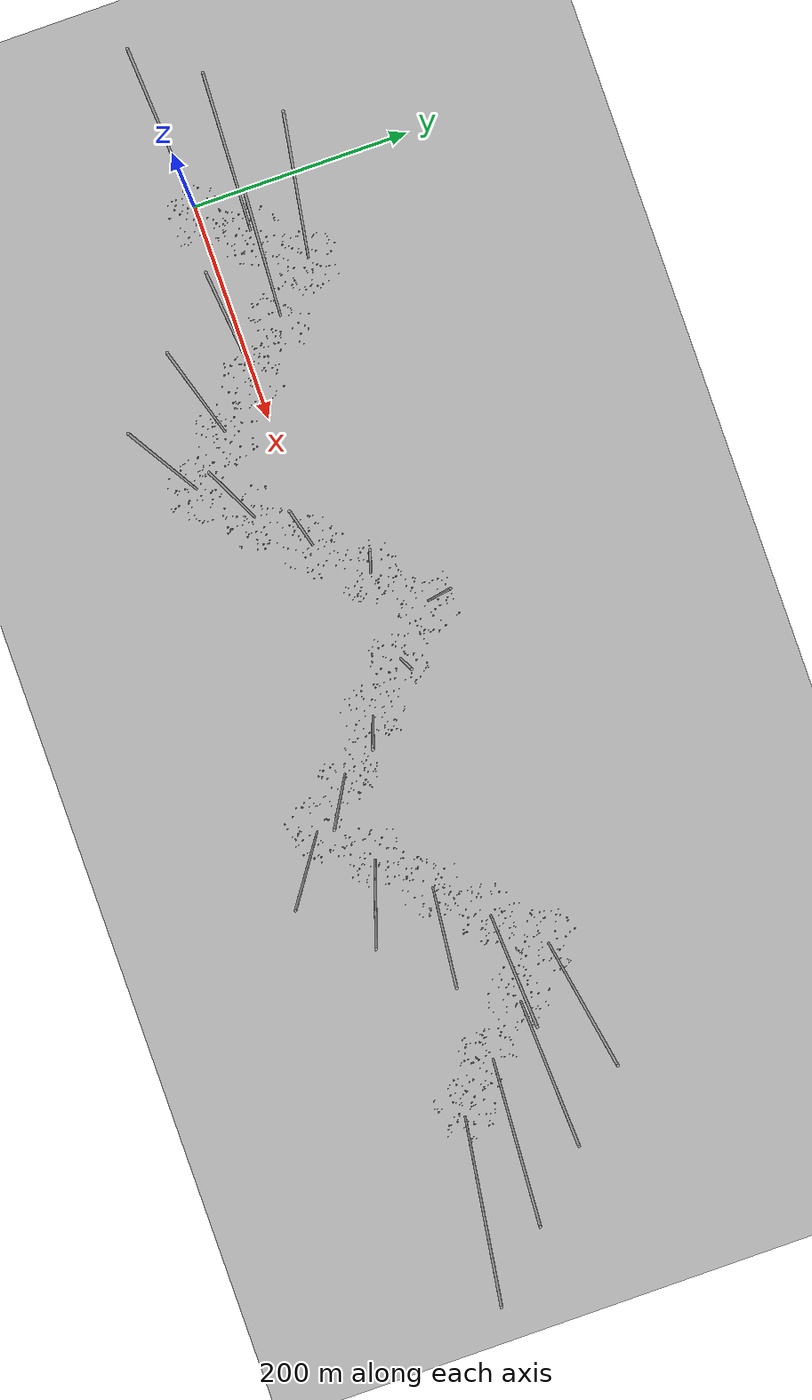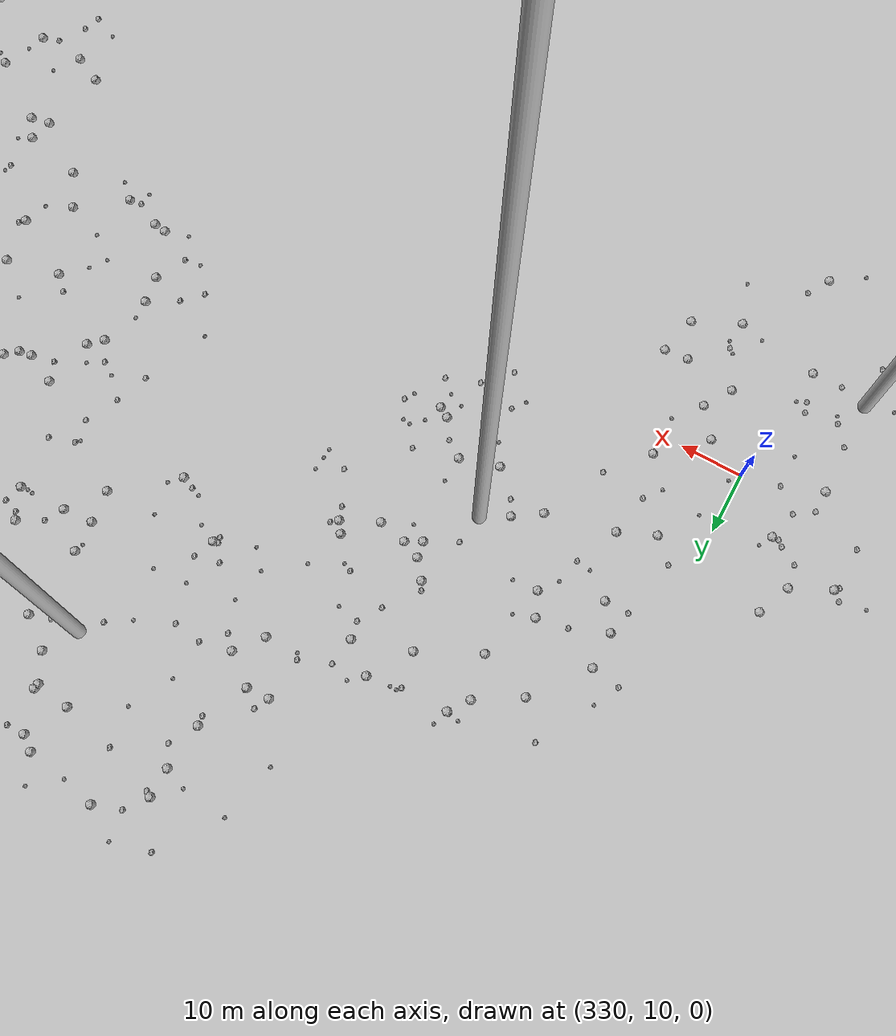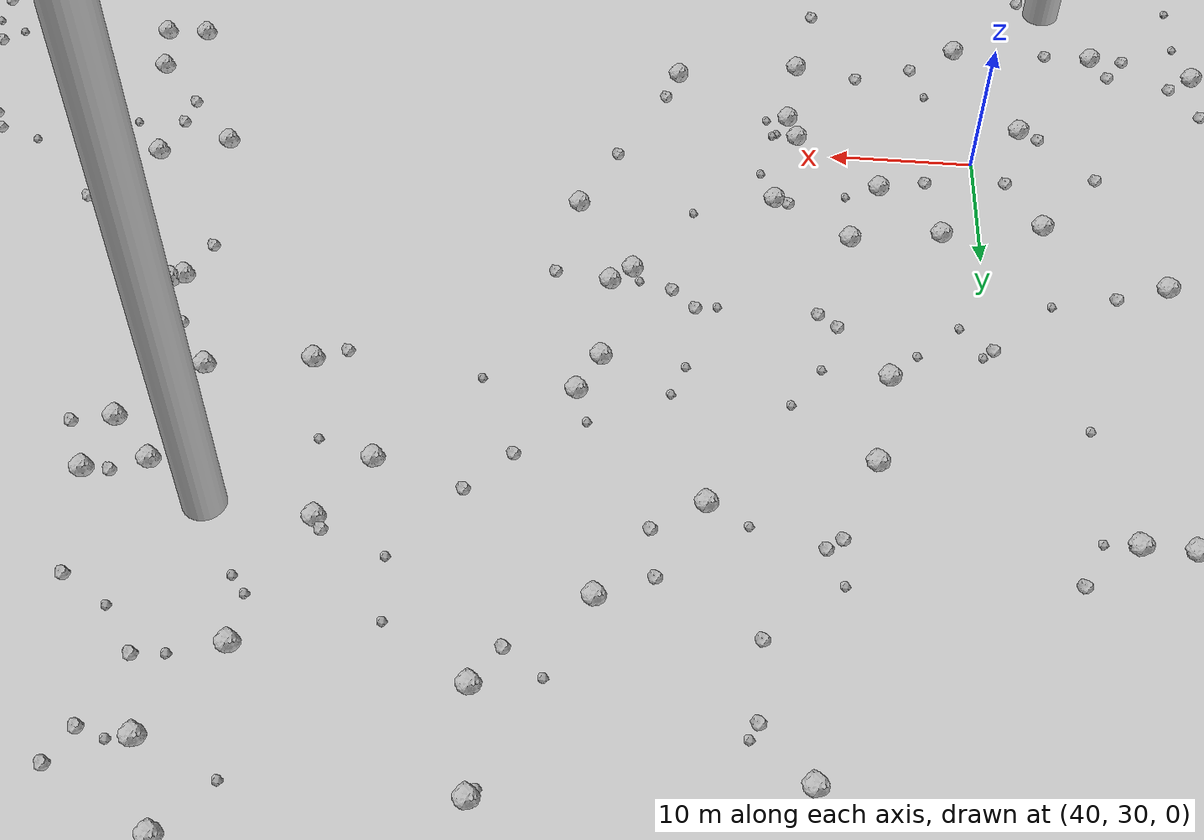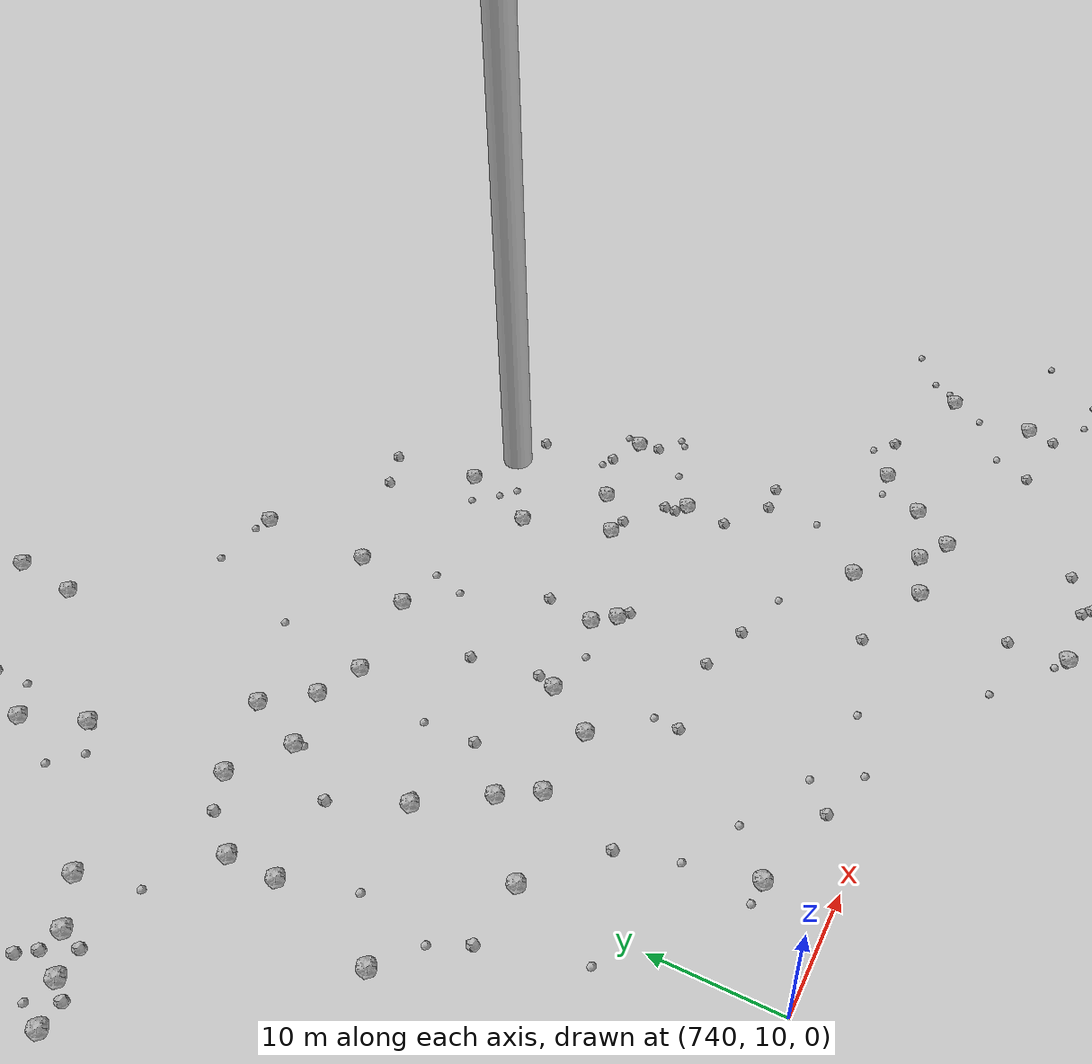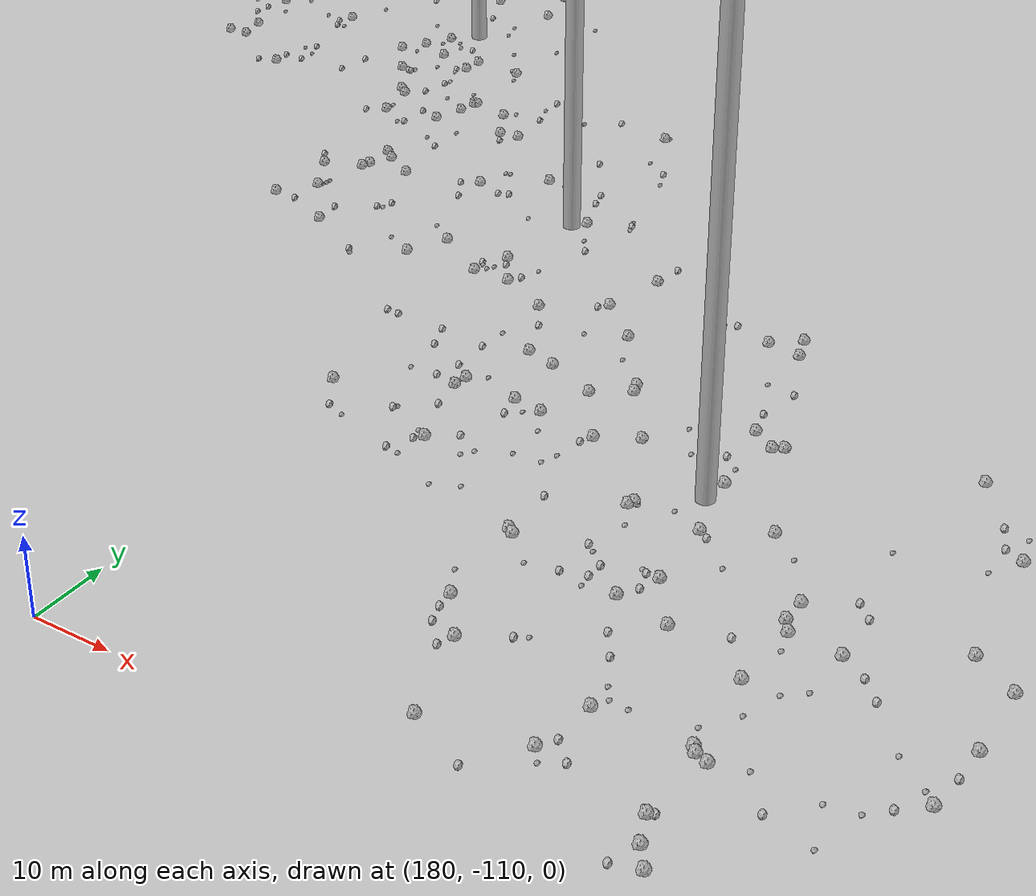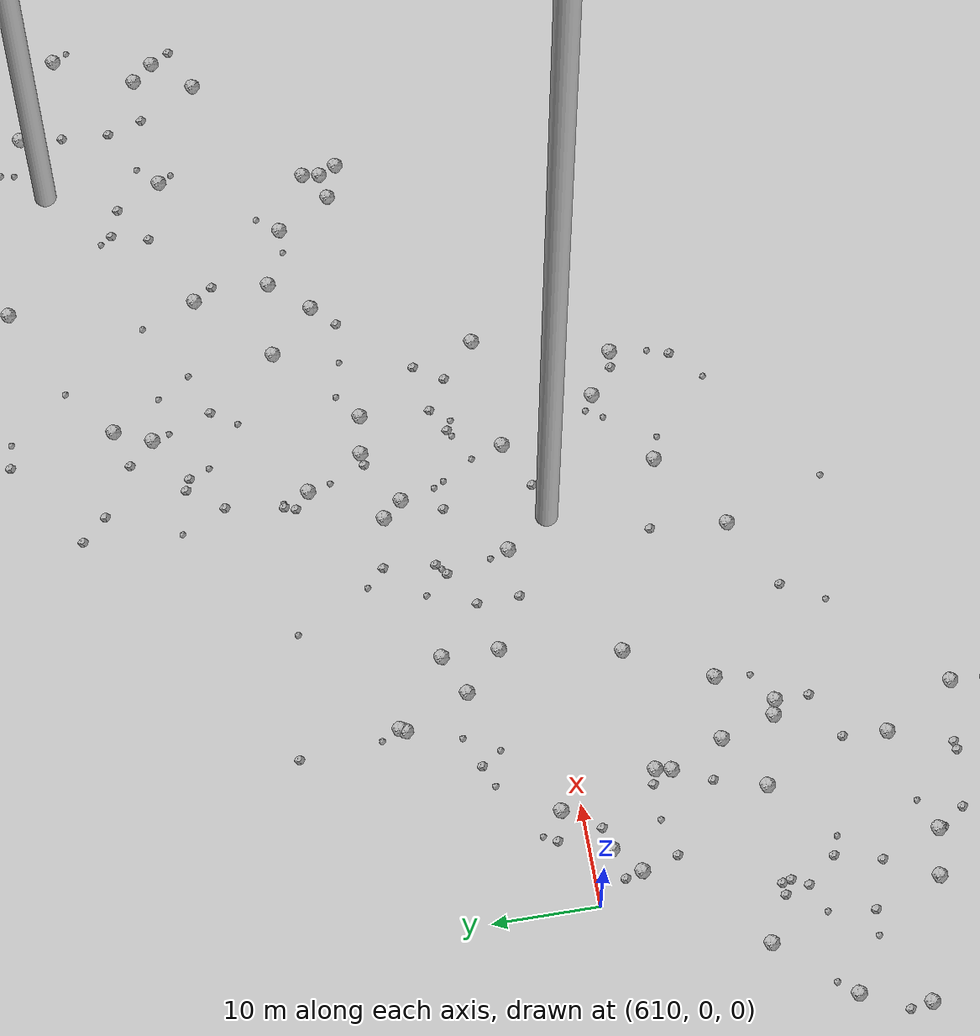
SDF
<sdf version="1.6">
 <world name="default">
  <include><uri>model://custom_ground</uri></include>
  <include><uri>model://sun</uri></include>
  <spherical_coordinates>
   <surface_model>EARTH_WGS84</surface_model>
   <latitude_deg>38.161479</latitude_deg>
   <longitude_deg>-122.454630</longitude_deg>
   <elevation>488.0</elevation>
   <heading_deg>90</heading_deg>
  </spherical_coordinates>
  <model name="rock1_0_0">
   <include><uri>model://rock1</uri><pose>10.821940397045196 -4.523592340949065 0.5 0 0 0</pose></include>
  </model>
  <model name="rock1_0_1">
   <include><uri>model://rock1</uri><pose>-3.2612408736402863 -17.877055829082632 0.5 0 0 0</pose></include>
  </model>
  <model name="rock1_0_2">
   <include><uri>model://rock1</uri><pose>20.236968406302218 13.408503228176016 0.5 0 0 0</pose></include>
  </model>
  <model name="rock1_0_3">
   <include><uri>model://rock1</uri><pose>13.055684413217122 1.251064031974046 0.5 0 0 0</pose></include>
  </model>
  <model name="rock1_0_4">
   <include><uri>model://rock1</uri><pose>-14.993761156548043 8.35029182055132 0.5 0 0 0</pose></include>
  </model>
  <model name="rock1_0_5">
   <include><uri>model://rock1</uri><pose>22.893345178660446 18.857827854576698 0.5 0 0 0</pose></include>
  </model>
  <model name="rock1_0_6">
   <include><uri>model://rock1</uri><pose>-16.49643778831015 -4.786456749395558 0.5 0 0 0</pose></include>
  </model>
  <model name="rock1_0_7">
   <include><uri>model://rock1</uri><pose>27.428805030857156 -1.8469164987717654 0.5 0 0 0</pose></include>
  </model>
  <model name="rock1_0_8">
   <include><uri>model://rock1</uri><pose>30.23622032656735 17.038255822152195 0.5 0 0 0</pose></include>
  </model>
  <model name="rock1_0_9">
   <include><uri>model://rock1</uri><pose>9.271307849004444 19.789888029220357 0.5 0 0 0</pose></include>
  </model>
  <model name="rock1_0_10">
   <include><uri>model://rock1</uri><pose>-13.399878486173494 -3.965482055158926 0.5 0 0 0</pose></include>
  </model>
  <model name="rock1_0_11">
   <include><uri>model://rock1</uri><pose>-2.0094451745667463 2.6641377313370356 0.5 0 0 0</pose></include>
  </model>
  <model name="rock1_0_12">
   <include><uri>model://rock1</uri><pose>14.844141967051776 25.91319315444226 0.5 0 0 0</pose></include>
  </model>
  <model name="rock1_0_13">
   <include><uri>model://rock1</uri><pose>16.30258723649783 11.911439262818696 0.5 0 0 0</pose></include>
  </model>
  <model name="rock1_0_14">
   <include><uri>model://rock1</uri><pose>-10.96123594212285 -13.592383131722528 0.5 0 0 0</pose></include>
  </model>
  <model name="rock1_0_15">
   <include><uri>model://rock1</uri><pose>2.5782642925681003 -24.47634214251631 0.5 0 0 0</pose></include>
  </model>
  <model name="rock1_0_16">
   <include><uri>model://rock1</uri><pose>13.62231153825946 24.772420155391117 0.5 0 0 0</pose></include>
  </model>
  <model name="rock1_0_17">
   <include><uri>model://rock1</uri><pose>-6.485202266334738 -15.522939422022354 0.5 0 0 0</pose></include>
  </model>
  <model name="rock1_0_18">
   <include><uri>model://rock1</uri><pose>33.22430456099622 10.549350398413331 0.5 0 0 0</pose></include>
  </model>
  <model name="rock1_0_19">
   <include><uri>model://rock1</uri><pose>1.926757771120748 -14.44521124996305 0.5 0 0 0</pose></include>
  </model>
  <model name="rock1_0_20">
   <include><uri>model://rock1</uri><pose>24.23321447496639 -13.671661066058753 0.5 0 0 0</pose></include>
  </model>
  <model name="rock1_0_21">
   <include><uri>model://rock1</uri><pose>-0.6063811236792667 -6.210338863403674 0.5 0 0 0</pose></include>
  </model>
  <model name="rock1_0_22">
   <include><uri>model://rock1</uri><pose>-3.057630912245429 20.08588613857522 0.5 0 0 0</pose></include>
  </model>
  <model name="rock1_0_23">
   <include><uri>model://rock1</uri><pose>10.778273023344632 20.104986298174893 0.5 0 0 0</pose></include>
  </model>
  <model name="rock1_0_24">
   <include><uri>model://rock1</uri><pose>12.91419316591329 7.546934526845838 0.5 0 0 0</pose></include>
  </model>
  <model name="rock1_0_25">
   <include><uri>model://rock1</uri><pose>36.48425089388974 2.9341699619062283 0.5 0 0 0</pose></include>
  </model>
  <model name="rock1_0_26">
   <include><uri>model://rock1</uri><pose>-1.070327424108413 8.771474004652525 0.5 0 0 0</pose></include>
  </model>
  <model name="rock2_0_0">
   <include><uri>model://rock2</uri><pose>-11.100777580453267 18.68692077397595 0.3 0 0 0</pose></include>
  </model>
  <model name="rock2_0_1">
   <include><uri>model://rock2</uri><pose>24.284246529631993 -15.50590167762884 0.3 0 0 0</pose></include>
  </model>
  <model name="rock2_0_2">
   <include><uri>model://rock2</uri><pose>-0.1229574149473791 -11.676853589150621 0.3 0 0 0</pose></include>
  </model>
  <model name="rock2_0_3">
   <include><uri>model://rock2</uri><pose>19.70893785184542 -22.58963252696951 0.3 0 0 0</pose></include>
  </model>
  <model name="rock2_0_4">
   <include><uri>model://rock2</uri><pose>28.40204740845686 -18.947165313035512 0.3 0 0 0</pose></include>
  </model>
  <model name="rock2_0_5">
   <include><uri>model://rock2</uri><pose>-0.42238981190447333 4.475533588720168 0.3 0 0 0</pose></include>
  </model>
  <model name="rock2_0_6">
   <include><uri>model://rock2</uri><pose>14.524118540050296 -3.6676030570950644 0.3 0 0 0</pose></include>
  </model>
  <model name="rock2_0_7">
   <include><uri>model://rock2</uri><pose>24.694777346149237 20.227979092687782 0.3 0 0 0</pose></include>
  </model>
  <model name="rock2_0_8">
   <include><uri>model://rock2</uri><pose>14.02107016862658 -17.991570410969047 0.3 0 0 0</pose></include>
  </model>
  <model name="rock2_0_9">
   <include><uri>model://rock2</uri><pose>35.12982947613083 10.073821226563695 0.3 0 0 0</pose></include>
  </model>
  <model name="rock2_0_10">
   <include><uri>model://rock2</uri><pose>-11.11831359696945 -17.454144920927696 0.3 0 0 0</pose></include>
  </model>
  <model name="rock2_0_11">
   <include><uri>model://rock2</uri><pose>-4.83486660691225 -9.103818379895387 0.3 0 0 0</pose></include>
  </model>
  <model name="rock2_0_12">
   <include><uri>model://rock2</uri><pose>1.456762340356498 21.164740214981585 0.3 0 0 0</pose></include>
  </model>
  <model name="rock2_0_13">
   <include><uri>model://rock2</uri><pose>22.890488084798378 23.395814532811507 0.3 0 0 0</pose></include>
  </model>
  <model name="rock2_0_14">
   <include><uri>model://rock2</uri><pose>20.93408075718132 -6.95670406874633 0.3 0 0 0</pose></include>
  </model>
  <model name="rock2_0_15">
   <include><uri>model://rock2</uri><pose>-17.99418645703656 5.338835887511522 0.3 0 0 0</pose></include>
  </model>
  <model name="rock2_0_16">
   <include><uri>model://rock2</uri><pose>28.94393933002837 -13.570474452881985 0.3 0 0 0</pose></include>
  </model>
  <model name="rock2_0_17">
   <include><uri>model://rock2</uri><pose>20.508117045433238 23.598601458643635 0.3 0 0 0</pose></include>
  </model>
  <model name="rock2_0_18">
   <include><uri>model://rock2</uri><pose>-9.99749460904918 0.003385052644336639 0.3 0 0 0</pose></include>
  </model>
  <model name="rock2_0_19">
   <include><uri>model://rock2</uri><pose>-2.221349582493527 5.4332307687127255 0.3 0 0 0</pose></include>
  </model>
  <model name="rock2_0_20">
   <include><uri>model://rock2</uri><pose>25.516365423611937 -3.961672037085439 0.3 0 0 0</pose></include>
  </model>
  <model name="rock2_0_21">
   <include><uri>model://rock2</uri><pose>30.066282157324835 -16.27242106847402 0.3 0 0 0</pose></include>
  </model>
  <model name="rock2_0_22">
   <include><uri>model://rock2</uri><pose>0.6948006825252477 -20.728045821858828 0.3 0 0 0</pose></include>
  </model>
  <model name="rock2_0_23">
   <include><uri>model://rock2</uri><pose>18.288720072384294 20.662845561977413 0.3 0 0 0</pose></include>
  </model>
  <model name="rock2_0_24">
   <include><uri>model://rock2</uri><pose>-3.512811776391864 13.07273586167085 0.3 0 0 0</pose></include>
  </model>
  <model name="rock2_0_25">
   <include><uri>model://rock2</uri><pose>-10.30639033041444 -8.468821826699852 0.3 0 0 0</pose></include>
  </model>
  <model name="rock2_0_26">
   <include><uri>model://rock2</uri><pose>35.098928516886154 1.1962896216791954 0.3 0 0 0</pose></include>
  </model>
  <model name="rock3_0_0">
   <include><uri>model://rock3</uri><pose>14.063888080929665 -27.713126321143257 0.2 0 0 0</pose></include>
  </model>
  <model name="rock3_0_1">
   <include><uri>model://rock3</uri><pose>-3.4006684733511214 -17.73215396875679 0.2 0 0 0</pose></include>
  </model>
  <model name="rock3_0_2">
   <include><uri>model://rock3</uri><pose>16.170575595316578 -4.038658240653334 0.2 0 0 0</pose></include>
  </model>
  <model name="rock3_0_3">
   <include><uri>model://rock3</uri><pose>-7.171433113908153 1.0318849061043736 0.2 0 0 0</pose></include>
  </model>
  <model name="rock3_0_4">
   <include><uri>model://rock3</uri><pose>30.899966138777103 -18.169410742821878 0.2 0 0 0</pose></include>
  </model>
  <model name="rock3_0_5">
   <include><uri>model://rock3</uri><pose>-6.045631681822741 13.400515126239199 0.2 0 0 0</pose></include>
  </model>
  <model name="rock3_0_6">
   <include><uri>model://rock3</uri><pose>23.27176516290787 -2.248546880817244 0.2 0 0 0</pose></include>
  </model>
  <model name="rock3_0_7">
   <include><uri>model://rock3</uri><pose>11.96648294721897 -6.367393209135756 0.2 0 0 0</pose></include>
  </model>
  <model name="rock3_0_8">
   <include><uri>model://rock3</uri><pose>37.81080736499298 -9.366841322463483 0.2 0 0 0</pose></include>
  </model>
  <model name="rock3_0_9">
   <include><uri>model://rock3</uri><pose>18.002572839908836 -15.740524363678363 0.2 0 0 0</pose></include>
  </model>
  <model name="rock3_0_10">
   <include><uri>model://rock3</uri><pose>29.111020803020907 -22.779593765171153 0.2 0 0 0</pose></include>
  </model>
  <model name="rock3_0_11">
   <include><uri>model://rock3</uri><pose>38.83126261639326 -7.472951352033554 0.2 0 0 0</pose></include>
  </model>
  <model name="rock3_0_12">
   <include><uri>model://rock3</uri><pose>4.503177655978213 -25.531952057285427 0.2 0 0 0</pose></include>
  </model>
  <model name="rock3_0_13">
   <include><uri>model://rock3</uri><pose>25.936396218572625 -1.8948478448517179 0.2 0 0 0</pose></include>
  </model>
  <model name="rock3_0_14">
   <include><uri>model://rock3</uri><pose>20.342613327653417 21.494935399372395 0.2 0 0 0</pose></include>
  </model>
  <model name="rock3_0_15">
   <include><uri>model://rock3</uri><pose>2.7573292174835515 -7.7090291018535915 0.2 0 0 0</pose></include>
  </model>
  <model name="rock3_0_16">
   <include><uri>model://rock3</uri><pose>-9.086542822261997 17.761296501034366 0.2 0 0 0</pose></include>
  </model>
  <model name="rock3_0_17">
   <include><uri>model://rock3</uri><pose>-13.05532493038653 0.23824882722945517 0.2 0 0 0</pose></include>
  </model>
  <model name="rock3_0_18">
   <include><uri>model://rock3</uri><pose>-8.617405152145414 -22.325313582616907 0.2 0 0 0</pose></include>
  </model>
  <model name="rock3_0_19">
   <include><uri>model://rock3</uri><pose>-5.637858588102265 -2.73498003469307 0.2 0 0 0</pose></include>
  </model>
  <model name="rock3_0_20">
   <include><uri>model://rock3</uri><pose>25.105938946666463 3.7984459803435655 0.2 0 0 0</pose></include>
  </model>
  <model name="rock3_0_21">
   <include><uri>model://rock3</uri><pose>23.54662615840961 10.300649268528787 0.2 0 0 0</pose></include>
  </model>
  <model name="rock3_0_22">
   <include><uri>model://rock3</uri><pose>2.769816438079438 -23.429425334635138 0.2 0 0 0</pose></include>
  </model>
  <model name="rock3_0_23">
   <include><uri>model://rock3</uri><pose>32.608366940651344 8.950698020907176 0.2 0 0 0</pose></include>
  </model>
  <model name="rock3_0_24">
   <include><uri>model://rock3</uri><pose>-17.540251813267428 -2.7836306548068634 0.2 0 0 0</pose></include>
  </model>
  <model name="rock3_0_25">
   <include><uri>model://rock3</uri><pose>8.027507382865519 -10.43856984200879 0.2 0 0 0</pose></include>
  </model>
  <model name="rock3_0_26">
   <include><uri>model://rock3</uri><pose>-3.2833565946858236 25.01332883147053 0.2 0 0 0</pose></include>
  </model>
  <model name="rock1_1_0">
   <include><uri>model://rock1</uri><pose>19.40070370909301 34.80965772699821 0.5 0 0 0</pose></include>
  </model>
  <model name="rock1_1_1">
   <include><uri>model://rock1</uri><pose>64.86095860510808 44.38572144761408 0.5 0 0 0</pose></include>
  </model>
  <model name="rock1_1_2">
   <include><uri>model://rock1</uri><pose>27.956462468573957 42.00203384418031 0.5 0 0 0</pose></include>
  </model>
  <model name="rock1_1_3">
   <include><uri>model://rock1</uri><pose>48.85393605434432 38.862842753800464 0.5 0 0 0</pose></include>
  </model>
  <model name="rock1_1_4">
   <include><uri>model://rock1</uri><pose>35.66008184255945 36.58583925416555 0.5 0 0 0</pose></include>
  </model>
  <model name="rock1_1_5">
   <include><uri>model://rock1</uri><pose>29.416634580670916 63.66132007914443 0.5 0 0 0</pose></include>
  </model>
  <model name="rock1_1_6">
   <include><uri>model://rock1</uri><pose>61.482871889992005 21.673352281790088 0.5 0 0 0</pose></include>
  </model>
  <model name="rock1_1_7">
   <include><uri>model://rock1</uri><pose>47.53334025777267 58.59392694128085 0.5 0 0 0</pose></include>
  </model>
  <model name="rock1_1_8">
   <include><uri>model://rock1</uri><pose>20.879432663680497 40.50993548535821 0.5 0 0 0</pose></include>
  </model>
  <model name="rock1_1_9">
   <include><uri>model://rock1</uri><pose>52.54841499662429 28.369861971943312 0.5 0 0 0</pose></include>
  </model>
  <model name="rock1_1_10">
   <include><uri>model://rock1</uri><pose>63.44869653755539 43.11811928560431 0.5 0 0 0</pose></include>
  </model>
  <model name="rock1_1_11">
   <include><uri>model://rock1</uri><pose>40.60226387555821 17.003812285685527 0.5 0 0 0</pose></include>
  </model>
  <model name="rock1_1_12">
   <include><uri>model://rock1</uri><pose>13.44771769232902 44.57807754562875 0.5 0 0 0</pose></include>
  </model>
  <model name="rock1_1_13">
   <include><uri>model://rock1</uri><pose>54.06848697853949 35.277904430381 0.5 0 0 0</pose></include>
  </model>
  <model name="rock1_1_14">
   <include><uri>model://rock1</uri><pose>67.61234715271681 36.89054082099831 0.5 0 0 0</pose></include>
  </model>
  <model name="rock1_1_15">
   <include><uri>model://rock1</uri><pose>18.887568969598277 55.69738325313591 0.5 0 0 0</pose></include>
  </model>
  <model name="rock1_1_16">
   <include><uri>model://rock1</uri><pose>21.02410698425878 29.01008936160747 0.5 0 0 0</pose></include>
  </model>
  <model name="rock1_1_17">
   <include><uri>model://rock1</uri><pose>46.75839226418864 33.419020782422805 0.5 0 0 0</pose></include>
  </model>
  <model name="rock1_1_18">
   <include><uri>model://rock1</uri><pose>16.749917581252497 44.13201769871008 0.5 0 0 0</pose></include>
  </model>
  <model name="rock1_1_19">
   <include><uri>model://rock1</uri><pose>32.648729018175125 63.55883235399129 0.5 0 0 0</pose></include>
  </model>
  <model name="rock1_1_20">
   <include><uri>model://rock1</uri><pose>36.41468767067873 26.24343775749557 0.5 0 0 0</pose></include>
  </model>
  <model name="rock1_1_21">
   <include><uri>model://rock1</uri><pose>42.62643744922854 37.89454471153733 0.5 0 0 0</pose></include>
  </model>
  <model name="rock1_1_22">
   <include><uri>model://rock1</uri><pose>53.22118603848459 26.230072837925796 0.5 0 0 0</pose></include>
  </model>
  <model name="rock1_1_23">
   <include><uri>model://rock1</uri><pose>46.56669232226678 51.54857382532041 0.5 0 0 0</pose></include>
  </model>
  <model name="rock1_1_24">
   <include><uri>model://rock1</uri><pose>64.88930811709639 51.29613455374484 0.5 0 0 0</pose></include>
  </model>
  <model name="rock1_1_25">
   <include><uri>model://rock1</uri><pose>52.62208578378793 20.05632801362754 0.5 0 0 0</pose></include>
  </model>
  <model name="rock1_1_26">
   <include><uri>model://rock1</uri><pose>66.18482817121247 54.32654240660695 0.5 0 0 0</pose></include>
  </model>
  <model name="rock2_1_0">
   <include><uri>model://rock2</uri><pose>29.130325156344202 19.18038925457261 0.3 0 0 0</pose></include>
  </model>
  <model name="rock2_1_1">
   <include><uri>model://rock2</uri><pose>23.759013580484513 37.02127373552848 0.3 0 0 0</pose></include>
  </model>
  <model name="rock2_1_2">
   <include><uri>model://rock2</uri><pose>50.665140627209766 65.29473692248226 0.3 0 0 0</pose></include>
  </model>
  <model name="rock2_1_3">
   <include><uri>model://rock2</uri><pose>36.124021657659284 66.6414076913224 0.3 0 0 0</pose></include>
  </model>
  <model name="rock2_1_4">
   <include><uri>model://rock2</uri><pose>27.790419204107266 17.089568576901684 0.3 0 0 0</pose></include>
  </model>
  <model name="rock2_1_5">
   <include><uri>model://rock2</uri><pose>62.25763630785885 24.381512887129887 0.3 0 0 0</pose></include>
  </model>
  <model name="rock2_1_6">
   <include><uri>model://rock2</uri><pose>60.69607372382941 44.86410204370463 0.3 0 0 0</pose></include>
  </model>
  <model name="rock2_1_7">
   <include><uri>model://rock2</uri><pose>43.4798700793774 32.556085776063206 0.3 0 0 0</pose></include>
  </model>
  <model name="rock2_1_8">
   <include><uri>model://rock2</uri><pose>43.98069451209466 19.537055252984864 0.3 0 0 0</pose></include>
  </model>
  <model name="rock2_1_9">
   <include><uri>model://rock2</uri><pose>35.058990910883466 27.048241767291575 0.3 0 0 0</pose></include>
  </model>
  <model name="rock2_1_10">
   <include><uri>model://rock2</uri><pose>33.59279343122428 16.891676549920614 0.3 0 0 0</pose></include>
  </model>
  <model name="rock2_1_11">
   <include><uri>model://rock2</uri><pose>48.13371042303132 21.017306552993666 0.3 0 0 0</pose></include>
  </model>
  <model name="rock2_1_12">
   <include><uri>model://rock2</uri><pose>37.821725965320134 32.11642148634589 0.3 0 0 0</pose></include>
  </model>
  <model name="rock2_1_13">
   <include><uri>model://rock2</uri><pose>20.898775314475373 22.35332585544549 0.3 0 0 0</pose></include>
  </model>
  <model name="rock2_1_14">
   <include><uri>model://rock2</uri><pose>49.815835914836796 47.37608594542208 0.3 0 0 0</pose></include>
  </model>
  <model name="rock2_1_15">
   <include><uri>model://rock2</uri><pose>51.06127799018798 46.319212413414505 0.3 0 0 0</pose></include>
  </model>
  <model name="rock2_1_16">
   <include><uri>model://rock2</uri><pose>51.43779524490129 13.362513387972303 0.3 0 0 0</pose></include>
  </model>
  <model name="rock2_1_17">
   <include><uri>model://rock2</uri><pose>31.41170549326506 43.222872864275054 0.3 0 0 0</pose></include>
  </model>
  <model name="rock2_1_18">
   <include><uri>model://rock2</uri><pose>53.107447953806926 35.559484189767886 0.3 0 0 0</pose></include>
  </model>
  <model name="rock2_1_19">
   <include><uri>model://rock2</uri><pose>59.09300559791124 46.426980133832956 0.3 0 0 0</pose></include>
  </model>
  <model name="rock2_1_20">
   <include><uri>model://rock2</uri><pose>65.33728557131293 31.296080510085456 0.3 0 0 0</pose></include>
  </model>
  <model name="rock2_1_21">
   <include><uri>model://rock2</uri><pose>14.988833303947848 45.91971675778195 0.3 0 0 0</pose></include>
  </model>
  <model name="rock2_1_22">
   <include><uri>model://rock2</uri><pose>68.55185230455538 43.7904804889975 0.3 0 0 0</pose></include>
  </model>
  <model name="rock2_1_23">
   <include><uri>model://rock2</uri><pose>49.695084270487854 64.5120380633507 0.3 0 0 0</pose></include>
  </model>
  <model name="rock2_1_24">
   <include><uri>model://rock2</uri><pose>31.44197343720951 31.245560365901273 0.3 0 0 0</pose></include>
  </model>
  <model name="rock2_1_25">
   <include><uri>model://rock2</uri><pose>39.873224358203785 48.59985042775322 0.3 0 0 0</pose></include>
  </model>
  <model name="rock2_1_26">
   <include><uri>model://rock2</uri><pose>19.67643269170959 56.51027397387863 0.3 0 0 0</pose></include>
  </model>
  <model name="rock3_1_0">
   <include><uri>model://rock3</uri><pose>53.95846117391416 27.90423873968814 0.2 0 0 0</pose></include>
  </model>
  <model name="rock3_1_1">
   <include><uri>model://rock3</uri><pose>49.06416602840991 34.45516355693954 0.2 0 0 0</pose></include>
  </model>
  <model name="rock3_1_2">
   <include><uri>model://rock3</uri><pose>23.336560624437112 46.585896682695115 0.2 0 0 0</pose></include>
  </model>
  <model name="rock3_1_3">
   <include><uri>model://rock3</uri><pose>62.87095835191743 44.138991919715785 0.2 0 0 0</pose></include>
  </model>
  <model name="rock3_1_4">
   <include><uri>model://rock3</uri><pose>43.00322673620374 22.600166925790003 0.2 0 0 0</pose></include>
  </model>
  <model name="rock3_1_5">
   <include><uri>model://rock3</uri><pose>59.6122321877194 37.06549050123829 0.2 0 0 0</pose></include>
  </model>
  <model name="rock3_1_6">
   <include><uri>model://rock3</uri><pose>59.42565740631777 51.65889281307086 0.2 0 0 0</pose></include>
  </model>
  <model name="rock3_1_7">
   <include><uri>model://rock3</uri><pose>34.675827314809155 63.47341253414507 0.2 0 0 0</pose></include>
  </model>
  <model name="rock3_1_8">
   <include><uri>model://rock3</uri><pose>55.01730273146029 32.450292354963494 0.2 0 0 0</pose></include>
  </model>
  <model name="rock3_1_9">
   <include><uri>model://rock3</uri><pose>60.22515615344366 54.06097819497206 0.2 0 0 0</pose></include>
  </model>
  <model name="rock3_1_10">
   <include><uri>model://rock3</uri><pose>34.397046265394046 54.86809505168672 0.2 0 0 0</pose></include>
  </model>
  <model name="rock3_1_11">
   <include><uri>model://rock3</uri><pose>55.102817242565656 63.98447746439274 0.2 0 0 0</pose></include>
  </model>
  <model name="rock3_1_12">
   <include><uri>model://rock3</uri><pose>44.70443304174233 49.4326846214496 0.2 0 0 0</pose></include>
  </model>
  <model name="rock3_1_13">
   <include><uri>model://rock3</uri><pose>54.71595980554581 26.41563626640706 0.2 0 0 0</pose></include>
  </model>
  <model name="rock3_1_14">
   <include><uri>model://rock3</uri><pose>41.87708785923992 46.69705354076366 0.2 0 0 0</pose></include>
  </model>
  <model name="rock3_1_15">
   <include><uri>model://rock3</uri><pose>54.27413266926419 28.155164190926147 0.2 0 0 0</pose></include>
  </model>
  <model name="rock3_1_16">
   <include><uri>model://rock3</uri><pose>15.423361250072038 30.162025045718785 0.2 0 0 0</pose></include>
  </model>
  <model name="rock3_1_17">
   <include><uri>model://rock3</uri><pose>57.62250548876787 46.119326113040174 0.2 0 0 0</pose></include>
  </model>
  <model name="rock3_1_18">
   <include><uri>model://rock3</uri><pose>40.52604635110198 49.19993561766932 0.2 0 0 0</pose></include>
  </model>
  <model name="rock3_1_19">
   <include><uri>model://rock3</uri><pose>50.81280975760811 51.17246547438025 0.2 0 0 0</pose></include>
  </model>
  <model name="rock3_1_20">
   <include><uri>model://rock3</uri><pose>21.280566761843247 53.5860391582625 0.2 0 0 0</pose></include>
  </model>
  <model name="rock3_1_21">
   <include><uri>model://rock3</uri><pose>49.58507441808181 67.73650162823574 0.2 0 0 0</pose></include>
  </model>
  <model name="rock3_1_22">
   <include><uri>model://rock3</uri><pose>52.71608303106914 54.30732763564854 0.2 0 0 0</pose></include>
  </model>
  <model name="rock3_1_23">
   <include><uri>model://rock3</uri><pose>23.631605776601013 15.028849967696118 0.2 0 0 0</pose></include>
  </model>
  <model name="rock3_1_24">
   <include><uri>model://rock3</uri><pose>35.70123436179591 44.16776413062264 0.2 0 0 0</pose></include>
  </model>
  <model name="rock3_1_25">
   <include><uri>model://rock3</uri><pose>22.952843048586267 27.995895170417782 0.2 0 0 0</pose></include>
  </model>
  <model name="rock3_1_26">
   <include><uri>model://rock3</uri><pose>26.73392659153202 55.950211476442895 0.2 0 0 0</pose></include>
  </model>
  <model name="rock1_2_0">
   <include><uri>model://rock1</uri><pose>72.46540615465354 88.97676836659225 0.5 0 0 0</pose></include>
  </model>
  <model name="rock1_2_1">
   <include><uri>model://rock1</uri><pose>77.34141533507845 101.59424829474736 0.5 0 0 0</pose></include>
  </model>
  <model name="rock1_2_2">
   <include><uri>model://rock1</uri><pose>83.51572082978734 74.6359127368272 0.5 0 0 0</pose></include>
  </model>
  <model name="rock1_2_3">
   <include><uri>model://rock1</uri><pose>71.0584549086334 107.17859481138868 0.5 0 0 0</pose></include>
  </model>
  <model name="rock1_2_4">
   <include><uri>model://rock1</uri><pose>80.54298000587835 65.65251676230407 0.5 0 0 0</pose></include>
  </model>
  <model name="rock1_2_5">
   <include><uri>model://rock1</uri><pose>102.67781443786609 85.23632631963679 0.5 0 0 0</pose></include>
  </model>
  <model name="rock1_2_6">
   <include><uri>model://rock1</uri><pose>102.46331427724978 69.49312511059149 0.5 0 0 0</pose></include>
  </model>
  <model name="rock1_2_7">
   <include><uri>model://rock1</uri><pose>91.3768081599462 62.19742563105477 0.5 0 0 0</pose></include>
  </model>
  <model name="rock1_2_8">
   <include><uri>model://rock1</uri><pose>59.452512715366815 90.99658246924058 0.5 0 0 0</pose></include>
  </model>
  <model name="rock1_2_9">
   <include><uri>model://rock1</uri><pose>69.14069670775625 82.75705782567266 0.5 0 0 0</pose></include>
  </model>
  <model name="rock1_2_10">
   <include><uri>model://rock1</uri><pose>57.69213331233178 62.59715711243069 0.5 0 0 0</pose></include>
  </model>
  <model name="rock1_2_11">
   <include><uri>model://rock1</uri><pose>63.72717184402895 69.77242956470333 0.5 0 0 0</pose></include>
  </model>
  <model name="rock1_2_12">
   <include><uri>model://rock1</uri><pose>89.9457127529445 54.29195640853293 0.5 0 0 0</pose></include>
  </model>
  <model name="rock1_2_13">
   <include><uri>model://rock1</uri><pose>69.95690897662772 76.07709537939127 0.5 0 0 0</pose></include>
  </model>
  <model name="rock1_2_14">
   <include><uri>model://rock1</uri><pose>100.8266255202281 74.64415911947619 0.5 0 0 0</pose></include>
  </model>
  <model name="rock1_2_15">
   <include><uri>model://rock1</uri><pose>87.1174957772578 80.7464686924906 0.5 0 0 0</pose></include>
  </model>
  <model name="rock1_2_16">
   <include><uri>model://rock1</uri><pose>95.2032845221314 63.23760611643962 0.5 0 0 0</pose></include>
  </model>
  <model name="rock1_2_17">
   <include><uri>model://rock1</uri><pose>78.90029086418859 98.02781387720073 0.5 0 0 0</pose></include>
  </model>
  <model name="rock1_2_18">
   <include><uri>model://rock1</uri><pose>77.88241295694914 60.93977585994043 0.5 0 0 0</pose></include>
  </model>
  <model name="rock1_2_19">
   <include><uri>model://rock1</uri><pose>102.52520043113014 80.24513610023867 0.5 0 0 0</pose></include>
  </model>
  <model name="rock1_2_20">
   <include><uri>model://rock1</uri><pose>94.36334754033447 59.0699217735398 0.5 0 0 0</pose></include>
  </model>
  <model name="rock1_2_21">
   <include><uri>model://rock1</uri><pose>89.07379016352786 96.0825925569407 0.5 0 0 0</pose></include>
  </model>
  <model name="rock1_2_22">
   <include><uri>model://rock1</uri><pose>83.13378923817382 53.156802909225206 0.5 0 0 0</pose></include>
  </model>
  <model name="rock1_2_23">
   <include><uri>model://rock1</uri><pose>84.74725742253864 86.18266541337557 0.5 0 0 0</pose></include>
  </model>
  <model name="rock1_2_24">
   <include><uri>model://rock1</uri><pose>51.35620556397925 80.50349398970047 0.5 0 0 0</pose></include>
  </model>
  <model name="rock1_2_25">
   <include><uri>model://rock1</uri><pose>86.7244818604388 88.7510008896983 0.5 0 0 0</pose></include>
  </model>
  <model name="rock1_2_26">
   <include><uri>model://rock1</uri><pose>51.367343810395596 85.33987670711264 0.5 0 0 0</pose></include>
  </model>
  <model name="rock2_2_0">
   <include><uri>model://rock2</uri><pose>69.53751423416135 100.88594518092418 0.3 0 0 0</pose></include>
  </model>
  <model name="rock2_2_1">
   <include><uri>model://rock2</uri><pose>69.47968011657103 59.78130921788063 0.3 0 0 0</pose></include>
  </model>
  <model name="rock2_2_2">
   <include><uri>model://rock2</uri><pose>72.14008043888029 62.74254405518141 0.3 0 0 0</pose></include>
  </model>
  <model name="rock2_2_3">
   <include><uri>model://rock2</uri><pose>79.99540988134912 66.41924341705005 0.3 0 0 0</pose></include>
  </model>
  <model name="rock2_2_4">
   <include><uri>model://rock2</uri><pose>60.96726795139183 102.26737008433622 0.3 0 0 0</pose></include>
  </model>
  <model name="rock2_2_5">
   <include><uri>model://rock2</uri><pose>96.99180064168083 59.56972898966365 0.3 0 0 0</pose></include>
  </model>
  <model name="rock2_2_6">
   <include><uri>model://rock2</uri><pose>88.7769471567331 92.86783158892453 0.3 0 0 0</pose></include>
  </model>
  <model name="rock2_2_7">
   <include><uri>model://rock2</uri><pose>60.87431008552746 64.74375544869297 0.3 0 0 0</pose></include>
  </model>
  <model name="rock2_2_8">
   <include><uri>model://rock2</uri><pose>54.21506844236083 71.79963123543925 0.3 0 0 0</pose></include>
  </model>
  <model name="rock2_2_9">
   <include><uri>model://rock2</uri><pose>70.31017867683158 86.18332768072098 0.3 0 0 0</pose></include>
  </model>
  <model name="rock2_2_10">
   <include><uri>model://rock2</uri><pose>99.56372877396964 75.7030462006628 0.3 0 0 0</pose></include>
  </model>
  <model name="rock2_2_11">
   <include><uri>model://rock2</uri><pose>98.5898167092475 101.18650619125361 0.3 0 0 0</pose></include>
  </model>
  <model name="rock2_2_12">
   <include><uri>model://rock2</uri><pose>93.51235964623893 63.16423996710849 0.3 0 0 0</pose></include>
  </model>
  <model name="rock2_2_13">
   <include><uri>model://rock2</uri><pose>68.42102306544382 73.52273150022054 0.3 0 0 0</pose></include>
  </model>
  <model name="rock2_2_14">
   <include><uri>model://rock2</uri><pose>107.20103215147213 75.00588052727015 0.3 0 0 0</pose></include>
  </model>
  <model name="rock2_2_15">
   <include><uri>model://rock2</uri><pose>88.67593942341801 75.734469671755 0.3 0 0 0</pose></include>
  </model>
  <model name="rock2_2_16">
   <include><uri>model://rock2</uri><pose>91.38640025456903 82.69497228633253 0.3 0 0 0</pose></include>
  </model>
  <model name="rock2_2_17">
   <include><uri>model://rock2</uri><pose>99.70927585855722 69.4629171340858 0.3 0 0 0</pose></include>
  </model>
  <model name="rock2_2_18">
   <include><uri>model://rock2</uri><pose>60.208773531927186 89.4901846590645 0.3 0 0 0</pose></include>
  </model>
  <model name="rock2_2_19">
   <include><uri>model://rock2</uri><pose>63.75700485160112 102.91281506611091 0.3 0 0 0</pose></include>
  </model>
  <model name="rock2_2_20">
   <include><uri>model://rock2</uri><pose>81.05887661519063 52.22122860111537 0.3 0 0 0</pose></include>
  </model>
  <model name="rock2_2_21">
   <include><uri>model://rock2</uri><pose>60.37109880564849 68.14478040541451 0.3 0 0 0</pose></include>
  </model>
  <model name="rock2_2_22">
   <include><uri>model://rock2</uri><pose>58.203613336399776 91.9586221178238 0.3 0 0 0</pose></include>
  </model>
  <model name="rock2_2_23">
   <include><uri>model://rock2</uri><pose>94.00595347838832 70.82140676075805 0.3 0 0 0</pose></include>
  </model>
  <model name="rock2_2_24">
   <include><uri>model://rock2</uri><pose>57.43649326316094 94.90443454325597 0.3 0 0 0</pose></include>
  </model>
  <model name="rock2_2_25">
   <include><uri>model://rock2</uri><pose>54.3352945529699 77.02369831530807 0.3 0 0 0</pose></include>
  </model>
  <model name="rock2_2_26">
   <include><uri>model://rock2</uri><pose>90.28491552973651 80.41678243241465 0.3 0 0 0</pose></include>
  </model>
  <model name="rock3_2_0">
   <include><uri>model://rock3</uri><pose>75.88884626466347 67.96465586551211 0.2 0 0 0</pose></include>
  </model>
  <model name="rock3_2_1">
   <include><uri>model://rock3</uri><pose>68.70980752675169 82.08790901750304 0.2 0 0 0</pose></include>
  </model>
  <model name="rock3_2_2">
   <include><uri>model://rock3</uri><pose>90.90701170792548 72.66442547787202 0.2 0 0 0</pose></include>
  </model>
  <model name="rock3_2_3">
   <include><uri>model://rock3</uri><pose>67.2186161201612 103.01641468708259 0.2 0 0 0</pose></include>
  </model>
  <model name="rock3_2_4">
   <include><uri>model://rock3</uri><pose>82.06916401921345 82.7715778864272 0.2 0 0 0</pose></include>
  </model>
  <model name="rock3_2_5">
   <include><uri>model://rock3</uri><pose>89.66144536636588 101.18177340682922 0.2 0 0 0</pose></include>
  </model>
  <model name="rock3_2_6">
   <include><uri>model://rock3</uri><pose>94.29932974265606 84.08398612434218 0.2 0 0 0</pose></include>
  </model>
  <model name="rock3_2_7">
   <include><uri>model://rock3</uri><pose>75.26919318458062 107.48866527031547 0.2 0 0 0</pose></include>
  </model>
  <model name="rock3_2_8">
   <include><uri>model://rock3</uri><pose>75.30183802199696 72.3849488710078 0.2 0 0 0</pose></include>
  </model>
  <model name="rock3_2_9">
   <include><uri>model://rock3</uri><pose>84.3461360636135 70.03529242237394 0.2 0 0 0</pose></include>
  </model>
  <model name="rock3_2_10">
   <include><uri>model://rock3</uri><pose>65.26546152932639 56.807270416750555 0.2 0 0 0</pose></include>
  </model>
  <model name="rock3_2_11">
   <include><uri>model://rock3</uri><pose>105.172216570302 82.14935432254023 0.2 0 0 0</pose></include>
  </model>
  <model name="rock3_2_12">
   <include><uri>model://rock3</uri><pose>88.52728155792741 80.92265796804702 0.2 0 0 0</pose></include>
  </model>
  <model name="rock3_2_13">
   <include><uri>model://rock3</uri><pose>100.62886347470773 63.80791313285001 0.2 0 0 0</pose></include>
  </model>
  <model name="rock3_2_14">
   <include><uri>model://rock3</uri><pose>81.4513928869402 59.57646656449489 0.2 0 0 0</pose></include>
  </model>
  <model name="rock3_2_15">
   <include><uri>model://rock3</uri><pose>74.71068298437312 99.75060067090165 0.2 0 0 0</pose></include>
  </model>
  <model name="rock3_2_16">
   <include><uri>model://rock3</uri><pose>54.76699051035605 78.00061999963877 0.2 0 0 0</pose></include>
  </model>
  <model name="rock3_2_17">
   <include><uri>model://rock3</uri><pose>101.66947577619813 91.43890813581385 0.2 0 0 0</pose></include>
  </model>
  <model name="rock3_2_18">
   <include><uri>model://rock3</uri><pose>88.5549400352661 61.95367262631559 0.2 0 0 0</pose></include>
  </model>
  <model name="rock3_2_19">
   <include><uri>model://rock3</uri><pose>86.7193768771507 75.489356016147 0.2 0 0 0</pose></include>
  </model>
  <model name="rock3_2_20">
   <include><uri>model://rock3</uri><pose>96.04985254573825 77.15173548043055 0.2 0 0 0</pose></include>
  </model>
  <model name="rock3_2_21">
   <include><uri>model://rock3</uri><pose>66.4912671537263 88.7699979075542 0.2 0 0 0</pose></include>
  </model>
  <model name="rock3_2_22">
   <include><uri>model://rock3</uri><pose>95.26520898523468 89.79822912547638 0.2 0 0 0</pose></include>
  </model>
  <model name="rock3_2_23">
   <include><uri>model://rock3</uri><pose>65.97977747036984 75.20993083513542 0.2 0 0 0</pose></include>
  </model>
  <model name="rock3_2_24">
   <include><uri>model://rock3</uri><pose>83.36509282733161 71.22093993416709 0.2 0 0 0</pose></include>
  </model>
  <model name="rock3_2_25">
   <include><uri>model://rock3</uri><pose>77.30400913320811 97.3424772287762 0.2 0 0 0</pose></include>
  </model>
  <model name="rock3_2_26">
   <include><uri>model://rock3</uri><pose>72.15675839937524 53.70495725564764 0.2 0 0 0</pose></include>
  </model>
  <model name="rock1_3_0">
   <include><uri>model://rock1</uri><pose>98.47256207721622 19.597268889068552 0.5 0 0 0</pose></include>
  </model>
  <model name="rock1_3_1">
   <include><uri>model://rock1</uri><pose>138.792852048462 27.414879942117665 0.5 0 0 0</pose></include>
  </model>
  <model name="rock1_3_2">
   <include><uri>model://rock1</uri><pose>138.93733769628983 30.468730152638607 0.5 0 0 0</pose></include>
  </model>
  <model name="rock1_3_3">
   <include><uri>model://rock1</uri><pose>135.86587308858265 59.95201519401472 0.5 0 0 0</pose></include>
  </model>
  <model name="rock1_3_4">
   <include><uri>model://rock1</uri><pose>132.0905979968347 57.94755155041894 0.5 0 0 0</pose></include>
  </model>
  <model name="rock1_3_5">
   <include><uri>model://rock1</uri><pose>137.85752555636788 52.102442582791994 0.5 0 0 0</pose></include>
  </model>
  <model name="rock1_3_6">
   <include><uri>model://rock1</uri><pose>127.9464074084158 53.12828083599567 0.5 0 0 0</pose></include>
  </model>
  <model name="rock1_3_7">
   <include><uri>model://rock1</uri><pose>112.31753252058172 13.896086761726 0.5 0 0 0</pose></include>
  </model>
  <model name="rock1_3_8">
   <include><uri>model://rock1</uri><pose>125.69228246472846 28.695673629481803 0.5 0 0 0</pose></include>
  </model>
  <model name="rock1_3_9">
   <include><uri>model://rock1</uri><pose>128.0678378754136 31.923484775319604 0.5 0 0 0</pose></include>
  </model>
  <model name="rock1_3_10">
   <include><uri>model://rock1</uri><pose>136.1107014903901 14.994505706017364 0.5 0 0 0</pose></include>
  </model>
  <model name="rock1_3_11">
   <include><uri>model://rock1</uri><pose>101.52117005093847 19.713642165055575 0.5 0 0 0</pose></include>
  </model>
  <model name="rock1_3_12">
   <include><uri>model://rock1</uri><pose>100.57754010307957 24.02363365040959 0.5 0 0 0</pose></include>
  </model>
  <model name="rock1_3_13">
   <include><uri>model://rock1</uri><pose>109.17826936448887 47.20063445182203 0.5 0 0 0</pose></include>
  </model>
  <model name="rock1_3_14">
   <include><uri>model://rock1</uri><pose>146.36029143359463 29.971171362943302 0.5 0 0 0</pose></include>
  </model>
  <model name="rock1_3_15">
   <include><uri>model://rock1</uri><pose>98.35525650918213 33.96416220220915 0.5 0 0 0</pose></include>
  </model>
  <model name="rock1_3_16">
   <include><uri>model://rock1</uri><pose>93.31472755642065 46.3917349531241 0.5 0 0 0</pose></include>
  </model>
  <model name="rock1_3_17">
   <include><uri>model://rock1</uri><pose>123.43328216014798 64.87349919294475 0.5 0 0 0</pose></include>
  </model>
  <model name="rock1_3_18">
   <include><uri>model://rock1</uri><pose>99.90132790638117 41.20962579636144 0.5 0 0 0</pose></include>
  </model>
  <model name="rock1_3_19">
   <include><uri>model://rock1</uri><pose>132.8322420254275 29.868115030048443 0.5 0 0 0</pose></include>
  </model>
  <model name="rock1_3_20">
   <include><uri>model://rock1</uri><pose>144.20426262564445 48.663455390253596 0.5 0 0 0</pose></include>
  </model>
  <model name="rock1_3_21">
   <include><uri>model://rock1</uri><pose>111.78331180606372 34.191189946733346 0.5 0 0 0</pose></include>
  </model>
  <model name="rock1_3_22">
   <include><uri>model://rock1</uri><pose>98.78871000682203 40.82547875422452 0.5 0 0 0</pose></include>
  </model>
  <model name="rock1_3_23">
   <include><uri>model://rock1</uri><pose>130.1800937169989 22.468498391458876 0.5 0 0 0</pose></include>
  </model>
  <model name="rock1_3_24">
   <include><uri>model://rock1</uri><pose>130.16435204682094 35.78769748856021 0.5 0 0 0</pose></include>
  </model>
  <model name="rock1_3_25">
   <include><uri>model://rock1</uri><pose>93.6353504722145 32.32412606588512 0.5 0 0 0</pose></include>
  </model>
  <model name="rock1_3_26">
   <include><uri>model://rock1</uri><pose>94.15872542495073 46.79262481560522 0.5 0 0 0</pose></include>
  </model>
  <model name="rock2_3_0">
   <include><uri>model://rock2</uri><pose>112.16995059197811 16.63185471754811 0.3 0 0 0</pose></include>
  </model>
  <model name="rock2_3_1">
   <include><uri>model://rock2</uri><pose>135.52288841875998 33.91393457225058 0.3 0 0 0</pose></include>
  </model>
  <model name="rock2_3_2">
   <include><uri>model://rock2</uri><pose>97.15068768497926 28.06939540996083 0.3 0 0 0</pose></include>
  </model>
  <model name="rock2_3_3">
   <include><uri>model://rock2</uri><pose>136.3881657312698 59.98301344607979 0.3 0 0 0</pose></include>
  </model>
  <model name="rock2_3_4">
   <include><uri>model://rock2</uri><pose>110.66219206860448 32.233893077794534 0.3 0 0 0</pose></include>
  </model>
  <model name="rock2_3_5">
   <include><uri>model://rock2</uri><pose>123.44322469495978 22.031547033597086 0.3 0 0 0</pose></include>
  </model>
  <model name="rock2_3_6">
   <include><uri>model://rock2</uri><pose>115.24134633779917 51.173896243178454 0.3 0 0 0</pose></include>
  </model>
  <model name="rock2_3_7">
   <include><uri>model://rock2</uri><pose>105.55688112368821 65.30887942595652 0.3 0 0 0</pose></include>
  </model>
  <model name="rock2_3_8">
   <include><uri>model://rock2</uri><pose>112.14913271869271 48.86936094096026 0.3 0 0 0</pose></include>
  </model>
  <model name="rock2_3_9">
   <include><uri>model://rock2</uri><pose>92.33209029408756 50.67197009345469 0.3 0 0 0</pose></include>
  </model>
  <model name="rock2_3_10">
   <include><uri>model://rock2</uri><pose>138.2846948739378 17.31604691546683 0.3 0 0 0</pose></include>
  </model>
  <model name="rock2_3_11">
   <include><uri>model://rock2</uri><pose>122.58877963412431 17.155788358780477 0.3 0 0 0</pose></include>
  </model>
  <model name="rock2_3_12">
   <include><uri>model://rock2</uri><pose>137.55049516446425 26.567559608268986 0.3 0 0 0</pose></include>
  </model>
  <model name="rock2_3_13">
   <include><uri>model://rock2</uri><pose>92.04651223495468 43.32670947334545 0.3 0 0 0</pose></include>
  </model>
  <model name="rock2_3_14">
   <include><uri>model://rock2</uri><pose>109.55611499309023 13.01201290029492 0.3 0 0 0</pose></include>
  </model>
  <model name="rock2_3_15">
   <include><uri>model://rock2</uri><pose>102.11182696805513 39.08635505317664 0.3 0 0 0</pose></include>
  </model>
  <model name="rock2_3_16">
   <include><uri>model://rock2</uri><pose>131.47187259145272 22.39091248435031 0.3 0 0 0</pose></include>
  </model>
  <model name="rock2_3_17">
   <include><uri>model://rock2</uri><pose>130.85534676872527 46.604164666410455 0.3 0 0 0</pose></include>
  </model>
  <model name="rock2_3_18">
   <include><uri>model://rock2</uri><pose>120.84007654173813 57.872774600398394 0.3 0 0 0</pose></include>
  </model>
  <model name="rock2_3_19">
   <include><uri>model://rock2</uri><pose>114.12321226645106 21.774335884940356 0.3 0 0 0</pose></include>
  </model>
  <model name="rock2_3_20">
   <include><uri>model://rock2</uri><pose>111.52957059951082 30.56770023997227 0.3 0 0 0</pose></include>
  </model>
  <model name="rock2_3_21">
   <include><uri>model://rock2</uri><pose>113.43415107250968 50.772420763712724 0.3 0 0 0</pose></include>
  </model>
  <model name="rock2_3_22">
   <include><uri>model://rock2</uri><pose>108.93159610943749 46.01240818712882 0.3 0 0 0</pose></include>
  </model>
  <model name="rock2_3_23">
   <include><uri>model://rock2</uri><pose>97.4048391108732 30.457984136593296 0.3 0 0 0</pose></include>
  </model>
  <model name="rock2_3_24">
   <include><uri>model://rock2</uri><pose>115.1092307289812 16.639795797271617 0.3 0 0 0</pose></include>
  </model>
  <model name="rock2_3_25">
   <include><uri>model://rock2</uri><pose>118.94044059596547 47.61629819292548 0.3 0 0 0</pose></include>
  </model>
  <model name="rock2_3_26">
   <include><uri>model://rock2</uri><pose>131.99027501118627 22.32346794237798 0.3 0 0 0</pose></include>
  </model>
  <model name="rock3_3_0">
   <include><uri>model://rock3</uri><pose>117.41336988770598 50.67931328540092 0.2 0 0 0</pose></include>
  </model>
  <model name="rock3_3_1">
   <include><uri>model://rock3</uri><pose>107.61241986971336 33.20654297885216 0.2 0 0 0</pose></include>
  </model>
  <model name="rock3_3_2">
   <include><uri>model://rock3</uri><pose>146.82483724764415 40.52234744420272 0.2 0 0 0</pose></include>
  </model>
  <model name="rock3_3_3">
   <include><uri>model://rock3</uri><pose>147.02950920036545 28.025284012055607 0.2 0 0 0</pose></include>
  </model>
  <model name="rock3_3_4">
   <include><uri>model://rock3</uri><pose>139.2204333315505 22.355201006334354 0.2 0 0 0</pose></include>
  </model>
  <model name="rock3_3_5">
   <include><uri>model://rock3</uri><pose>128.18578244696658 29.08794464078811 0.2 0 0 0</pose></include>
  </model>
  <model name="rock3_3_6">
   <include><uri>model://rock3</uri><pose>129.87938516392023 33.78038659536583 0.2 0 0 0</pose></include>
  </model>
  <model name="rock3_3_7">
   <include><uri>model://rock3</uri><pose>113.98648906842251 40.25836015488626 0.2 0 0 0</pose></include>
  </model>
  <model name="rock3_3_8">
   <include><uri>model://rock3</uri><pose>100.76811684689159 30.642541727610315 0.2 0 0 0</pose></include>
  </model>
  <model name="rock3_3_9">
   <include><uri>model://rock3</uri><pose>106.8690695623733 62.05570542293262 0.2 0 0 0</pose></include>
  </model>
  <model name="rock3_3_10">
   <include><uri>model://rock3</uri><pose>137.74893110067768 25.725894372536416 0.2 0 0 0</pose></include>
  </model>
  <model name="rock3_3_11">
   <include><uri>model://rock3</uri><pose>144.88065545303635 30.849989599987722 0.2 0 0 0</pose></include>
  </model>
  <model name="rock3_3_12">
   <include><uri>model://rock3</uri><pose>112.74381691931553 20.51926699062311 0.2 0 0 0</pose></include>
  </model>
  <model name="rock3_3_13">
   <include><uri>model://rock3</uri><pose>95.99579233269871 49.778440138829396 0.2 0 0 0</pose></include>
  </model>
  <model name="rock3_3_14">
   <include><uri>model://rock3</uri><pose>115.03786440968504 19.248257391014935 0.2 0 0 0</pose></include>
  </model>
  <model name="rock3_3_15">
   <include><uri>model://rock3</uri><pose>132.11753503704617 23.052981330753404 0.2 0 0 0</pose></include>
  </model>
  <model name="rock3_3_16">
   <include><uri>model://rock3</uri><pose>112.51970465011006 30.934042926842213 0.2 0 0 0</pose></include>
  </model>
  <model name="rock3_3_17">
   <include><uri>model://rock3</uri><pose>101.47126909323948 36.53620255267449 0.2 0 0 0</pose></include>
  </model>
  <model name="rock3_3_18">
   <include><uri>model://rock3</uri><pose>136.679206824151 42.22788244228783 0.2 0 0 0</pose></include>
  </model>
  <model name="rock3_3_19">
   <include><uri>model://rock3</uri><pose>132.08193239127266 35.35649843937391 0.2 0 0 0</pose></include>
  </model>
  <model name="rock3_3_20">
   <include><uri>model://rock3</uri><pose>135.8011773615516 45.24410353024186 0.2 0 0 0</pose></include>
  </model>
  <model name="rock3_3_21">
   <include><uri>model://rock3</uri><pose>141.6941267383827 36.21937929227391 0.2 0 0 0</pose></include>
  </model>
  <model name="rock3_3_22">
   <include><uri>model://rock3</uri><pose>147.15996571893942 51.47998086347466 0.2 0 0 0</pose></include>
  </model>
  <model name="rock3_3_23">
   <include><uri>model://rock3</uri><pose>124.91503837376627 39.248280983130996 0.2 0 0 0</pose></include>
  </model>
  <model name="rock3_3_24">
   <include><uri>model://rock3</uri><pose>110.45692799997421 67.37312334668235 0.2 0 0 0</pose></include>
  </model>
  <model name="rock3_3_25">
   <include><uri>model://rock3</uri><pose>134.38046723432478 25.78957707043232 0.2 0 0 0</pose></include>
  </model>
  <model name="rock3_3_26">
   <include><uri>model://rock3</uri><pose>133.24593697444124 33.85856940788601 0.2 0 0 0</pose></include>
  </model>
  <model name="rock1_4_0">
   <include><uri>model://rock1</uri><pose>150.50458548596654 -24.64875866131821 0.5 0 0 0</pose></include>
  </model>
  <model name="rock1_4_1">
   <include><uri>model://rock1</uri><pose>140.61185384179245 -10.65710275926644 0.5 0 0 0</pose></include>
  </model>
  <model name="rock1_4_2">
   <include><uri>model://rock1</uri><pose>153.03430206563226 16.32261153673094 0.5 0 0 0</pose></include>
  </model>
  <model name="rock1_4_3">
   <include><uri>model://rock1</uri><pose>162.6092814057798 -3.8545929197444053 0.5 0 0 0</pose></include>
  </model>
  <model name="rock1_4_4">
   <include><uri>model://rock1</uri><pose>176.99641464057373 22.41032745398722 0.5 0 0 0</pose></include>
  </model>
  <model name="rock1_4_5">
   <include><uri>model://rock1</uri><pose>137.20228378267535 8.78091052367484 0.5 0 0 0</pose></include>
  </model>
  <model name="rock1_4_6">
   <include><uri>model://rock1</uri><pose>146.6408727641967 14.565951587318168 0.5 0 0 0</pose></include>
  </model>
  <model name="rock1_4_7">
   <include><uri>model://rock1</uri><pose>168.45179845667212 -20.25348521682965 0.5 0 0 0</pose></include>
  </model>
  <model name="rock1_4_8">
   <include><uri>model://rock1</uri><pose>145.21557019097838 10.253003372209342 0.5 0 0 0</pose></include>
  </model>
  <model name="rock1_4_9">
   <include><uri>model://rock1</uri><pose>158.8564590309283 11.36283617747307 0.5 0 0 0</pose></include>
  </model>
  <model name="rock1_4_10">
   <include><uri>model://rock1</uri><pose>140.5600738244647 -21.504073989376582 0.5 0 0 0</pose></include>
  </model>
  <model name="rock1_4_11">
   <include><uri>model://rock1</uri><pose>147.43662415007088 17.662199791527193 0.5 0 0 0</pose></include>
  </model>
  <model name="rock1_4_12">
   <include><uri>model://rock1</uri><pose>152.04502693919886 -6.875301832436435 0.5 0 0 0</pose></include>
  </model>
  <model name="rock1_4_13">
   <include><uri>model://rock1</uri><pose>176.1546479990677 -25.19162210959335 0.5 0 0 0</pose></include>
  </model>
  <model name="rock1_4_14">
   <include><uri>model://rock1</uri><pose>134.70109199168178 16.096443939567642 0.5 0 0 0</pose></include>
  </model>
  <model name="rock1_4_15">
   <include><uri>model://rock1</uri><pose>161.35478574180695 21.65842864926097 0.5 0 0 0</pose></include>
  </model>
  <model name="rock1_4_16">
   <include><uri>model://rock1</uri><pose>145.9904971766116 -2.8933202902196804 0.5 0 0 0</pose></include>
  </model>
  <model name="rock1_4_17">
   <include><uri>model://rock1</uri><pose>177.91469060358 -20.059964862744557 0.5 0 0 0</pose></include>
  </model>
  <model name="rock1_4_18">
   <include><uri>model://rock1</uri><pose>165.82059280977165 -25.73062953288227 0.5 0 0 0</pose></include>
  </model>
  <model name="rock1_4_19">
   <include><uri>model://rock1</uri><pose>144.0652965233704 -16.64301256617659 0.5 0 0 0</pose></include>
  </model>
  <model name="rock1_4_20">
   <include><uri>model://rock1</uri><pose>181.51673652890594 -6.191519255870585 0.5 0 0 0</pose></include>
  </model>
  <model name="rock1_4_21">
   <include><uri>model://rock1</uri><pose>170.35691550507065 1.8663089044529393 0.5 0 0 0</pose></include>
  </model>
  <model name="rock1_4_22">
   <include><uri>model://rock1</uri><pose>145.70939052987848 -8.588264809379051 0.5 0 0 0</pose></include>
  </model>
  <model name="rock1_4_23">
   <include><uri>model://rock1</uri><pose>146.99473905368467 17.362314698673238 0.5 0 0 0</pose></include>
  </model>
  <model name="rock1_4_24">
   <include><uri>model://rock1</uri><pose>155.99239233893374 11.01618356087858 0.5 0 0 0</pose></include>
  </model>
  <model name="rock1_4_25">
   <include><uri>model://rock1</uri><pose>146.07432328771347 -7.346560878064171 0.5 0 0 0</pose></include>
  </model>
  <model name="rock1_4_26">
   <include><uri>model://rock1</uri><pose>147.67378868803274 -4.282367151838034 0.5 0 0 0</pose></include>
  </model>
  <model name="rock2_4_0">
   <include><uri>model://rock2</uri><pose>162.26305522054946 -8.660829858499419 0.3 0 0 0</pose></include>
  </model>
  <model name="rock2_4_1">
   <include><uri>model://rock2</uri><pose>173.33745491508196 10.35075714032238 0.3 0 0 0</pose></include>
  </model>
  <model name="rock2_4_2">
   <include><uri>model://rock2</uri><pose>150.50862993039289 2.3884227098010413 0.3 0 0 0</pose></include>
  </model>
  <model name="rock2_4_3">
   <include><uri>model://rock2</uri><pose>157.1999304633915 9.095816790659995 0.3 0 0 0</pose></include>
  </model>
  <model name="rock2_4_4">
   <include><uri>model://rock2</uri><pose>141.8474825255926 6.87263439638032 0.3 0 0 0</pose></include>
  </model>
  <model name="rock2_4_5">
   <include><uri>model://rock2</uri><pose>154.873416299083 -17.43251856779534 0.3 0 0 0</pose></include>
  </model>
  <model name="rock2_4_6">
   <include><uri>model://rock2</uri><pose>158.97242032514376 -29.259025972857586 0.3 0 0 0</pose></include>
  </model>
  <model name="rock2_4_7">
   <include><uri>model://rock2</uri><pose>186.86786131242786 -3.411926748241733 0.3 0 0 0</pose></include>
  </model>
  <model name="rock2_4_8">
   <include><uri>model://rock2</uri><pose>142.10140927455197 11.29724770870552 0.3 0 0 0</pose></include>
  </model>
  <model name="rock2_4_9">
   <include><uri>model://rock2</uri><pose>143.8697376016384 -21.574789053517048 0.3 0 0 0</pose></include>
  </model>
  <model name="rock2_4_10">
   <include><uri>model://rock2</uri><pose>182.5074661418291 12.421982505662442 0.3 0 0 0</pose></include>
  </model>
  <model name="rock2_4_11">
   <include><uri>model://rock2</uri><pose>167.85223880469078 -4.5221907363064915 0.3 0 0 0</pose></include>
  </model>
  <model name="rock2_4_12">
   <include><uri>model://rock2</uri><pose>166.43585653662697 -5.116614774915796 0.3 0 0 0</pose></include>
  </model>
  <model name="rock2_4_13">
   <include><uri>model://rock2</uri><pose>150.07041914008593 -20.672448632262963 0.3 0 0 0</pose></include>
  </model>
  <model name="rock2_4_14">
   <include><uri>model://rock2</uri><pose>164.18153045225554 19.782177543824332 0.3 0 0 0</pose></include>
  </model>
  <model name="rock2_4_15">
   <include><uri>model://rock2</uri><pose>160.1990011781864 -5.103652468153136 0.3 0 0 0</pose></include>
  </model>
  <model name="rock2_4_16">
   <include><uri>model://rock2</uri><pose>139.12598081900003 21.13038285171656 0.3 0 0 0</pose></include>
  </model>
  <model name="rock2_4_17">
   <include><uri>model://rock2</uri><pose>173.53988581983475 2.0753815390593218 0.3 0 0 0</pose></include>
  </model>
  <model name="rock2_4_18">
   <include><uri>model://rock2</uri><pose>155.96296361540197 -15.56237155729439 0.3 0 0 0</pose></include>
  </model>
  <model name="rock2_4_19">
   <include><uri>model://rock2</uri><pose>134.66545988130127 7.212248772203118 0.3 0 0 0</pose></include>
  </model>
  <model name="rock2_4_20">
   <include><uri>model://rock2</uri><pose>178.6223373385525 2.092292787686418 0.3 0 0 0</pose></include>
  </model>
  <model name="rock2_4_21">
   <include><uri>model://rock2</uri><pose>157.31136955238762 24.328957382024797 0.3 0 0 0</pose></include>
  </model>
  <model name="rock2_4_22">
   <include><uri>model://rock2</uri><pose>138.80438883394874 -8.247704214573545 0.3 0 0 0</pose></include>
  </model>
  <model name="rock2_4_23">
   <include><uri>model://rock2</uri><pose>158.37194998913665 17.992042938523788 0.3 0 0 0</pose></include>
  </model>
  <model name="rock2_4_24">
   <include><uri>model://rock2</uri><pose>179.34096612614235 -0.4163808560910134 0.3 0 0 0</pose></include>
  </model>
  <model name="rock2_4_25">
   <include><uri>model://rock2</uri><pose>168.98561722227518 23.62592722071296 0.3 0 0 0</pose></include>
  </model>
  <model name="rock2_4_26">
   <include><uri>model://rock2</uri><pose>185.35276716334593 -12.817615624244482 0.3 0 0 0</pose></include>
  </model>
  <model name="rock3_4_0">
   <include><uri>model://rock3</uri><pose>144.26743893568644 -15.991191799194864 0.2 0 0 0</pose></include>
  </model>
  <model name="rock3_4_1">
   <include><uri>model://rock3</uri><pose>154.1469999925857 17.885427657283003 0.2 0 0 0</pose></include>
  </model>
  <model name="rock3_4_2">
   <include><uri>model://rock3</uri><pose>144.9637006868442 20.28185590761742 0.2 0 0 0</pose></include>
  </model>
  <model name="rock3_4_3">
   <include><uri>model://rock3</uri><pose>144.49291551251704 -15.347165801579148 0.2 0 0 0</pose></include>
  </model>
  <model name="rock3_4_4">
   <include><uri>model://rock3</uri><pose>147.70614156384823 4.346074489346869 0.2 0 0 0</pose></include>
  </model>
  <model name="rock3_4_5">
   <include><uri>model://rock3</uri><pose>187.07794567637143 -4.373368886589994 0.2 0 0 0</pose></include>
  </model>
  <model name="rock3_4_6">
   <include><uri>model://rock3</uri><pose>172.7662954761368 1.874554125116692 0.2 0 0 0</pose></include>
  </model>
  <model name="rock3_4_7">
   <include><uri>model://rock3</uri><pose>157.09198194298435 21.397495501753696 0.2 0 0 0</pose></include>
  </model>
  <model name="rock3_4_8">
   <include><uri>model://rock3</uri><pose>164.74717754149265 -17.45631980446207 0.2 0 0 0</pose></include>
  </model>
  <model name="rock3_4_9">
   <include><uri>model://rock3</uri><pose>159.54971299351362 -29.960953380040312 0.2 0 0 0</pose></include>
  </model>
  <model name="rock3_4_10">
   <include><uri>model://rock3</uri><pose>183.61668713667711 -10.385545141338952 0.2 0 0 0</pose></include>
  </model>
  <model name="rock3_4_11">
   <include><uri>model://rock3</uri><pose>155.45925149678067 -17.02534192661943 0.2 0 0 0</pose></include>
  </model>
  <model name="rock3_4_12">
   <include><uri>model://rock3</uri><pose>161.573156890397 -23.48104605198142 0.2 0 0 0</pose></include>
  </model>
  <model name="rock3_4_13">
   <include><uri>model://rock3</uri><pose>150.42659206909735 7.797158562359861 0.2 0 0 0</pose></include>
  </model>
  <model name="rock3_4_14">
   <include><uri>model://rock3</uri><pose>183.63409676137664 9.466218624752372 0.2 0 0 0</pose></include>
  </model>
  <model name="rock3_4_15">
   <include><uri>model://rock3</uri><pose>177.39778039652992 23.024640783717253 0.2 0 0 0</pose></include>
  </model>
  <model name="rock3_4_16">
   <include><uri>model://rock3</uri><pose>164.37005321235029 20.643113902446956 0.2 0 0 0</pose></include>
  </model>
  <model name="rock3_4_17">
   <include><uri>model://rock3</uri><pose>173.82073389058604 -8.962189457618386 0.2 0 0 0</pose></include>
  </model>
  <model name="rock3_4_18">
   <include><uri>model://rock3</uri><pose>177.64739954839612 -22.87136855324279 0.2 0 0 0</pose></include>
  </model>
  <model name="rock3_4_19">
   <include><uri>model://rock3</uri><pose>140.8491593329063 6.359417569698294 0.2 0 0 0</pose></include>
  </model>
  <model name="rock3_4_20">
   <include><uri>model://rock3</uri><pose>186.36227297194415 -2.3836887304751144 0.2 0 0 0</pose></include>
  </model>
  <model name="rock3_4_21">
   <include><uri>model://rock3</uri><pose>142.35065054827763 17.088470945867407 0.2 0 0 0</pose></include>
  </model>
  <model name="rock3_4_22">
   <include><uri>model://rock3</uri><pose>136.9756591787892 10.698885125250229 0.2 0 0 0</pose></include>
  </model>
  <model name="rock3_4_23">
   <include><uri>model://rock3</uri><pose>164.4819668202138 0.8484350748401894 0.2 0 0 0</pose></include>
  </model>
  <model name="rock3_4_24">
   <include><uri>model://rock3</uri><pose>179.00255406135906 14.704924829750752 0.2 0 0 0</pose></include>
  </model>
  <model name="rock3_4_25">
   <include><uri>model://rock3</uri><pose>144.54375585780997 -14.698546956712036 0.2 0 0 0</pose></include>
  </model>
  <model name="rock3_4_26">
   <include><uri>model://rock3</uri><pose>163.79771384261878 0.6779277111447506 0.2 0 0 0</pose></include>
  </model>
  <model name="rock1_5_0">
   <include><uri>model://rock1</uri><pose>220.49514827893853 -59.203649906215944 0.5 0 0 0</pose></include>
  </model>
  <model name="rock1_5_1">
   <include><uri>model://rock1</uri><pose>193.7348095798398 -60.99842431614242 0.5 0 0 0</pose></include>
  </model>
  <model name="rock1_5_2">
   <include><uri>model://rock1</uri><pose>177.3417571425388 -56.71510435872949 0.5 0 0 0</pose></include>
  </model>
  <model name="rock1_5_3">
   <include><uri>model://rock1</uri><pose>188.30845131535327 -28.619116714757972 0.5 0 0 0</pose></include>
  </model>
  <model name="rock1_5_4">
   <include><uri>model://rock1</uri><pose>193.3052114860214 -38.487716838182074 0.5 0 0 0</pose></include>
  </model>
  <model name="rock1_5_5">
   <include><uri>model://rock1</uri><pose>214.79531470876643 -47.876569317685 0.5 0 0 0</pose></include>
  </model>
  <model name="rock1_5_6">
   <include><uri>model://rock1</uri><pose>228.04926666342018 -41.457947021029284 0.5 0 0 0</pose></include>
  </model>
  <model name="rock1_5_7">
   <include><uri>model://rock1</uri><pose>224.84338732944826 -39.30633023248585 0.5 0 0 0</pose></include>
  </model>
  <model name="rock1_5_8">
   <include><uri>model://rock1</uri><pose>227.0139175283288 -50.638315784727865 0.5 0 0 0</pose></include>
  </model>
  <model name="rock1_5_9">
   <include><uri>model://rock1</uri><pose>195.59811268589056 -23.516448459989064 0.5 0 0 0</pose></include>
  </model>
  <model name="rock1_5_10">
   <include><uri>model://rock1</uri><pose>197.62743525136707 -14.999496630621898 0.5 0 0 0</pose></include>
  </model>
  <model name="rock1_5_11">
   <include><uri>model://rock1</uri><pose>190.15328011932087 -49.79607287305335 0.5 0 0 0</pose></include>
  </model>
  <model name="rock1_5_12">
   <include><uri>model://rock1</uri><pose>229.30340935674786 -40.698372696114674 0.5 0 0 0</pose></include>
  </model>
  <model name="rock1_5_13">
   <include><uri>model://rock1</uri><pose>208.74314401385396 -39.561795776069005 0.5 0 0 0</pose></include>
  </model>
  <model name="rock1_5_14">
   <include><uri>model://rock1</uri><pose>181.32254027541498 -25.157842969910128 0.5 0 0 0</pose></include>
  </model>
  <model name="rock1_5_15">
   <include><uri>model://rock1</uri><pose>190.40758811198063 -47.827383244631406 0.5 0 0 0</pose></include>
  </model>
  <model name="rock1_5_16">
   <include><uri>model://rock1</uri><pose>197.92275298656864 -48.63362843094896 0.5 0 0 0</pose></include>
  </model>
  <model name="rock1_5_17">
   <include><uri>model://rock1</uri><pose>216.70685110506423 -20.82743913176089 0.5 0 0 0</pose></include>
  </model>
  <model name="rock1_5_18">
   <include><uri>model://rock1</uri><pose>209.89364573077103 -50.59841016219288 0.5 0 0 0</pose></include>
  </model>
  <model name="rock1_5_19">
   <include><uri>model://rock1</uri><pose>201.60218538332103 -28.963483471263636 0.5 0 0 0</pose></include>
  </model>
  <model name="rock1_5_20">
   <include><uri>model://rock1</uri><pose>197.45425129684676 -39.68178943968056 0.5 0 0 0</pose></include>
  </model>
  <model name="rock1_5_21">
   <include><uri>model://rock1</uri><pose>201.92598149452186 -49.297688336805834 0.5 0 0 0</pose></include>
  </model>
  <model name="rock1_5_22">
   <include><uri>model://rock1</uri><pose>214.94355741951776 -31.917564108097082 0.5 0 0 0</pose></include>
  </model>
  <model name="rock1_5_23">
   <include><uri>model://rock1</uri><pose>220.08788366151197 -17.977770086958067 0.5 0 0 0</pose></include>
  </model>
  <model name="rock1_5_24">
   <include><uri>model://rock1</uri><pose>204.36159619978193 -42.56156691931098 0.5 0 0 0</pose></include>
  </model>
  <model name="rock1_5_25">
   <include><uri>model://rock1</uri><pose>208.24828598010234 -38.163192590835614 0.5 0 0 0</pose></include>
  </model>
  <model name="rock1_5_26">
   <include><uri>model://rock1</uri><pose>221.25596025966067 -21.521671959723655 0.5 0 0 0</pose></include>
  </model>
  <model name="rock2_5_0">
   <include><uri>model://rock2</uri><pose>190.95455447775697 -54.28689331092309 0.3 0 0 0</pose></include>
  </model>
  <model name="rock2_5_1">
   <include><uri>model://rock2</uri><pose>172.83877323046067 -39.56394390128594 0.3 0 0 0</pose></include>
  </model>
  <model name="rock2_5_2">
   <include><uri>model://rock2</uri><pose>182.68024063926796 -43.31197085104026 0.3 0 0 0</pose></include>
  </model>
  <model name="rock2_5_3">
   <include><uri>model://rock2</uri><pose>186.9978122976509 -48.97645387876668 0.3 0 0 0</pose></include>
  </model>
  <model name="rock2_5_4">
   <include><uri>model://rock2</uri><pose>198.1841285833128 -10.744388462304364 0.3 0 0 0</pose></include>
  </model>
  <model name="rock2_5_5">
   <include><uri>model://rock2</uri><pose>194.50892796139817 -24.501659516807152 0.3 0 0 0</pose></include>
  </model>
  <model name="rock2_5_6">
   <include><uri>model://rock2</uri><pose>174.56746410229766 -39.67303202507803 0.3 0 0 0</pose></include>
  </model>
  <model name="rock2_5_7">
   <include><uri>model://rock2</uri><pose>181.34858853652676 -39.77168009888709 0.3 0 0 0</pose></include>
  </model>
  <model name="rock2_5_8">
   <include><uri>model://rock2</uri><pose>223.79950748132413 -35.4203744049803 0.3 0 0 0</pose></include>
  </model>
  <model name="rock2_5_9">
   <include><uri>model://rock2</uri><pose>187.95599349570372 -45.73085754525454 0.3 0 0 0</pose></include>
  </model>
  <model name="rock2_5_10">
   <include><uri>model://rock2</uri><pose>180.39904382590993 -61.392037285051686 0.3 0 0 0</pose></include>
  </model>
  <model name="rock2_5_11">
   <include><uri>model://rock2</uri><pose>192.7864603641063 -61.880907438983726 0.3 0 0 0</pose></include>
  </model>
  <model name="rock2_5_12">
   <include><uri>model://rock2</uri><pose>186.93042866943242 -57.76070137611782 0.3 0 0 0</pose></include>
  </model>
  <model name="rock2_5_13">
   <include><uri>model://rock2</uri><pose>191.24039849454442 -64.99205955004881 0.3 0 0 0</pose></include>
  </model>
  <model name="rock2_5_14">
   <include><uri>model://rock2</uri><pose>182.31233402336824 -23.458163386717878 0.3 0 0 0</pose></include>
  </model>
  <model name="rock2_5_15">
   <include><uri>model://rock2</uri><pose>175.774449360697 -22.68300604009822 0.3 0 0 0</pose></include>
  </model>
  <model name="rock2_5_16">
   <include><uri>model://rock2</uri><pose>224.86518434783542 -29.78470809181953 0.3 0 0 0</pose></include>
  </model>
  <model name="rock2_5_17">
   <include><uri>model://rock2</uri><pose>211.52127182212135 -19.097267819183955 0.3 0 0 0</pose></include>
  </model>
  <model name="rock2_5_18">
   <include><uri>model://rock2</uri><pose>198.55234934736518 -51.76049023827751 0.3 0 0 0</pose></include>
  </model>
  <model name="rock2_5_19">
   <include><uri>model://rock2</uri><pose>224.54669351095396 -45.568559947199695 0.3 0 0 0</pose></include>
  </model>
  <model name="rock2_5_20">
   <include><uri>model://rock2</uri><pose>187.85800012645635 -40.56021800257383 0.3 0 0 0</pose></include>
  </model>
  <model name="rock2_5_21">
   <include><uri>model://rock2</uri><pose>181.1780996405009 -24.688947255973282 0.3 0 0 0</pose></include>
  </model>
  <model name="rock2_5_22">
   <include><uri>model://rock2</uri><pose>209.1079045908784 -52.09147702809909 0.3 0 0 0</pose></include>
  </model>
  <model name="rock2_5_23">
   <include><uri>model://rock2</uri><pose>190.85034217248204 -32.51617264058012 0.3 0 0 0</pose></include>
  </model>
  <model name="rock2_5_24">
   <include><uri>model://rock2</uri><pose>211.62607820523021 -63.49785026619858 0.3 0 0 0</pose></include>
  </model>
  <model name="rock2_5_25">
   <include><uri>model://rock2</uri><pose>178.75756075088054 -21.627631031521332 0.3 0 0 0</pose></include>
  </model>
  <model name="rock2_5_26">
   <include><uri>model://rock2</uri><pose>197.01391581329125 -58.49213405911527 0.3 0 0 0</pose></include>
  </model>
  <model name="rock3_5_0">
   <include><uri>model://rock3</uri><pose>208.32426295260973 -55.86661891555021 0.2 0 0 0</pose></include>
  </model>
  <model name="rock3_5_1">
   <include><uri>model://rock3</uri><pose>203.76298784185255 -52.787255744499475 0.2 0 0 0</pose></include>
  </model>
  <model name="rock3_5_2">
   <include><uri>model://rock3</uri><pose>192.2217426251546 -60.159368778917504 0.2 0 0 0</pose></include>
  </model>
  <model name="rock3_5_3">
   <include><uri>model://rock3</uri><pose>203.65405597995596 -33.81217092972227 0.2 0 0 0</pose></include>
  </model>
  <model name="rock3_5_4">
   <include><uri>model://rock3</uri><pose>188.00609694347025 -36.442096449091636 0.2 0 0 0</pose></include>
  </model>
  <model name="rock3_5_5">
   <include><uri>model://rock3</uri><pose>183.26196540371186 -49.172019707842765 0.2 0 0 0</pose></include>
  </model>
  <model name="rock3_5_6">
   <include><uri>model://rock3</uri><pose>183.1377406678219 -20.725172787742096 0.2 0 0 0</pose></include>
  </model>
  <model name="rock3_5_7">
   <include><uri>model://rock3</uri><pose>199.07590618191892 -61.64775295152188 0.2 0 0 0</pose></include>
  </model>
  <model name="rock3_5_8">
   <include><uri>model://rock3</uri><pose>182.79219156100598 -62.32511681365284 0.2 0 0 0</pose></include>
  </model>
  <model name="rock3_5_9">
   <include><uri>model://rock3</uri><pose>207.535396639151 -57.964839024627295 0.2 0 0 0</pose></include>
  </model>
  <model name="rock3_5_10">
   <include><uri>model://rock3</uri><pose>202.8040412284804 -66.92613377584561 0.2 0 0 0</pose></include>
  </model>
  <model name="rock3_5_11">
   <include><uri>model://rock3</uri><pose>218.0372497231285 -42.82634849621997 0.2 0 0 0</pose></include>
  </model>
  <model name="rock3_5_12">
   <include><uri>model://rock3</uri><pose>199.563111196921 -68.48454272299718 0.2 0 0 0</pose></include>
  </model>
  <model name="rock3_5_13">
   <include><uri>model://rock3</uri><pose>200.04470204124786 -50.318740914205236 0.2 0 0 0</pose></include>
  </model>
  <model name="rock3_5_14">
   <include><uri>model://rock3</uri><pose>196.48629660281662 -31.078595548346826 0.2 0 0 0</pose></include>
  </model>
  <model name="rock3_5_15">
   <include><uri>model://rock3</uri><pose>192.45549720496533 -46.13241200096495 0.2 0 0 0</pose></include>
  </model>
  <model name="rock3_5_16">
   <include><uri>model://rock3</uri><pose>177.08049771121338 -23.76639401844062 0.2 0 0 0</pose></include>
  </model>
  <model name="rock3_5_17">
   <include><uri>model://rock3</uri><pose>220.9286083442684 -59.24905973395394 0.2 0 0 0</pose></include>
  </model>
  <model name="rock3_5_18">
   <include><uri>model://rock3</uri><pose>220.8389396774271 -47.33347942146803 0.2 0 0 0</pose></include>
  </model>
  <model name="rock3_5_19">
   <include><uri>model://rock3</uri><pose>220.9909064518617 -29.20895937405215 0.2 0 0 0</pose></include>
  </model>
  <model name="rock3_5_20">
   <include><uri>model://rock3</uri><pose>187.1743989678944 -57.30707323217763 0.2 0 0 0</pose></include>
  </model>
  <model name="rock3_5_21">
   <include><uri>model://rock3</uri><pose>203.92604294425308 -58.25101212048903 0.2 0 0 0</pose></include>
  </model>
  <model name="rock3_5_22">
   <include><uri>model://rock3</uri><pose>192.996130237084 -65.33784413644413 0.2 0 0 0</pose></include>
  </model>
  <model name="rock3_5_23">
   <include><uri>model://rock3</uri><pose>176.09659467558706 -23.17365546698393 0.2 0 0 0</pose></include>
  </model>
  <model name="rock3_5_24">
   <include><uri>model://rock3</uri><pose>209.95307329206912 -19.710495456568438 0.2 0 0 0</pose></include>
  </model>
  <model name="rock3_5_25">
   <include><uri>model://rock3</uri><pose>226.53972879951084 -47.32669832569235 0.2 0 0 0</pose></include>
  </model>
  <model name="rock3_5_26">
   <include><uri>model://rock3</uri><pose>200.0446467367952 -60.25173971137861 0.2 0 0 0</pose></include>
  </model>
  <model name="rock1_6_0">
   <include><uri>model://rock1</uri><pose>248.06198358503522 -92.15028440932878 0.5 0 0 0</pose></include>
  </model>
  <model name="rock1_6_1">
   <include><uri>model://rock1</uri><pose>250.31223371114987 -107.51820519459397 0.5 0 0 0</pose></include>
  </model>
  <model name="rock1_6_2">
   <include><uri>model://rock1</uri><pose>262.44119090701497 -63.6404724904224 0.5 0 0 0</pose></include>
  </model>
  <model name="rock1_6_3">
   <include><uri>model://rock1</uri><pose>234.53921804549486 -76.190563877678 0.5 0 0 0</pose></include>
  </model>
  <model name="rock1_6_4">
   <include><uri>model://rock1</uri><pose>229.88805963331458 -69.7782132435504 0.5 0 0 0</pose></include>
  </model>
  <model name="rock1_6_5">
   <include><uri>model://rock1</uri><pose>211.80890664732468 -70.8694188025797 0.5 0 0 0</pose></include>
  </model>
  <model name="rock1_6_6">
   <include><uri>model://rock1</uri><pose>234.76099358609218 -91.2401697228582 0.5 0 0 0</pose></include>
  </model>
  <model name="rock1_6_7">
   <include><uri>model://rock1</uri><pose>244.04500489527135 -65.43541639383645 0.5 0 0 0</pose></include>
  </model>
  <model name="rock1_6_8">
   <include><uri>model://rock1</uri><pose>248.37691784102708 -104.87968439593315 0.5 0 0 0</pose></include>
  </model>
  <model name="rock1_6_9">
   <include><uri>model://rock1</uri><pose>268.0574058834306 -85.98584385872113 0.5 0 0 0</pose></include>
  </model>
  <model name="rock1_6_10">
   <include><uri>model://rock1</uri><pose>212.65142774586437 -71.4550627008592 0.5 0 0 0</pose></include>
  </model>
  <model name="rock1_6_11">
   <include><uri>model://rock1</uri><pose>217.60386696870452 -89.43347028812057 0.5 0 0 0</pose></include>
  </model>
  <model name="rock1_6_12">
   <include><uri>model://rock1</uri><pose>221.24187524767308 -101.38585539000036 0.5 0 0 0</pose></include>
  </model>
  <model name="rock1_6_13">
   <include><uri>model://rock1</uri><pose>251.45268898369702 -70.90268413098244 0.5 0 0 0</pose></include>
  </model>
  <model name="rock1_6_14">
   <include><uri>model://rock1</uri><pose>245.82167763917803 -90.7584908530333 0.5 0 0 0</pose></include>
  </model>
  <model name="rock1_6_15">
   <include><uri>model://rock1</uri><pose>229.1212284181405 -59.96771210090497 0.5 0 0 0</pose></include>
  </model>
  <model name="rock1_6_16">
   <include><uri>model://rock1</uri><pose>244.84652953361905 -79.62179958252494 0.5 0 0 0</pose></include>
  </model>
  <model name="rock1_6_17">
   <include><uri>model://rock1</uri><pose>245.1955164840611 -70.52868949172351 0.5 0 0 0</pose></include>
  </model>
  <model name="rock1_6_18">
   <include><uri>model://rock1</uri><pose>227.59316889376979 -74.66554720975842 0.5 0 0 0</pose></include>
  </model>
  <model name="rock1_6_19">
   <include><uri>model://rock1</uri><pose>246.8141595856584 -101.16331853937939 0.5 0 0 0</pose></include>
  </model>
  <model name="rock1_6_20">
   <include><uri>model://rock1</uri><pose>233.42762405414075 -98.9701279531527 0.5 0 0 0</pose></include>
  </model>
  <model name="rock1_6_21">
   <include><uri>model://rock1</uri><pose>220.1030373511992 -59.970822946337705 0.5 0 0 0</pose></include>
  </model>
  <model name="rock1_6_22">
   <include><uri>model://rock1</uri><pose>213.25215155150343 -83.86495972068926 0.5 0 0 0</pose></include>
  </model>
  <model name="rock1_6_23">
   <include><uri>model://rock1</uri><pose>244.0754068041636 -68.76403524962686 0.5 0 0 0</pose></include>
  </model>
  <model name="rock1_6_24">
   <include><uri>model://rock1</uri><pose>246.42492600315276 -91.52810803636368 0.5 0 0 0</pose></include>
  </model>
  <model name="rock1_6_25">
   <include><uri>model://rock1</uri><pose>236.1072095446051 -55.996151260551436 0.5 0 0 0</pose></include>
  </model>
  <model name="rock1_6_26">
   <include><uri>model://rock1</uri><pose>268.52089929665624 -76.74053292373932 0.5 0 0 0</pose></include>
  </model>
  <model name="rock2_6_0">
   <include><uri>model://rock2</uri><pose>230.3802947514019 -60.68746928824472 0.3 0 0 0</pose></include>
  </model>
  <model name="rock2_6_1">
   <include><uri>model://rock2</uri><pose>247.12333729301145 -108.35762685662843 0.3 0 0 0</pose></include>
  </model>
  <model name="rock2_6_2">
   <include><uri>model://rock2</uri><pose>223.484959525156 -71.06386464795997 0.3 0 0 0</pose></include>
  </model>
  <model name="rock2_6_3">
   <include><uri>model://rock2</uri><pose>220.44548316177023 -68.48726027736376 0.3 0 0 0</pose></include>
  </model>
  <model name="rock2_6_4">
   <include><uri>model://rock2</uri><pose>220.3911993623268 -74.2161664406352 0.3 0 0 0</pose></include>
  </model>
  <model name="rock2_6_5">
   <include><uri>model://rock2</uri><pose>265.2296897239596 -88.27929659146454 0.3 0 0 0</pose></include>
  </model>
  <model name="rock2_6_6">
   <include><uri>model://rock2</uri><pose>234.6784403557876 -96.85715649032628 0.3 0 0 0</pose></include>
  </model>
  <model name="rock2_6_7">
   <include><uri>model://rock2</uri><pose>232.2817197928741 -83.57785878556666 0.3 0 0 0</pose></include>
  </model>
  <model name="rock2_6_8">
   <include><uri>model://rock2</uri><pose>257.32680133188603 -75.35725838346319 0.3 0 0 0</pose></include>
  </model>
  <model name="rock2_6_9">
   <include><uri>model://rock2</uri><pose>227.4353707510731 -74.32786183862603 0.3 0 0 0</pose></include>
  </model>
  <model name="rock2_6_10">
   <include><uri>model://rock2</uri><pose>213.4413530551306 -86.07261665909878 0.3 0 0 0</pose></include>
  </model>
  <model name="rock2_6_11">
   <include><uri>model://rock2</uri><pose>229.00654214440698 -72.32978910532297 0.3 0 0 0</pose></include>
  </model>
  <model name="rock2_6_12">
   <include><uri>model://rock2</uri><pose>237.13308337747222 -99.24272835003725 0.3 0 0 0</pose></include>
  </model>
  <model name="rock2_6_13">
   <include><uri>model://rock2</uri><pose>254.81555099133655 -72.77632124472032 0.3 0 0 0</pose></include>
  </model>
  <model name="rock2_6_14">
   <include><uri>model://rock2</uri><pose>240.86080101727146 -74.29548226339318 0.3 0 0 0</pose></include>
  </model>
  <model name="rock2_6_15">
   <include><uri>model://rock2</uri><pose>249.08580261056738 -62.05961120534897 0.3 0 0 0</pose></include>
  </model>
  <model name="rock2_6_16">
   <include><uri>model://rock2</uri><pose>247.4662438245475 -100.6477027412099 0.3 0 0 0</pose></include>
  </model>
  <model name="rock2_6_17">
   <include><uri>model://rock2</uri><pose>268.4540841161747 -81.18947423587497 0.3 0 0 0</pose></include>
  </model>
  <model name="rock2_6_18">
   <include><uri>model://rock2</uri><pose>216.8184402107851 -91.32370625853831 0.3 0 0 0</pose></include>
  </model>
  <model name="rock2_6_19">
   <include><uri>model://rock2</uri><pose>222.58133228410455 -86.21559350263298 0.3 0 0 0</pose></include>
  </model>
  <model name="rock2_6_20">
   <include><uri>model://rock2</uri><pose>228.21665660951263 -69.6097556440424 0.3 0 0 0</pose></include>
  </model>
  <model name="rock2_6_21">
   <include><uri>model://rock2</uri><pose>214.2339571015561 -88.46163476550339 0.3 0 0 0</pose></include>
  </model>
  <model name="rock2_6_22">
   <include><uri>model://rock2</uri><pose>228.86170125657142 -105.0259804128106 0.3 0 0 0</pose></include>
  </model>
  <model name="rock2_6_23">
   <include><uri>model://rock2</uri><pose>255.56217176420543 -95.34576769051934 0.3 0 0 0</pose></include>
  </model>
  <model name="rock2_6_24">
   <include><uri>model://rock2</uri><pose>251.09031237154576 -64.00687837933876 0.3 0 0 0</pose></include>
  </model>
  <model name="rock2_6_25">
   <include><uri>model://rock2</uri><pose>223.42766231642742 -73.30040113281198 0.3 0 0 0</pose></include>
  </model>
  <model name="rock2_6_26">
   <include><uri>model://rock2</uri><pose>230.04459627882707 -80.2998161566612 0.3 0 0 0</pose></include>
  </model>
  <model name="rock3_6_0">
   <include><uri>model://rock3</uri><pose>244.74099396823374 -88.04280699485176 0.2 0 0 0</pose></include>
  </model>
  <model name="rock3_6_1">
   <include><uri>model://rock3</uri><pose>234.33396468899065 -64.47325905117077 0.2 0 0 0</pose></include>
  </model>
  <model name="rock3_6_2">
   <include><uri>model://rock3</uri><pose>234.41228359546818 -87.55421576157352 0.2 0 0 0</pose></include>
  </model>
  <model name="rock3_6_3">
   <include><uri>model://rock3</uri><pose>261.4832556581975 -96.83811506906625 0.2 0 0 0</pose></include>
  </model>
  <model name="rock3_6_4">
   <include><uri>model://rock3</uri><pose>266.51874801435946 -84.38401290131429 0.2 0 0 0</pose></include>
  </model>
  <model name="rock3_6_5">
   <include><uri>model://rock3</uri><pose>211.04501976698953 -79.97629004926324 0.2 0 0 0</pose></include>
  </model>
  <model name="rock3_6_6">
   <include><uri>model://rock3</uri><pose>221.42371336563014 -69.31952337813647 0.2 0 0 0</pose></include>
  </model>
  <model name="rock3_6_7">
   <include><uri>model://rock3</uri><pose>247.98646043806917 -52.06847291687224 0.2 0 0 0</pose></include>
  </model>
  <model name="rock3_6_8">
   <include><uri>model://rock3</uri><pose>216.4174298499094 -75.01695647354195 0.2 0 0 0</pose></include>
  </model>
  <model name="rock3_6_9">
   <include><uri>model://rock3</uri><pose>244.73402925314247 -69.6635918819074 0.2 0 0 0</pose></include>
  </model>
  <model name="rock3_6_10">
   <include><uri>model://rock3</uri><pose>263.0137466875649 -90.41288535875073 0.2 0 0 0</pose></include>
  </model>
  <model name="rock3_6_11">
   <include><uri>model://rock3</uri><pose>262.3839368045193 -81.27143659660473 0.2 0 0 0</pose></include>
  </model>
  <model name="rock3_6_12">
   <include><uri>model://rock3</uri><pose>239.917773776892 -59.01916705737885 0.2 0 0 0</pose></include>
  </model>
  <model name="rock3_6_13">
   <include><uri>model://rock3</uri><pose>251.21785924854518 -77.62310509641267 0.2 0 0 0</pose></include>
  </model>
  <model name="rock3_6_14">
   <include><uri>model://rock3</uri><pose>251.8182877705388 -90.81059979894951 0.2 0 0 0</pose></include>
  </model>
  <model name="rock3_6_15">
   <include><uri>model://rock3</uri><pose>224.93110572687462 -58.12922551991839 0.2 0 0 0</pose></include>
  </model>
  <model name="rock3_6_16">
   <include><uri>model://rock3</uri><pose>223.56320910452408 -75.07697084976988 0.2 0 0 0</pose></include>
  </model>
  <model name="rock3_6_17">
   <include><uri>model://rock3</uri><pose>221.72890809366785 -63.30683464230515 0.2 0 0 0</pose></include>
  </model>
  <model name="rock3_6_18">
   <include><uri>model://rock3</uri><pose>227.39056279921078 -69.15477049657908 0.2 0 0 0</pose></include>
  </model>
  <model name="rock3_6_19">
   <include><uri>model://rock3</uri><pose>249.0280489376453 -79.56229969437918 0.2 0 0 0</pose></include>
  </model>
  <model name="rock3_6_20">
   <include><uri>model://rock3</uri><pose>223.81746551163224 -85.31251607746705 0.2 0 0 0</pose></include>
  </model>
  <model name="rock3_6_21">
   <include><uri>model://rock3</uri><pose>247.46528250349522 -84.23139377874871 0.2 0 0 0</pose></include>
  </model>
  <model name="rock3_6_22">
   <include><uri>model://rock3</uri><pose>245.87412057005113 -73.37379079025672 0.2 0 0 0</pose></include>
  </model>
  <model name="rock3_6_23">
   <include><uri>model://rock3</uri><pose>235.58384428640287 -89.25040132789329 0.2 0 0 0</pose></include>
  </model>
  <model name="rock3_6_24">
   <include><uri>model://rock3</uri><pose>234.69880107075542 -100.68092760390016 0.2 0 0 0</pose></include>
  </model>
  <model name="rock3_6_25">
   <include><uri>model://rock3</uri><pose>237.85188336110917 -89.44824178165737 0.2 0 0 0</pose></include>
  </model>
  <model name="rock3_6_26">
   <include><uri>model://rock3</uri><pose>259.4256286858176 -91.10542403218388 0.2 0 0 0</pose></include>
  </model>
  <model name="rock1_7_0">
   <include><uri>model://rock1</uri><pose>256.07130097283334 -22.892960707679876 0.5 0 0 0</pose></include>
  </model>
  <model name="rock1_7_1">
   <include><uri>model://rock1</uri><pose>271.2585837481204 -32.13231328738303 0.5 0 0 0</pose></include>
  </model>
  <model name="rock1_7_2">
   <include><uri>model://rock1</uri><pose>281.9304448996646 -64.57152197442291 0.5 0 0 0</pose></include>
  </model>
  <model name="rock1_7_3">
   <include><uri>model://rock1</uri><pose>260.29244311681197 -46.29103387828019 0.5 0 0 0</pose></include>
  </model>
  <model name="rock1_7_4">
   <include><uri>model://rock1</uri><pose>275.0811858681152 -27.456286765559092 0.5 0 0 0</pose></include>
  </model>
  <model name="rock1_7_5">
   <include><uri>model://rock1</uri><pose>268.8555789779708 -46.10058709063634 0.5 0 0 0</pose></include>
  </model>
  <model name="rock1_7_6">
   <include><uri>model://rock1</uri><pose>251.03108125599212 -34.62336149100275 0.5 0 0 0</pose></include>
  </model>
  <model name="rock1_7_7">
   <include><uri>model://rock1</uri><pose>308.43184082006616 -41.19783299107835 0.5 0 0 0</pose></include>
  </model>
  <model name="rock1_7_8">
   <include><uri>model://rock1</uri><pose>290.9954892861688 -43.50626454796492 0.5 0 0 0</pose></include>
  </model>
  <model name="rock1_7_9">
   <include><uri>model://rock1</uri><pose>282.3566591218821 -63.06557587680344 0.5 0 0 0</pose></include>
  </model>
  <model name="rock1_7_10">
   <include><uri>model://rock1</uri><pose>275.7097786848794 -48.63898508511471 0.5 0 0 0</pose></include>
  </model>
  <model name="rock1_7_11">
   <include><uri>model://rock1</uri><pose>302.34283624910734 -34.99916973650424 0.5 0 0 0</pose></include>
  </model>
  <model name="rock1_7_12">
   <include><uri>model://rock1</uri><pose>304.9106302772343 -36.18855376984301 0.5 0 0 0</pose></include>
  </model>
  <model name="rock1_7_13">
   <include><uri>model://rock1</uri><pose>289.9429239996738 -35.85543820623677 0.5 0 0 0</pose></include>
  </model>
  <model name="rock1_7_14">
   <include><uri>model://rock1</uri><pose>296.9397496716905 -36.13924553169922 0.5 0 0 0</pose></include>
  </model>
  <model name="rock1_7_15">
   <include><uri>model://rock1</uri><pose>281.7659653903117 -44.101208077010554 0.5 0 0 0</pose></include>
  </model>
  <model name="rock1_7_16">
   <include><uri>model://rock1</uri><pose>283.6798424388743 -65.68133238983104 0.5 0 0 0</pose></include>
  </model>
  <model name="rock1_7_17">
   <include><uri>model://rock1</uri><pose>268.8480344996542 -37.87255258622581 0.5 0 0 0</pose></include>
  </model>
  <model name="rock1_7_18">
   <include><uri>model://rock1</uri><pose>284.4155693145806 -67.82350725395457 0.5 0 0 0</pose></include>
  </model>
  <model name="rock1_7_19">
   <include><uri>model://rock1</uri><pose>281.8432000516689 -18.10557411448311 0.5 0 0 0</pose></include>
  </model>
  <model name="rock1_7_20">
   <include><uri>model://rock1</uri><pose>279.27460187077287 -66.48762797648283 0.5 0 0 0</pose></include>
  </model>
  <model name="rock1_7_21">
   <include><uri>model://rock1</uri><pose>304.1463575962404 -41.36568118703228 0.5 0 0 0</pose></include>
  </model>
  <model name="rock1_7_22">
   <include><uri>model://rock1</uri><pose>300.0311914806914 -60.59649909702324 0.5 0 0 0</pose></include>
  </model>
  <model name="rock1_7_23">
   <include><uri>model://rock1</uri><pose>273.0356066583808 -55.54970947035038 0.5 0 0 0</pose></include>
  </model>
  <model name="rock1_7_24">
   <include><uri>model://rock1</uri><pose>281.12353787907205 -16.276572708932783 0.5 0 0 0</pose></include>
  </model>
  <model name="rock1_7_25">
   <include><uri>model://rock1</uri><pose>293.17366885184254 -52.43333729529384 0.5 0 0 0</pose></include>
  </model>
  <model name="rock1_7_26">
   <include><uri>model://rock1</uri><pose>267.9740267969841 -66.96224673577498 0.5 0 0 0</pose></include>
  </model>
  <model name="rock2_7_0">
   <include><uri>model://rock2</uri><pose>274.287239949914 -31.96870680204833 0.3 0 0 0</pose></include>
  </model>
  <model name="rock2_7_1">
   <include><uri>model://rock2</uri><pose>271.1037772308891 -58.64477236062062 0.3 0 0 0</pose></include>
  </model>
  <model name="rock2_7_2">
   <include><uri>model://rock2</uri><pose>277.998757184733 -47.90586238284715 0.3 0 0 0</pose></include>
  </model>
  <model name="rock2_7_3">
   <include><uri>model://rock2</uri><pose>274.3760151496484 -50.02679750294016 0.3 0 0 0</pose></include>
  </model>
  <model name="rock2_7_4">
   <include><uri>model://rock2</uri><pose>304.7170464486316 -38.04443212197408 0.3 0 0 0</pose></include>
  </model>
  <model name="rock2_7_5">
   <include><uri>model://rock2</uri><pose>291.47609278315304 -50.860647546186456 0.3 0 0 0</pose></include>
  </model>
  <model name="rock2_7_6">
   <include><uri>model://rock2</uri><pose>257.67914002758215 -22.803442257746745 0.3 0 0 0</pose></include>
  </model>
  <model name="rock2_7_7">
   <include><uri>model://rock2</uri><pose>306.8255088783533 -47.63629735882527 0.3 0 0 0</pose></include>
  </model>
  <model name="rock2_7_8">
   <include><uri>model://rock2</uri><pose>290.11110123038225 -23.192603831019426 0.3 0 0 0</pose></include>
  </model>
  <model name="rock2_7_9">
   <include><uri>model://rock2</uri><pose>269.76545341350055 -39.214549265142615 0.3 0 0 0</pose></include>
  </model>
  <model name="rock2_7_10">
   <include><uri>model://rock2</uri><pose>291.3083532335083 -48.28353576034126 0.3 0 0 0</pose></include>
  </model>
  <model name="rock2_7_11">
   <include><uri>model://rock2</uri><pose>297.8797031036467 -45.92140820904393 0.3 0 0 0</pose></include>
  </model>
  <model name="rock2_7_12">
   <include><uri>model://rock2</uri><pose>302.62814808734163 -45.204950514531575 0.3 0 0 0</pose></include>
  </model>
  <model name="rock2_7_13">
   <include><uri>model://rock2</uri><pose>278.43171281250096 -50.46932783012693 0.3 0 0 0</pose></include>
  </model>
  <model name="rock2_7_14">
   <include><uri>model://rock2</uri><pose>276.2450083104625 -22.556695345378934 0.3 0 0 0</pose></include>
  </model>
  <model name="rock2_7_15">
   <include><uri>model://rock2</uri><pose>281.74266434826234 -47.224159955786725 0.3 0 0 0</pose></include>
  </model>
  <model name="rock2_7_16">
   <include><uri>model://rock2</uri><pose>256.1763530652334 -41.493845193746935 0.3 0 0 0</pose></include>
  </model>
  <model name="rock2_7_17">
   <include><uri>model://rock2</uri><pose>257.79105302953343 -45.042439306784104 0.3 0 0 0</pose></include>
  </model>
  <model name="rock2_7_18">
   <include><uri>model://rock2</uri><pose>271.3699348907465 -65.7602946053738 0.3 0 0 0</pose></include>
  </model>
  <model name="rock2_7_19">
   <include><uri>model://rock2</uri><pose>267.80753964790017 -39.706250922114286 0.3 0 0 0</pose></include>
  </model>
  <model name="rock2_7_20">
   <include><uri>model://rock2</uri><pose>298.8002562687594 -61.95502517811719 0.3 0 0 0</pose></include>
  </model>
  <model name="rock2_7_21">
   <include><uri>model://rock2</uri><pose>280.18800814687125 -61.48070942695715 0.3 0 0 0</pose></include>
  </model>
  <model name="rock2_7_22">
   <include><uri>model://rock2</uri><pose>287.3826102990788 -29.385378612578386 0.3 0 0 0</pose></include>
  </model>
  <model name="rock2_7_23">
   <include><uri>model://rock2</uri><pose>256.6634958159532 -30.144648104815083 0.3 0 0 0</pose></include>
  </model>
  <model name="rock2_7_24">
   <include><uri>model://rock2</uri><pose>284.9779637354947 -59.85187264022318 0.3 0 0 0</pose></include>
  </model>
  <model name="rock2_7_25">
   <include><uri>model://rock2</uri><pose>291.85487723923313 -44.61295960587903 0.3 0 0 0</pose></include>
  </model>
  <model name="rock2_7_26">
   <include><uri>model://rock2</uri><pose>270.5872271901191 -64.69485009325186 0.3 0 0 0</pose></include>
  </model>
  <model name="rock3_7_0">
   <include><uri>model://rock3</uri><pose>279.7777745384984 -19.38299454154155 0.2 0 0 0</pose></include>
  </model>
  <model name="rock3_7_1">
   <include><uri>model://rock3</uri><pose>297.42693083536324 -37.4240591026528 0.2 0 0 0</pose></include>
  </model>
  <model name="rock3_7_2">
   <include><uri>model://rock3</uri><pose>301.6455613243402 -46.28646961027 0.2 0 0 0</pose></include>
  </model>
  <model name="rock3_7_3">
   <include><uri>model://rock3</uri><pose>303.1715101026829 -55.31763239189338 0.2 0 0 0</pose></include>
  </model>
  <model name="rock3_7_4">
   <include><uri>model://rock3</uri><pose>299.06539572357514 -44.993524117385704 0.2 0 0 0</pose></include>
  </model>
  <model name="rock3_7_5">
   <include><uri>model://rock3</uri><pose>288.06684037200745 -38.397126388738805 0.2 0 0 0</pose></include>
  </model>
  <model name="rock3_7_6">
   <include><uri>model://rock3</uri><pose>288.24990030484673 -40.65801236269412 0.2 0 0 0</pose></include>
  </model>
  <model name="rock3_7_7">
   <include><uri>model://rock3</uri><pose>293.2044564484423 -39.96361858600565 0.2 0 0 0</pose></include>
  </model>
  <model name="rock3_7_8">
   <include><uri>model://rock3</uri><pose>283.904379668429 -14.818076548496421 0.2 0 0 0</pose></include>
  </model>
  <model name="rock3_7_9">
   <include><uri>model://rock3</uri><pose>259.19599760605433 -42.09488347083431 0.2 0 0 0</pose></include>
  </model>
  <model name="rock3_7_10">
   <include><uri>model://rock3</uri><pose>278.9050039122356 -16.12131841312477 0.2 0 0 0</pose></include>
  </model>
  <model name="rock3_7_11">
   <include><uri>model://rock3</uri><pose>300.7592536223825 -60.689949116991734 0.2 0 0 0</pose></include>
  </model>
  <model name="rock3_7_12">
   <include><uri>model://rock3</uri><pose>279.24212625241927 -25.44679121893185 0.2 0 0 0</pose></include>
  </model>
  <model name="rock3_7_13">
   <include><uri>model://rock3</uri><pose>284.20881865760305 -43.993074430776254 0.2 0 0 0</pose></include>
  </model>
  <model name="rock3_7_14">
   <include><uri>model://rock3</uri><pose>279.87941628721944 -29.823406197485177 0.2 0 0 0</pose></include>
  </model>
  <model name="rock3_7_15">
   <include><uri>model://rock3</uri><pose>295.8755401961363 -20.52378688691998 0.2 0 0 0</pose></include>
  </model>
  <model name="rock3_7_16">
   <include><uri>model://rock3</uri><pose>288.53268929311 -52.35017585431184 0.2 0 0 0</pose></include>
  </model>
  <model name="rock3_7_17">
   <include><uri>model://rock3</uri><pose>280.81151712465487 -58.33504946325012 0.2 0 0 0</pose></include>
  </model>
  <model name="rock3_7_18">
   <include><uri>model://rock3</uri><pose>278.9741237140577 -34.634931325818364 0.2 0 0 0</pose></include>
  </model>
  <model name="rock3_7_19">
   <include><uri>model://rock3</uri><pose>273.76638380086024 -52.75755103054464 0.2 0 0 0</pose></include>
  </model>
  <model name="rock3_7_20">
   <include><uri>model://rock3</uri><pose>307.059921111313 -29.505153541896675 0.2 0 0 0</pose></include>
  </model>
  <model name="rock3_7_21">
   <include><uri>model://rock3</uri><pose>257.8453185684368 -49.82874435369179 0.2 0 0 0</pose></include>
  </model>
  <model name="rock3_7_22">
   <include><uri>model://rock3</uri><pose>281.93440617314 -53.62599262691629 0.2 0 0 0</pose></include>
  </model>
  <model name="rock3_7_23">
   <include><uri>model://rock3</uri><pose>280.2552622801786 -63.62398638152551 0.2 0 0 0</pose></include>
  </model>
  <model name="rock3_7_24">
   <include><uri>model://rock3</uri><pose>263.00659052213916 -26.463244352637737 0.2 0 0 0</pose></include>
  </model>
  <model name="rock3_7_25">
   <include><uri>model://rock3</uri><pose>270.6179007864026 -63.22354994411855 0.2 0 0 0</pose></include>
  </model>
  <model name="rock3_7_26">
   <include><uri>model://rock3</uri><pose>272.94407253278405 -56.35726150991199 0.2 0 0 0</pose></include>
  </model>
  <model name="rock1_8_0">
   <include><uri>model://rock1</uri><pose>309.71071566997784 -4.3527266849780375 0.5 0 0 0</pose></include>
  </model>
  <model name="rock1_8_1">
   <include><uri>model://rock1</uri><pose>336.5294574922482 7.138368998013384 0.5 0 0 0</pose></include>
  </model>
  <model name="rock1_8_2">
   <include><uri>model://rock1</uri><pose>337.24302400809034 -1.5861580399149915 0.5 0 0 0</pose></include>
  </model>
  <model name="rock1_8_3">
   <include><uri>model://rock1</uri><pose>295.69960410525306 -13.845768533473954 0.5 0 0 0</pose></include>
  </model>
  <model name="rock1_8_4">
   <include><uri>model://rock1</uri><pose>343.36140675746276 13.398574533892301 0.5 0 0 0</pose></include>
  </model>
  <model name="rock1_8_5">
   <include><uri>model://rock1</uri><pose>327.3662940811939 -10.098769107103251 0.5 0 0 0</pose></include>
  </model>
  <model name="rock1_8_6">
   <include><uri>model://rock1</uri><pose>316.25552419312476 22.694923862851894 0.5 0 0 0</pose></include>
  </model>
  <model name="rock1_8_7">
   <include><uri>model://rock1</uri><pose>317.6154070664119 6.3627341330197495 0.5 0 0 0</pose></include>
  </model>
  <model name="rock1_8_8">
   <include><uri>model://rock1</uri><pose>331.6493552719042 -25.41391312904971 0.5 0 0 0</pose></include>
  </model>
  <model name="rock1_8_9">
   <include><uri>model://rock1</uri><pose>340.53465041662844 -12.357455808181971 0.5 0 0 0</pose></include>
  </model>
  <model name="rock1_8_10">
   <include><uri>model://rock1</uri><pose>339.95032010503394 2.7093315883019855 0.5 0 0 0</pose></include>
  </model>
  <model name="rock1_8_11">
   <include><uri>model://rock1</uri><pose>296.11238895710056 -6.148712770242177 0.5 0 0 0</pose></include>
  </model>
  <model name="rock1_8_12">
   <include><uri>model://rock1</uri><pose>349.2914369277491 -2.6709960203884258 0.5 0 0 0</pose></include>
  </model>
  <model name="rock1_8_13">
   <include><uri>model://rock1</uri><pose>336.9818714940269 24.666399323197425 0.5 0 0 0</pose></include>
  </model>
  <model name="rock1_8_14">
   <include><uri>model://rock1</uri><pose>321.7097874522235 16.631021424696527 0.5 0 0 0</pose></include>
  </model>
  <model name="rock1_8_15">
   <include><uri>model://rock1</uri><pose>301.62898684973504 -11.073270123441013 0.5 0 0 0</pose></include>
  </model>
  <model name="rock1_8_16">
   <include><uri>model://rock1</uri><pose>318.425299726173 28.020323222801423 0.5 0 0 0</pose></include>
  </model>
  <model name="rock1_8_17">
   <include><uri>model://rock1</uri><pose>304.8963784739044 -13.91232897512435 0.5 0 0 0</pose></include>
  </model>
  <model name="rock1_8_18">
   <include><uri>model://rock1</uri><pose>301.43952764009464 8.391557367933572 0.5 0 0 0</pose></include>
  </model>
  <model name="rock1_8_19">
   <include><uri>model://rock1</uri><pose>347.77379073540544 -8.880810211433566 0.5 0 0 0</pose></include>
  </model>
  <model name="rock1_8_20">
   <include><uri>model://rock1</uri><pose>293.0139234115165 4.322761519509115 0.5 0 0 0</pose></include>
  </model>
  <model name="rock1_8_21">
   <include><uri>model://rock1</uri><pose>306.2526521511582 0.6954425107790776 0.5 0 0 0</pose></include>
  </model>
  <model name="rock1_8_22">
   <include><uri>model://rock1</uri><pose>311.34541592706756 -9.116402598210193 0.5 0 0 0</pose></include>
  </model>
  <model name="rock1_8_23">
   <include><uri>model://rock1</uri><pose>294.310466621204 5.5311089224801435 0.5 0 0 0</pose></include>
  </model>
  <model name="rock1_8_24">
   <include><uri>model://rock1</uri><pose>314.72637646208193 -22.011017693445098 0.5 0 0 0</pose></include>
  </model>
  <model name="rock1_8_25">
   <include><uri>model://rock1</uri><pose>345.49732960900934 -2.975404790873174 0.5 0 0 0</pose></include>
  </model>
  <model name="rock1_8_26">
   <include><uri>model://rock1</uri><pose>310.07943069420975 19.655098348602642 0.5 0 0 0</pose></include>
  </model>
  <model name="rock2_8_0">
   <include><uri>model://rock2</uri><pose>299.21653333365515 -7.634425149325423 0.3 0 0 0</pose></include>
  </model>
  <model name="rock2_8_1">
   <include><uri>model://rock2</uri><pose>319.7481962580141 17.32501546445271 0.3 0 0 0</pose></include>
  </model>
  <model name="rock2_8_2">
   <include><uri>model://rock2</uri><pose>309.425814953404 18.997750861359528 0.3 0 0 0</pose></include>
  </model>
  <model name="rock2_8_3">
   <include><uri>model://rock2</uri><pose>317.58804327096976 9.865699802977396 0.3 0 0 0</pose></include>
  </model>
  <model name="rock2_8_4">
   <include><uri>model://rock2</uri><pose>293.8002453277129 -9.273924923464548 0.3 0 0 0</pose></include>
  </model>
  <model name="rock2_8_5">
   <include><uri>model://rock2</uri><pose>318.14799909275143 -15.916111988474919 0.3 0 0 0</pose></include>
  </model>
  <model name="rock2_8_6">
   <include><uri>model://rock2</uri><pose>324.0053467312934 8.749149789214918 0.3 0 0 0</pose></include>
  </model>
  <model name="rock2_8_7">
   <include><uri>model://rock2</uri><pose>333.745290070932 -22.021334551867827 0.3 0 0 0</pose></include>
  </model>
  <model name="rock2_8_8">
   <include><uri>model://rock2</uri><pose>340.52675619756695 -7.831739702752401 0.3 0 0 0</pose></include>
  </model>
  <model name="rock2_8_9">
   <include><uri>model://rock2</uri><pose>293.07233311842066 -0.630068998896828 0.3 0 0 0</pose></include>
  </model>
  <model name="rock2_8_10">
   <include><uri>model://rock2</uri><pose>325.7170058193747 -3.757145251291373 0.3 0 0 0</pose></include>
  </model>
  <model name="rock2_8_11">
   <include><uri>model://rock2</uri><pose>312.6574474994068 -25.810484082834627 0.3 0 0 0</pose></include>
  </model>
  <model name="rock2_8_12">
   <include><uri>model://rock2</uri><pose>294.36418418158223 8.217225772549412 0.3 0 0 0</pose></include>
  </model>
  <model name="rock2_8_13">
   <include><uri>model://rock2</uri><pose>320.5150211042588 -4.496337978551491 0.3 0 0 0</pose></include>
  </model>
  <model name="rock2_8_14">
   <include><uri>model://rock2</uri><pose>307.62744082101375 -9.532713057476826 0.3 0 0 0</pose></include>
  </model>
  <model name="rock2_8_15">
   <include><uri>model://rock2</uri><pose>318.07150868091423 -1.5176208182369173 0.3 0 0 0</pose></include>
  </model>
  <model name="rock2_8_16">
   <include><uri>model://rock2</uri><pose>320.62386653329276 16.558198384359898 0.3 0 0 0</pose></include>
  </model>
  <model name="rock2_8_17">
   <include><uri>model://rock2</uri><pose>302.73151069187213 -11.78829245210651 0.3 0 0 0</pose></include>
  </model>
  <model name="rock2_8_18">
   <include><uri>model://rock2</uri><pose>341.553834921695 20.47602408158565 0.3 0 0 0</pose></include>
  </model>
  <model name="rock2_8_19">
   <include><uri>model://rock2</uri><pose>320.47630484225436 11.876287235320333 0.3 0 0 0</pose></include>
  </model>
  <model name="rock2_8_20">
   <include><uri>model://rock2</uri><pose>316.90339414211724 18.98102304184996 0.3 0 0 0</pose></include>
  </model>
  <model name="rock2_8_21">
   <include><uri>model://rock2</uri><pose>294.17953986344855 -2.755558082468042 0.3 0 0 0</pose></include>
  </model>
  <model name="rock2_8_22">
   <include><uri>model://rock2</uri><pose>326.2022556104597 -5.450305309320186 0.3 0 0 0</pose></include>
  </model>
  <model name="rock2_8_23">
   <include><uri>model://rock2</uri><pose>302.50987553887336 -20.352794792024532 0.3 0 0 0</pose></include>
  </model>
  <model name="rock2_8_24">
   <include><uri>model://rock2</uri><pose>309.62474847013317 12.307079408695067 0.3 0 0 0</pose></include>
  </model>
  <model name="rock2_8_25">
   <include><uri>model://rock2</uri><pose>308.6258733297226 20.887129762948227 0.3 0 0 0</pose></include>
  </model>
  <model name="rock2_8_26">
   <include><uri>model://rock2</uri><pose>322.4807006472668 -10.220781784901583 0.3 0 0 0</pose></include>
  </model>
  <model name="rock3_8_0">
   <include><uri>model://rock3</uri><pose>321.0872025191698 -5.692007332733425 0.2 0 0 0</pose></include>
  </model>
  <model name="rock3_8_1">
   <include><uri>model://rock3</uri><pose>336.6282116889304 -11.42711738884011 0.2 0 0 0</pose></include>
  </model>
  <model name="rock3_8_2">
   <include><uri>model://rock3</uri><pose>341.02302593439754 -8.951132211016027 0.2 0 0 0</pose></include>
  </model>
  <model name="rock3_8_3">
   <include><uri>model://rock3</uri><pose>339.722576270575 -7.274021786114737 0.2 0 0 0</pose></include>
  </model>
  <model name="rock3_8_4">
   <include><uri>model://rock3</uri><pose>330.1694161332689 16.02888692956359 0.2 0 0 0</pose></include>
  </model>
  <model name="rock3_8_5">
   <include><uri>model://rock3</uri><pose>305.99802110520807 2.8685948450652248 0.2 0 0 0</pose></include>
  </model>
  <model name="rock3_8_6">
   <include><uri>model://rock3</uri><pose>298.8327416844985 16.069849473123348 0.2 0 0 0</pose></include>
  </model>
  <model name="rock3_8_7">
   <include><uri>model://rock3</uri><pose>322.8570920113539 18.627123462424613 0.2 0 0 0</pose></include>
  </model>
  <model name="rock3_8_8">
   <include><uri>model://rock3</uri><pose>304.48042602101856 20.01890455170934 0.2 0 0 0</pose></include>
  </model>
  <model name="rock3_8_9">
   <include><uri>model://rock3</uri><pose>295.0906803936099 14.69882588241046 0.2 0 0 0</pose></include>
  </model>
  <model name="rock3_8_10">
   <include><uri>model://rock3</uri><pose>342.75303808104456 -18.972905953916623 0.2 0 0 0</pose></include>
  </model>
  <model name="rock3_8_11">
   <include><uri>model://rock3</uri><pose>326.73798586256925 -28.87705393940155 0.2 0 0 0</pose></include>
  </model>
  <model name="rock3_8_12">
   <include><uri>model://rock3</uri><pose>339.4581023166973 17.788103260141753 0.2 0 0 0</pose></include>
  </model>
  <model name="rock3_8_13">
   <include><uri>model://rock3</uri><pose>327.6346201150629 -4.847142327684917 0.2 0 0 0</pose></include>
  </model>
  <model name="rock3_8_14">
   <include><uri>model://rock3</uri><pose>313.6731193559297 -26.28147352264723 0.2 0 0 0</pose></include>
  </model>
  <model name="rock3_8_15">
   <include><uri>model://rock3</uri><pose>306.6735693591331 -17.33771735777184 0.2 0 0 0</pose></include>
  </model>
  <model name="rock3_8_16">
   <include><uri>model://rock3</uri><pose>302.2781238612538 10.653452569023656 0.2 0 0 0</pose></include>
  </model>
  <model name="rock3_8_17">
   <include><uri>model://rock3</uri><pose>331.31729703400146 11.651476400612971 0.2 0 0 0</pose></include>
  </model>
  <model name="rock3_8_18">
   <include><uri>model://rock3</uri><pose>324.07455801118056 3.352904852991749 0.2 0 0 0</pose></include>
  </model>
  <model name="rock3_8_19">
   <include><uri>model://rock3</uri><pose>313.6574217286885 -10.42688848382415 0.2 0 0 0</pose></include>
  </model>
  <model name="rock3_8_20">
   <include><uri>model://rock3</uri><pose>295.4689588824108 -14.312561361742006 0.2 0 0 0</pose></include>
  </model>
  <model name="rock3_8_21">
   <include><uri>model://rock3</uri><pose>303.444448248663 1.3819720777458926 0.2 0 0 0</pose></include>
  </model>
  <model name="rock3_8_22">
   <include><uri>model://rock3</uri><pose>292.98572787787316 8.792556937045859 0.2 0 0 0</pose></include>
  </model>
  <model name="rock3_8_23">
   <include><uri>model://rock3</uri><pose>343.3548960493808 6.824232886039887 0.2 0 0 0</pose></include>
  </model>
  <model name="rock3_8_24">
   <include><uri>model://rock3</uri><pose>301.8029018514131 5.314486728953646 0.2 0 0 0</pose></include>
  </model>
  <model name="rock3_8_25">
   <include><uri>model://rock3</uri><pose>332.84258498445763 18.69134862929927 0.2 0 0 0</pose></include>
  </model>
  <model name="rock3_8_26">
   <include><uri>model://rock3</uri><pose>298.109405052282 -10.952370707860169 0.2 0 0 0</pose></include>
  </model>
  <model name="rock1_9_0">
   <include><uri>model://rock1</uri><pose>380.3845605240375 45.53582859960975 0.5 0 0 0</pose></include>
  </model>
  <model name="rock1_9_1">
   <include><uri>model://rock1</uri><pose>336.4118069872149 47.391905177371655 0.5 0 0 0</pose></include>
  </model>
  <model name="rock1_9_2">
   <include><uri>model://rock1</uri><pose>352.2791719060699 63.316044750899636 0.5 0 0 0</pose></include>
  </model>
  <model name="rock1_9_3">
   <include><uri>model://rock1</uri><pose>373.8413183191236 23.291431341529936 0.5 0 0 0</pose></include>
  </model>
  <model name="rock1_9_4">
   <include><uri>model://rock1</uri><pose>360.88304412066674 57.84186855189265 0.5 0 0 0</pose></include>
  </model>
  <model name="rock1_9_5">
   <include><uri>model://rock1</uri><pose>369.1311632077468 28.243055569897134 0.5 0 0 0</pose></include>
  </model>
  <model name="rock1_9_6">
   <include><uri>model://rock1</uri><pose>339.3736331286916 37.49766250330818 0.5 0 0 0</pose></include>
  </model>
  <model name="rock1_9_7">
   <include><uri>model://rock1</uri><pose>367.6267519290127 42.368179145166195 0.5 0 0 0</pose></include>
  </model>
  <model name="rock1_9_8">
   <include><uri>model://rock1</uri><pose>357.83759702868264 32.58357278561275 0.5 0 0 0</pose></include>
  </model>
  <model name="rock1_9_9">
   <include><uri>model://rock1</uri><pose>347.29775333978523 44.71172310950895 0.5 0 0 0</pose></include>
  </model>
  <model name="rock1_9_10">
   <include><uri>model://rock1</uri><pose>342.7301184137342 27.175955243818038 0.5 0 0 0</pose></include>
  </model>
  <model name="rock1_9_11">
   <include><uri>model://rock1</uri><pose>353.6577013502489 29.764920759660345 0.5 0 0 0</pose></include>
  </model>
  <model name="rock1_9_12">
   <include><uri>model://rock1</uri><pose>348.98656339660874 40.88148070662818 0.5 0 0 0</pose></include>
  </model>
  <model name="rock1_9_13">
   <include><uri>model://rock1</uri><pose>374.6534855588079 42.78106580747485 0.5 0 0 0</pose></include>
  </model>
  <model name="rock1_9_14">
   <include><uri>model://rock1</uri><pose>364.93031800230574 47.84723316203743 0.5 0 0 0</pose></include>
  </model>
  <model name="rock1_9_15">
   <include><uri>model://rock1</uri><pose>379.1355721372422 47.28813849911086 0.5 0 0 0</pose></include>
  </model>
  <model name="rock1_9_16">
   <include><uri>model://rock1</uri><pose>366.15916556934974 22.98671688870475 0.5 0 0 0</pose></include>
  </model>
  <model name="rock1_9_17">
   <include><uri>model://rock1</uri><pose>349.9829912323958 60.162831810631296 0.5 0 0 0</pose></include>
  </model>
  <model name="rock1_9_18">
   <include><uri>model://rock1</uri><pose>343.0621723872999 55.95617502171484 0.5 0 0 0</pose></include>
  </model>
  <model name="rock1_9_19">
   <include><uri>model://rock1</uri><pose>362.93191126877446 26.42396227918493 0.5 0 0 0</pose></include>
  </model>
  <model name="rock1_9_20">
   <include><uri>model://rock1</uri><pose>365.2010983845936 64.36363766402795 0.5 0 0 0</pose></include>
  </model>
  <model name="rock1_9_21">
   <include><uri>model://rock1</uri><pose>367.2288676106865 44.965857604350916 0.5 0 0 0</pose></include>
  </model>
  <model name="rock1_9_22">
   <include><uri>model://rock1</uri><pose>369.87149150889775 60.63463645553849 0.5 0 0 0</pose></include>
  </model>
  <model name="rock1_9_23">
   <include><uri>model://rock1</uri><pose>375.4782744032087 22.292096850905914 0.5 0 0 0</pose></include>
  </model>
  <model name="rock1_9_24">
   <include><uri>model://rock1</uri><pose>351.3850954575208 53.083008804696405 0.5 0 0 0</pose></include>
  </model>
  <model name="rock1_9_25">
   <include><uri>model://rock1</uri><pose>336.4621865742573 41.44295965972098 0.5 0 0 0</pose></include>
  </model>
  <model name="rock1_9_26">
   <include><uri>model://rock1</uri><pose>370.1452303712633 43.74050737226615 0.5 0 0 0</pose></include>
  </model>
  <model name="rock2_9_0">
   <include><uri>model://rock2</uri><pose>362.77307302311266 39.794860325006056 0.3 0 0 0</pose></include>
  </model>
  <model name="rock2_9_1">
   <include><uri>model://rock2</uri><pose>370.51825737230007 65.16624221720761 0.3 0 0 0</pose></include>
  </model>
  <model name="rock2_9_2">
   <include><uri>model://rock2</uri><pose>359.77324817354196 63.44134255280588 0.3 0 0 0</pose></include>
  </model>
  <model name="rock2_9_3">
   <include><uri>model://rock2</uri><pose>383.6984394508974 38.07856821382276 0.3 0 0 0</pose></include>
  </model>
  <model name="rock2_9_4">
   <include><uri>model://rock2</uri><pose>377.14868389466415 17.685243468720596 0.3 0 0 0</pose></include>
  </model>
  <model name="rock2_9_5">
   <include><uri>model://rock2</uri><pose>368.14834935969355 11.765611718242479 0.3 0 0 0</pose></include>
  </model>
  <model name="rock2_9_6">
   <include><uri>model://rock2</uri><pose>338.7661816761589 61.16580394906665 0.3 0 0 0</pose></include>
  </model>
  <model name="rock2_9_7">
   <include><uri>model://rock2</uri><pose>359.12670347566416 30.160789104989668 0.3 0 0 0</pose></include>
  </model>
  <model name="rock2_9_8">
   <include><uri>model://rock2</uri><pose>362.6278782765238 31.496810554919747 0.3 0 0 0</pose></include>
  </model>
  <model name="rock2_9_9">
   <include><uri>model://rock2</uri><pose>381.469555773367 46.35719366847086 0.3 0 0 0</pose></include>
  </model>
  <model name="rock2_9_10">
   <include><uri>model://rock2</uri><pose>335.48576236498474 37.4788974985207 0.3 0 0 0</pose></include>
  </model>
  <model name="rock2_9_11">
   <include><uri>model://rock2</uri><pose>331.72634221666965 48.122991190246275 0.3 0 0 0</pose></include>
  </model>
  <model name="rock2_9_12">
   <include><uri>model://rock2</uri><pose>371.80890478787063 26.30836854896423 0.3 0 0 0</pose></include>
  </model>
  <model name="rock2_9_13">
   <include><uri>model://rock2</uri><pose>381.04943825502653 23.698520625381317 0.3 0 0 0</pose></include>
  </model>
  <model name="rock2_9_14">
   <include><uri>model://rock2</uri><pose>351.87791415459384 63.43995262644749 0.3 0 0 0</pose></include>
  </model>
  <model name="rock2_9_15">
   <include><uri>model://rock2</uri><pose>371.94068578569744 15.77088255009393 0.3 0 0 0</pose></include>
  </model>
  <model name="rock2_9_16">
   <include><uri>model://rock2</uri><pose>345.84650898846235 33.987268992451156 0.3 0 0 0</pose></include>
  </model>
  <model name="rock2_9_17">
   <include><uri>model://rock2</uri><pose>342.2842148666642 43.77422619221924 0.3 0 0 0</pose></include>
  </model>
  <model name="rock2_9_18">
   <include><uri>model://rock2</uri><pose>333.539790636088 27.980904025087433 0.3 0 0 0</pose></include>
  </model>
  <model name="rock2_9_19">
   <include><uri>model://rock2</uri><pose>364.251279999849 49.14092285253164 0.3 0 0 0</pose></include>
  </model>
  <model name="rock2_9_20">
   <include><uri>model://rock2</uri><pose>381.1088194760118 43.38759366672474 0.3 0 0 0</pose></include>
  </model>
  <model name="rock2_9_21">
   <include><uri>model://rock2</uri><pose>348.71513863629934 19.65101385544679 0.3 0 0 0</pose></include>
  </model>
  <model name="rock2_9_22">
   <include><uri>model://rock2</uri><pose>376.1421420159492 30.14716476811112 0.3 0 0 0</pose></include>
  </model>
  <model name="rock2_9_23">
   <include><uri>model://rock2</uri><pose>365.77585408693443 17.20309815057032 0.3 0 0 0</pose></include>
  </model>
  <model name="rock2_9_24">
   <include><uri>model://rock2</uri><pose>375.05339208309323 51.58975704513971 0.3 0 0 0</pose></include>
  </model>
  <model name="rock2_9_25">
   <include><uri>model://rock2</uri><pose>368.1541944430808 54.2143301770351 0.3 0 0 0</pose></include>
  </model>
  <model name="rock2_9_26">
   <include><uri>model://rock2</uri><pose>370.42419057475166 57.79643850663519 0.3 0 0 0</pose></include>
  </model>
  <model name="rock3_9_0">
   <include><uri>model://rock3</uri><pose>369.2926292571707 32.28985097041293 0.2 0 0 0</pose></include>
  </model>
  <model name="rock3_9_1">
   <include><uri>model://rock3</uri><pose>379.60879365173275 26.661082759482138 0.2 0 0 0</pose></include>
  </model>
  <model name="rock3_9_2">
   <include><uri>model://rock3</uri><pose>373.9008673736223 57.08176570549956 0.2 0 0 0</pose></include>
  </model>
  <model name="rock3_9_3">
   <include><uri>model://rock3</uri><pose>364.93581280408085 22.932942593312244 0.2 0 0 0</pose></include>
  </model>
  <model name="rock3_9_4">
   <include><uri>model://rock3</uri><pose>376.3756517004167 50.94085498673607 0.2 0 0 0</pose></include>
  </model>
  <model name="rock3_9_5">
   <include><uri>model://rock3</uri><pose>361.3865727332596 63.983777185596914 0.2 0 0 0</pose></include>
  </model>
  <model name="rock3_9_6">
   <include><uri>model://rock3</uri><pose>381.2250614696177 53.57975078828942 0.2 0 0 0</pose></include>
  </model>
  <model name="rock3_9_7">
   <include><uri>model://rock3</uri><pose>343.4733624728387 34.28478701949098 0.2 0 0 0</pose></include>
  </model>
  <model name="rock3_9_8">
   <include><uri>model://rock3</uri><pose>360.31455568918074 64.01088824259156 0.2 0 0 0</pose></include>
  </model>
  <model name="rock3_9_9">
   <include><uri>model://rock3</uri><pose>372.7656616541314 20.485038691901455 0.2 0 0 0</pose></include>
  </model>
  <model name="rock3_9_10">
   <include><uri>model://rock3</uri><pose>387.2366098116836 36.36536156705877 0.2 0 0 0</pose></include>
  </model>
  <model name="rock3_9_11">
   <include><uri>model://rock3</uri><pose>378.42234997223846 26.861082522501587 0.2 0 0 0</pose></include>
  </model>
  <model name="rock3_9_12">
   <include><uri>model://rock3</uri><pose>376.6237809175466 25.16179427551598 0.2 0 0 0</pose></include>
  </model>
  <model name="rock3_9_13">
   <include><uri>model://rock3</uri><pose>350.5830740698094 45.74896529010848 0.2 0 0 0</pose></include>
  </model>
  <model name="rock3_9_14">
   <include><uri>model://rock3</uri><pose>353.05266022462854 65.78059698684575 0.2 0 0 0</pose></include>
  </model>
  <model name="rock3_9_15">
   <include><uri>model://rock3</uri><pose>387.3185723383747 37.87695632776831 0.2 0 0 0</pose></include>
  </model>
  <model name="rock3_9_16">
   <include><uri>model://rock3</uri><pose>370.1378768762023 40.662031000429906 0.2 0 0 0</pose></include>
  </model>
  <model name="rock3_9_17">
   <include><uri>model://rock3</uri><pose>346.73172679286336 37.964756587494136 0.2 0 0 0</pose></include>
  </model>
  <model name="rock3_9_18">
   <include><uri>model://rock3</uri><pose>387.54315374570456 40.05331862549001 0.2 0 0 0</pose></include>
  </model>
  <model name="rock3_9_19">
   <include><uri>model://rock3</uri><pose>350.1391302747686 63.757449474163884 0.2 0 0 0</pose></include>
  </model>
  <model name="rock3_9_20">
   <include><uri>model://rock3</uri><pose>333.70962038326263 52.152674840128434 0.2 0 0 0</pose></include>
  </model>
  <model name="rock3_9_21">
   <include><uri>model://rock3</uri><pose>352.9758712266064 41.107381325170536 0.2 0 0 0</pose></include>
  </model>
  <model name="rock3_9_22">
   <include><uri>model://rock3</uri><pose>380.12295449047724 22.15247603378402 0.2 0 0 0</pose></include>
  </model>
  <model name="rock3_9_23">
   <include><uri>model://rock3</uri><pose>367.37333941310885 66.2451373065785 0.2 0 0 0</pose></include>
  </model>
  <model name="rock3_9_24">
   <include><uri>model://rock3</uri><pose>336.20356926891594 47.663192761361074 0.2 0 0 0</pose></include>
  </model>
  <model name="rock3_9_25">
   <include><uri>model://rock3</uri><pose>375.0958716193606 19.544831554974508 0.2 0 0 0</pose></include>
  </model>
  <model name="rock3_9_26">
   <include><uri>model://rock3</uri><pose>364.2544202101682 15.202802671852284 0.2 0 0 0</pose></include>
  </model>
  <model name="rock1_10_0">
   <include><uri>model://rock1</uri><pose>404.48752695296713 50.92684567056227 0.5 0 0 0</pose></include>
  </model>
  <model name="rock1_10_1">
   <include><uri>model://rock1</uri><pose>412.9547418160514 68.6824112513032 0.5 0 0 0</pose></include>
  </model>
  <model name="rock1_10_2">
   <include><uri>model://rock1</uri><pose>379.80533012089523 74.26840912659478 0.5 0 0 0</pose></include>
  </model>
  <model name="rock1_10_3">
   <include><uri>model://rock1</uri><pose>426.06214809377786 76.34330125591046 0.5 0 0 0</pose></include>
  </model>
  <model name="rock1_10_4">
   <include><uri>model://rock1</uri><pose>426.87972075134064 72.98765843306981 0.5 0 0 0</pose></include>
  </model>
  <model name="rock1_10_5">
   <include><uri>model://rock1</uri><pose>391.0306705755717 99.71565659466455 0.5 0 0 0</pose></include>
  </model>
  <model name="rock1_10_6">
   <include><uri>model://rock1</uri><pose>395.46694982695476 57.47548571700968 0.5 0 0 0</pose></include>
  </model>
  <model name="rock1_10_7">
   <include><uri>model://rock1</uri><pose>402.71007452887284 97.41151120401645 0.5 0 0 0</pose></include>
  </model>
  <model name="rock1_10_8">
   <include><uri>model://rock1</uri><pose>383.2662273530521 82.53586066596097 0.5 0 0 0</pose></include>
  </model>
  <model name="rock1_10_9">
   <include><uri>model://rock1</uri><pose>419.35089477221777 102.8697555512804 0.5 0 0 0</pose></include>
  </model>
  <model name="rock1_10_10">
   <include><uri>model://rock1</uri><pose>376.1460288242936 74.13499139905704 0.5 0 0 0</pose></include>
  </model>
  <model name="rock1_10_11">
   <include><uri>model://rock1</uri><pose>413.6498770428732 58.35352834846128 0.5 0 0 0</pose></include>
  </model>
  <model name="rock1_10_12">
   <include><uri>model://rock1</uri><pose>417.890277186868 63.91006520490528 0.5 0 0 0</pose></include>
  </model>
  <model name="rock1_10_13">
   <include><uri>model://rock1</uri><pose>428.0585321809902 81.3948253874762 0.5 0 0 0</pose></include>
  </model>
  <model name="rock1_10_14">
   <include><uri>model://rock1</uri><pose>425.76890502567176 88.0007825230141 0.5 0 0 0</pose></include>
  </model>
  <model name="rock1_10_15">
   <include><uri>model://rock1</uri><pose>381.1163163877167 66.34411192165354 0.5 0 0 0</pose></include>
  </model>
  <model name="rock1_10_16">
   <include><uri>model://rock1</uri><pose>413.14580054165975 63.61866684186062 0.5 0 0 0</pose></include>
  </model>
  <model name="rock1_10_17">
   <include><uri>model://rock1</uri><pose>413.8866318492161 80.24450549784314 0.5 0 0 0</pose></include>
  </model>
  <model name="rock1_10_18">
   <include><uri>model://rock1</uri><pose>401.5262028773973 89.30772893116801 0.5 0 0 0</pose></include>
  </model>
  <model name="rock1_10_19">
   <include><uri>model://rock1</uri><pose>423.4358111502075 68.87678516784183 0.5 0 0 0</pose></include>
  </model>
  <model name="rock1_10_20">
   <include><uri>model://rock1</uri><pose>383.9876090590414 89.9875983139525 0.5 0 0 0</pose></include>
  </model>
  <model name="rock1_10_21">
   <include><uri>model://rock1</uri><pose>384.49653569001146 70.58495435888464 0.5 0 0 0</pose></include>
  </model>
  <model name="rock1_10_22">
   <include><uri>model://rock1</uri><pose>407.0490378797012 88.44495598875261 0.5 0 0 0</pose></include>
  </model>
  <model name="rock1_10_23">
   <include><uri>model://rock1</uri><pose>384.0532736102025 94.72559609284785 0.5 0 0 0</pose></include>
  </model>
  <model name="rock1_10_24">
   <include><uri>model://rock1</uri><pose>407.21296227369845 89.2537800768228 0.5 0 0 0</pose></include>
  </model>
  <model name="rock1_10_25">
   <include><uri>model://rock1</uri><pose>409.2158777872032 83.93713493399514 0.5 0 0 0</pose></include>
  </model>
  <model name="rock1_10_26">
   <include><uri>model://rock1</uri><pose>404.9224656925495 95.67273006943655 0.5 0 0 0</pose></include>
  </model>
  <model name="rock2_10_0">
   <include><uri>model://rock2</uri><pose>379.80707817469994 101.34335608127995 0.3 0 0 0</pose></include>
  </model>
  <model name="rock2_10_1">
   <include><uri>model://rock2</uri><pose>385.72212343871894 86.77467698401489 0.3 0 0 0</pose></include>
  </model>
  <model name="rock2_10_2">
   <include><uri>model://rock2</uri><pose>389.4814800691181 71.69685971224362 0.3 0 0 0</pose></include>
  </model>
  <model name="rock2_10_3">
   <include><uri>model://rock2</uri><pose>375.3685667712129 67.11233546980442 0.3 0 0 0</pose></include>
  </model>
  <model name="rock2_10_4">
   <include><uri>model://rock2</uri><pose>429.4810084144878 80.51906765326564 0.3 0 0 0</pose></include>
  </model>
  <model name="rock2_10_5">
   <include><uri>model://rock2</uri><pose>386.34631118623594 68.5657292235601 0.3 0 0 0</pose></include>
  </model>
  <model name="rock2_10_6">
   <include><uri>model://rock2</uri><pose>420.376260009679 84.97990581465062 0.3 0 0 0</pose></include>
  </model>
  <model name="rock2_10_7">
   <include><uri>model://rock2</uri><pose>424.16186316876957 67.69464683023166 0.3 0 0 0</pose></include>
  </model>
  <model name="rock2_10_8">
   <include><uri>model://rock2</uri><pose>407.84986772910423 95.75210920972646 0.3 0 0 0</pose></include>
  </model>
  <model name="rock2_10_9">
   <include><uri>model://rock2</uri><pose>386.6215162305267 98.20957870738056 0.3 0 0 0</pose></include>
  </model>
  <model name="rock2_10_10">
   <include><uri>model://rock2</uri><pose>424.7798739937402 72.04060842315327 0.3 0 0 0</pose></include>
  </model>
  <model name="rock2_10_11">
   <include><uri>model://rock2</uri><pose>393.94007284531654 70.98879958034178 0.3 0 0 0</pose></include>
  </model>
  <model name="rock2_10_12">
   <include><uri>model://rock2</uri><pose>420.6477276280427 100.38251948578221 0.3 0 0 0</pose></include>
  </model>
  <model name="rock2_10_13">
   <include><uri>model://rock2</uri><pose>384.92603346672905 94.21327959835807 0.3 0 0 0</pose></include>
  </model>
  <model name="rock2_10_14">
   <include><uri>model://rock2</uri><pose>396.7867428556239 60.76268315893453 0.3 0 0 0</pose></include>
  </model>
  <model name="rock2_10_15">
   <include><uri>model://rock2</uri><pose>426.4192485771776 66.88388153843329 0.3 0 0 0</pose></include>
  </model>
  <model name="rock2_10_16">
   <include><uri>model://rock2</uri><pose>403.45725515145193 75.90215044959561 0.3 0 0 0</pose></include>
  </model>
  <model name="rock2_10_17">
   <include><uri>model://rock2</uri><pose>394.8875266235921 56.436130992421894 0.3 0 0 0</pose></include>
  </model>
  <model name="rock2_10_18">
   <include><uri>model://rock2</uri><pose>419.53767233034245 66.75862091440632 0.3 0 0 0</pose></include>
  </model>
  <model name="rock2_10_19">
   <include><uri>model://rock2</uri><pose>377.28023419261154 76.40360577397014 0.3 0 0 0</pose></include>
  </model>
  <model name="rock2_10_20">
   <include><uri>model://rock2</uri><pose>394.6756476829572 57.29723530088449 0.3 0 0 0</pose></include>
  </model>
  <model name="rock2_10_21">
   <include><uri>model://rock2</uri><pose>379.8675714148674 74.60763593890138 0.3 0 0 0</pose></include>
  </model>
  <model name="rock2_10_22">
   <include><uri>model://rock2</uri><pose>392.95687823084216 59.82513709284862 0.3 0 0 0</pose></include>
  </model>
  <model name="rock2_10_23">
   <include><uri>model://rock2</uri><pose>383.4170938212085 80.96903333813908 0.3 0 0 0</pose></include>
  </model>
  <model name="rock2_10_24">
   <include><uri>model://rock2</uri><pose>410.6145184927701 79.18949102819445 0.3 0 0 0</pose></include>
  </model>
  <model name="rock2_10_25">
   <include><uri>model://rock2</uri><pose>402.5317685659297 51.72745474163345 0.3 0 0 0</pose></include>
  </model>
  <model name="rock2_10_26">
   <include><uri>model://rock2</uri><pose>392.92344248828505 91.39388084770457 0.3 0 0 0</pose></include>
  </model>
  <model name="rock3_10_0">
   <include><uri>model://rock3</uri><pose>405.7539132070569 102.1924144797417 0.2 0 0 0</pose></include>
  </model>
  <model name="rock3_10_1">
   <include><uri>model://rock3</uri><pose>386.79868901926426 57.9549607401742 0.2 0 0 0</pose></include>
  </model>
  <model name="rock3_10_2">
   <include><uri>model://rock3</uri><pose>414.5270368507769 106.06354467802919 0.2 0 0 0</pose></include>
  </model>
  <model name="rock3_10_3">
   <include><uri>model://rock3</uri><pose>393.6777926569225 84.89337614580181 0.2 0 0 0</pose></include>
  </model>
  <model name="rock3_10_4">
   <include><uri>model://rock3</uri><pose>389.263376558814 55.080550299124326 0.2 0 0 0</pose></include>
  </model>
  <model name="rock3_10_5">
   <include><uri>model://rock3</uri><pose>412.49007131854955 67.24735671174932 0.2 0 0 0</pose></include>
  </model>
  <model name="rock3_10_6">
   <include><uri>model://rock3</uri><pose>398.3264697805014 55.99559859685966 0.2 0 0 0</pose></include>
  </model>
  <model name="rock3_10_7">
   <include><uri>model://rock3</uri><pose>375.83127083581974 66.13364483545709 0.2 0 0 0</pose></include>
  </model>
  <model name="rock3_10_8">
   <include><uri>model://rock3</uri><pose>380.4398870032623 91.4002551243473 0.2 0 0 0</pose></include>
  </model>
  <model name="rock3_10_9">
   <include><uri>model://rock3</uri><pose>390.04136459738527 78.25350128535666 0.2 0 0 0</pose></include>
  </model>
  <model name="rock3_10_10">
   <include><uri>model://rock3</uri><pose>387.99960787407485 63.593899765945594 0.2 0 0 0</pose></include>
  </model>
  <model name="rock3_10_11">
   <include><uri>model://rock3</uri><pose>400.786217689367 101.96095881488284 0.2 0 0 0</pose></include>
  </model>
  <model name="rock3_10_12">
   <include><uri>model://rock3</uri><pose>385.96887645803076 102.97439205875389 0.2 0 0 0</pose></include>
  </model>
  <model name="rock3_10_13">
   <include><uri>model://rock3</uri><pose>405.4422164652447 57.986291878966284 0.2 0 0 0</pose></include>
  </model>
  <model name="rock3_10_14">
   <include><uri>model://rock3</uri><pose>427.8034228523841 76.46321000559571 0.2 0 0 0</pose></include>
  </model>
  <model name="rock3_10_15">
   <include><uri>model://rock3</uri><pose>414.07775050574327 76.79219319182215 0.2 0 0 0</pose></include>
  </model>
  <model name="rock3_10_16">
   <include><uri>model://rock3</uri><pose>373.09639994645687 92.0795507824593 0.2 0 0 0</pose></include>
  </model>
  <model name="rock3_10_17">
   <include><uri>model://rock3</uri><pose>401.0800029656777 52.24421128711472 0.2 0 0 0</pose></include>
  </model>
  <model name="rock3_10_18">
   <include><uri>model://rock3</uri><pose>399.72988779882746 73.53134409116112 0.2 0 0 0</pose></include>
  </model>
  <model name="rock3_10_19">
   <include><uri>model://rock3</uri><pose>370.92930169908277 82.63106878615167 0.2 0 0 0</pose></include>
  </model>
  <model name="rock3_10_20">
   <include><uri>model://rock3</uri><pose>395.7285856905771 64.90070315153946 0.2 0 0 0</pose></include>
  </model>
  <model name="rock3_10_21">
   <include><uri>model://rock3</uri><pose>396.3445609482703 98.45368732729197 0.2 0 0 0</pose></include>
  </model>
  <model name="rock3_10_22">
   <include><uri>model://rock3</uri><pose>406.3089720368565 52.6770882053916 0.2 0 0 0</pose></include>
  </model>
  <model name="rock3_10_23">
   <include><uri>model://rock3</uri><pose>404.59647194867324 103.72346224085985 0.2 0 0 0</pose></include>
  </model>
  <model name="rock3_10_24">
   <include><uri>model://rock3</uri><pose>424.41383155161145 63.87829703725455 0.2 0 0 0</pose></include>
  </model>
  <model name="rock3_10_25">
   <include><uri>model://rock3</uri><pose>415.5718061134223 104.35401730338313 0.2 0 0 0</pose></include>
  </model>
  <model name="rock3_10_26">
   <include><uri>model://rock3</uri><pose>401.1984531295274 65.29377923315661 0.2 0 0 0</pose></include>
  </model>
  <model name="rock1_11_0">
   <include><uri>model://rock1</uri><pose>455.1224445641912 25.235750598258708 0.5 0 0 0</pose></include>
  </model>
  <model name="rock1_11_1">
   <include><uri>model://rock1</uri><pose>428.90975542877214 39.47921772752798 0.5 0 0 0</pose></include>
  </model>
  <model name="rock1_11_2">
   <include><uri>model://rock1</uri><pose>428.0919969945417 17.220134493267032 0.5 0 0 0</pose></include>
  </model>
  <model name="rock1_11_3">
   <include><uri>model://rock1</uri><pose>426.8396374047781 37.561115891458925 0.5 0 0 0</pose></include>
  </model>
  <model name="rock1_11_4">
   <include><uri>model://rock1</uri><pose>439.43598898319226 47.0750856760763 0.5 0 0 0</pose></include>
  </model>
  <model name="rock1_11_5">
   <include><uri>model://rock1</uri><pose>424.5684979065244 29.01348569565067 0.5 0 0 0</pose></include>
  </model>
  <model name="rock1_11_6">
   <include><uri>model://rock1</uri><pose>435.4866884591879 45.18542028532562 0.5 0 0 0</pose></include>
  </model>
  <model name="rock1_11_7">
   <include><uri>model://rock1</uri><pose>456.0040601111288 44.9366035277556 0.5 0 0 0</pose></include>
  </model>
  <model name="rock1_11_8">
   <include><uri>model://rock1</uri><pose>430.0641517442634 16.92247830877286 0.5 0 0 0</pose></include>
  </model>
  <model name="rock1_11_9">
   <include><uri>model://rock1</uri><pose>425.5098350679233 64.02435112274088 0.5 0 0 0</pose></include>
  </model>
  <model name="rock1_11_10">
   <include><uri>model://rock1</uri><pose>465.93235086572076 24.922962748785576 0.5 0 0 0</pose></include>
  </model>
  <model name="rock1_11_11">
   <include><uri>model://rock1</uri><pose>435.8086817938539 15.227627201207142 0.5 0 0 0</pose></include>
  </model>
  <model name="rock1_11_12">
   <include><uri>model://rock1</uri><pose>446.3278429030581 15.456093719972142 0.5 0 0 0</pose></include>
  </model>
  <model name="rock1_11_13">
   <include><uri>model://rock1</uri><pose>463.30552101083634 46.95089479615376 0.5 0 0 0</pose></include>
  </model>
  <model name="rock1_11_14">
   <include><uri>model://rock1</uri><pose>451.96844916418576 60.98246528956567 0.5 0 0 0</pose></include>
  </model>
  <model name="rock1_11_15">
   <include><uri>model://rock1</uri><pose>459.21317312043476 43.52757981410384 0.5 0 0 0</pose></include>
  </model>
  <model name="rock1_11_16">
   <include><uri>model://rock1</uri><pose>439.01727692711165 31.50818827898449 0.5 0 0 0</pose></include>
  </model>
  <model name="rock1_11_17">
   <include><uri>model://rock1</uri><pose>446.2866842875608 53.1928548415209 0.5 0 0 0</pose></include>
  </model>
  <model name="rock1_11_18">
   <include><uri>model://rock1</uri><pose>455.40046082014635 29.513303489545265 0.5 0 0 0</pose></include>
  </model>
  <model name="rock1_11_19">
   <include><uri>model://rock1</uri><pose>447.51368938160704 33.39247023405281 0.5 0 0 0</pose></include>
  </model>
  <model name="rock1_11_20">
   <include><uri>model://rock1</uri><pose>425.207448631741 24.694062839525117 0.5 0 0 0</pose></include>
  </model>
  <model name="rock1_11_21">
   <include><uri>model://rock1</uri><pose>443.1453639670257 20.637753684668237 0.5 0 0 0</pose></include>
  </model>
  <model name="rock1_11_22">
   <include><uri>model://rock1</uri><pose>437.5234958764119 45.509734292083365 0.5 0 0 0</pose></include>
  </model>
  <model name="rock1_11_23">
   <include><uri>model://rock1</uri><pose>430.7791064757571 47.50468623373738 0.5 0 0 0</pose></include>
  </model>
  <model name="rock1_11_24">
   <include><uri>model://rock1</uri><pose>448.5377715738552 26.180573770229113 0.5 0 0 0</pose></include>
  </model>
  <model name="rock1_11_25">
   <include><uri>model://rock1</uri><pose>444.27968982962926 59.178000304739584 0.5 0 0 0</pose></include>
  </model>
  <model name="rock1_11_26">
   <include><uri>model://rock1</uri><pose>440.03333733520867 52.74848200588315 0.5 0 0 0</pose></include>
  </model>
  <model name="rock2_11_0">
   <include><uri>model://rock2</uri><pose>436.87659508227506 33.69584685388144 0.3 0 0 0</pose></include>
  </model>
  <model name="rock2_11_1">
   <include><uri>model://rock2</uri><pose>455.7533531830405 58.527642426801634 0.3 0 0 0</pose></include>
  </model>
  <model name="rock2_11_2">
   <include><uri>model://rock2</uri><pose>424.9214407232951 28.734416208627106 0.3 0 0 0</pose></include>
  </model>
  <model name="rock2_11_3">
   <include><uri>model://rock2</uri><pose>417.01938017831765 23.434845163855147 0.3 0 0 0</pose></include>
  </model>
  <model name="rock2_11_4">
   <include><uri>model://rock2</uri><pose>462.13898851981975 51.246356032321046 0.3 0 0 0</pose></include>
  </model>
  <model name="rock2_11_5">
   <include><uri>model://rock2</uri><pose>460.0710069035612 37.53442255214076 0.3 0 0 0</pose></include>
  </model>
  <model name="rock2_11_6">
   <include><uri>model://rock2</uri><pose>464.07228444168584 46.03149351814726 0.3 0 0 0</pose></include>
  </model>
  <model name="rock2_11_7">
   <include><uri>model://rock2</uri><pose>455.83764502762574 61.14913147984958 0.3 0 0 0</pose></include>
  </model>
  <model name="rock2_11_8">
   <include><uri>model://rock2</uri><pose>435.49964283502504 67.00371255354831 0.3 0 0 0</pose></include>
  </model>
  <model name="rock2_11_9">
   <include><uri>model://rock2</uri><pose>422.0397418941528 53.99969415049332 0.3 0 0 0</pose></include>
  </model>
  <model name="rock2_11_10">
   <include><uri>model://rock2</uri><pose>455.91192293781313 19.035813331067832 0.3 0 0 0</pose></include>
  </model>
  <model name="rock2_11_11">
   <include><uri>model://rock2</uri><pose>417.9717337005749 39.90078876033982 0.3 0 0 0</pose></include>
  </model>
  <model name="rock2_11_12">
   <include><uri>model://rock2</uri><pose>449.40991734341935 26.905277264831025 0.3 0 0 0</pose></include>
  </model>
  <model name="rock2_11_13">
   <include><uri>model://rock2</uri><pose>422.47816565577455 50.175432619936345 0.3 0 0 0</pose></include>
  </model>
  <model name="rock2_11_14">
   <include><uri>model://rock2</uri><pose>424.9464222645386 40.63902336704554 0.3 0 0 0</pose></include>
  </model>
  <model name="rock2_11_15">
   <include><uri>model://rock2</uri><pose>433.89960864196007 14.895452953518081 0.3 0 0 0</pose></include>
  </model>
  <model name="rock2_11_16">
   <include><uri>model://rock2</uri><pose>449.98748207028876 33.15178593500097 0.3 0 0 0</pose></include>
  </model>
  <model name="rock2_11_17">
   <include><uri>model://rock2</uri><pose>465.6508478427196 45.94222388659717 0.3 0 0 0</pose></include>
  </model>
  <model name="rock2_11_18">
   <include><uri>model://rock2</uri><pose>441.2751977872383 51.720823039420935 0.3 0 0 0</pose></include>
  </model>
  <model name="rock2_11_19">
   <include><uri>model://rock2</uri><pose>458.0555735911438 56.23827783507344 0.3 0 0 0</pose></include>
  </model>
  <model name="rock2_11_20">
   <include><uri>model://rock2</uri><pose>426.04789018026304 55.27969063792624 0.3 0 0 0</pose></include>
  </model>
  <model name="rock2_11_21">
   <include><uri>model://rock2</uri><pose>419.9443565951163 45.05531586235701 0.3 0 0 0</pose></include>
  </model>
  <model name="rock2_11_22">
   <include><uri>model://rock2</uri><pose>431.88578978737826 44.3606666975467 0.3 0 0 0</pose></include>
  </model>
  <model name="rock2_11_23">
   <include><uri>model://rock2</uri><pose>461.001574023295 52.055917045949286 0.3 0 0 0</pose></include>
  </model>
  <model name="rock2_11_24">
   <include><uri>model://rock2</uri><pose>422.76050841458175 19.910654764379995 0.3 0 0 0</pose></include>
  </model>
  <model name="rock2_11_25">
   <include><uri>model://rock2</uri><pose>430.61923397129016 65.8055529241696 0.3 0 0 0</pose></include>
  </model>
  <model name="rock2_11_26">
   <include><uri>model://rock2</uri><pose>419.89828866377303 26.235868056386956 0.3 0 0 0</pose></include>
  </model>
  <model name="rock3_11_0">
   <include><uri>model://rock3</uri><pose>435.43774185159265 28.192527129853463 0.2 0 0 0</pose></include>
  </model>
  <model name="rock3_11_1">
   <include><uri>model://rock3</uri><pose>437.3942060040211 45.562106342661416 0.2 0 0 0</pose></include>
  </model>
  <model name="rock3_11_2">
   <include><uri>model://rock3</uri><pose>447.15197141109036 22.457934159989716 0.2 0 0 0</pose></include>
  </model>
  <model name="rock3_11_3">
   <include><uri>model://rock3</uri><pose>465.5780675388392 29.975559724941952 0.2 0 0 0</pose></include>
  </model>
  <model name="rock3_11_4">
   <include><uri>model://rock3</uri><pose>441.3148046842176 61.552528254332024 0.2 0 0 0</pose></include>
  </model>
  <model name="rock3_11_5">
   <include><uri>model://rock3</uri><pose>456.29583371292057 20.184619997882656 0.2 0 0 0</pose></include>
  </model>
  <model name="rock3_11_6">
   <include><uri>model://rock3</uri><pose>449.82307313651006 60.899494467884644 0.2 0 0 0</pose></include>
  </model>
  <model name="rock3_11_7">
   <include><uri>model://rock3</uri><pose>467.4309437320719 51.05770082131757 0.2 0 0 0</pose></include>
  </model>
  <model name="rock3_11_8">
   <include><uri>model://rock3</uri><pose>421.4683729688595 53.361267407612225 0.2 0 0 0</pose></include>
  </model>
  <model name="rock3_11_9">
   <include><uri>model://rock3</uri><pose>427.3983246758895 42.03719516568288 0.2 0 0 0</pose></include>
  </model>
  <model name="rock3_11_10">
   <include><uri>model://rock3</uri><pose>451.126985851675 60.8500020314857 0.2 0 0 0</pose></include>
  </model>
  <model name="rock3_11_11">
   <include><uri>model://rock3</uri><pose>424.355424745062 16.050726116550067 0.2 0 0 0</pose></include>
  </model>
  <model name="rock3_11_12">
   <include><uri>model://rock3</uri><pose>444.0677303173758 60.86422649494966 0.2 0 0 0</pose></include>
  </model>
  <model name="rock3_11_13">
   <include><uri>model://rock3</uri><pose>433.59834562297254 25.75037391324755 0.2 0 0 0</pose></include>
  </model>
  <model name="rock3_11_14">
   <include><uri>model://rock3</uri><pose>454.10355444200707 60.62640393613756 0.2 0 0 0</pose></include>
  </model>
  <model name="rock3_11_15">
   <include><uri>model://rock3</uri><pose>424.5472865098474 31.97076486669767 0.2 0 0 0</pose></include>
  </model>
  <model name="rock3_11_16">
   <include><uri>model://rock3</uri><pose>450.04511389145154 50.98476620464971 0.2 0 0 0</pose></include>
  </model>
  <model name="rock3_11_17">
   <include><uri>model://rock3</uri><pose>422.8877276421058 41.98351234481784 0.2 0 0 0</pose></include>
  </model>
  <model name="rock3_11_18">
   <include><uri>model://rock3</uri><pose>433.6608415619173 12.78109030350472 0.2 0 0 0</pose></include>
  </model>
  <model name="rock3_11_19">
   <include><uri>model://rock3</uri><pose>442.50853113184206 37.80363902512562 0.2 0 0 0</pose></include>
  </model>
  <model name="rock3_11_20">
   <include><uri>model://rock3</uri><pose>438.2165159968705 12.834600278955158 0.2 0 0 0</pose></include>
  </model>
  <model name="rock3_11_21">
   <include><uri>model://rock3</uri><pose>423.5087698996556 64.00946532456615 0.2 0 0 0</pose></include>
  </model>
  <model name="rock3_11_22">
   <include><uri>model://rock3</uri><pose>442.3055866956787 67.86080968044459 0.2 0 0 0</pose></include>
  </model>
  <model name="rock3_11_23">
   <include><uri>model://rock3</uri><pose>437.33803963032796 22.797817352010895 0.2 0 0 0</pose></include>
  </model>
  <model name="rock3_11_24">
   <include><uri>model://rock3</uri><pose>413.4575329982913 29.455125438694566 0.2 0 0 0</pose></include>
  </model>
  <model name="rock3_11_25">
   <include><uri>model://rock3</uri><pose>420.1828912122403 19.458977116026162 0.2 0 0 0</pose></include>
  </model>
  <model name="rock3_11_26">
   <include><uri>model://rock3</uri><pose>465.3045325316875 37.27721121589531 0.2 0 0 0</pose></include>
  </model>
  <model name="rock1_12_0">
   <include><uri>model://rock1</uri><pose>466.6181769908208 3.8493979142569543 0.5 0 0 0</pose></include>
  </model>
  <model name="rock1_12_1">
   <include><uri>model://rock1</uri><pose>456.196998433414 -2.5478234368809147 0.5 0 0 0</pose></include>
  </model>
  <model name="rock1_12_2">
   <include><uri>model://rock1</uri><pose>482.8618528090367 -16.524189785086858 0.5 0 0 0</pose></include>
  </model>
  <model name="rock1_12_3">
   <include><uri>model://rock1</uri><pose>454.4402252570913 9.73988358235686 0.5 0 0 0</pose></include>
  </model>
  <model name="rock1_12_4">
   <include><uri>model://rock1</uri><pose>451.9181984015001 -0.5132529303445459 0.5 0 0 0</pose></include>
  </model>
  <model name="rock1_12_5">
   <include><uri>model://rock1</uri><pose>502.6922593567911 -6.695578981407447 0.5 0 0 0</pose></include>
  </model>
  <model name="rock1_12_6">
   <include><uri>model://rock1</uri><pose>493.942513156741 -7.887871260007909 0.5 0 0 0</pose></include>
  </model>
  <model name="rock1_12_7">
   <include><uri>model://rock1</uri><pose>490.0251232780399 17.08161959237343 0.5 0 0 0</pose></include>
  </model>
  <model name="rock1_12_8">
   <include><uri>model://rock1</uri><pose>496.8180176992653 -23.98774308435995 0.5 0 0 0</pose></include>
  </model>
  <model name="rock1_12_9">
   <include><uri>model://rock1</uri><pose>499.0291129931741 5.736307834133768 0.5 0 0 0</pose></include>
  </model>
  <model name="rock1_12_10">
   <include><uri>model://rock1</uri><pose>464.41807425422485 -16.575388432508444 0.5 0 0 0</pose></include>
  </model>
  <model name="rock1_12_11">
   <include><uri>model://rock1</uri><pose>455.42951565080153 13.318414054592779 0.5 0 0 0</pose></include>
  </model>
  <model name="rock1_12_12">
   <include><uri>model://rock1</uri><pose>500.54245355029906 19.358887453747826 0.5 0 0 0</pose></include>
  </model>
  <model name="rock1_12_13">
   <include><uri>model://rock1</uri><pose>498.0312590357617 11.401200407294603 0.5 0 0 0</pose></include>
  </model>
  <model name="rock1_12_14">
   <include><uri>model://rock1</uri><pose>487.45355194316517 -19.615669014257744 0.5 0 0 0</pose></include>
  </model>
  <model name="rock1_12_15">
   <include><uri>model://rock1</uri><pose>473.8086325237679 19.57058395468728 0.5 0 0 0</pose></include>
  </model>
  <model name="rock1_12_16">
   <include><uri>model://rock1</uri><pose>491.4707096637266 18.393020948085642 0.5 0 0 0</pose></include>
  </model>
  <model name="rock1_12_17">
   <include><uri>model://rock1</uri><pose>498.41271529441065 16.24870948646963 0.5 0 0 0</pose></include>
  </model>
  <model name="rock1_12_18">
   <include><uri>model://rock1</uri><pose>463.6320686316307 -3.0035518384307665 0.5 0 0 0</pose></include>
  </model>
  <model name="rock1_12_19">
   <include><uri>model://rock1</uri><pose>469.9618108227124 -11.730208095337847 0.5 0 0 0</pose></include>
  </model>
  <model name="rock1_12_20">
   <include><uri>model://rock1</uri><pose>495.8187539857538 -11.871679950430686 0.5 0 0 0</pose></include>
  </model>
  <model name="rock1_12_21">
   <include><uri>model://rock1</uri><pose>501.17061298351933 7.991337409819579 0.5 0 0 0</pose></include>
  </model>
  <model name="rock1_12_22">
   <include><uri>model://rock1</uri><pose>476.12038896260526 10.36921825398769 0.5 0 0 0</pose></include>
  </model>
  <model name="rock1_12_23">
   <include><uri>model://rock1</uri><pose>475.90031462694196 12.136788801224696 0.5 0 0 0</pose></include>
  </model>
  <model name="rock1_12_24">
   <include><uri>model://rock1</uri><pose>495.14830620122723 -19.416785650144515 0.5 0 0 0</pose></include>
  </model>
  <model name="rock1_12_25">
   <include><uri>model://rock1</uri><pose>492.173411459913 7.098286319856939 0.5 0 0 0</pose></include>
  </model>
  <model name="rock1_12_26">
   <include><uri>model://rock1</uri><pose>457.4304932199406 10.325228393881325 0.5 0 0 0</pose></include>
  </model>
  <model name="rock2_12_0">
   <include><uri>model://rock2</uri><pose>483.4860779364044 -1.791160215832857 0.3 0 0 0</pose></include>
  </model>
  <model name="rock2_12_1">
   <include><uri>model://rock2</uri><pose>485.2428494620155 27.63880072010415 0.3 0 0 0</pose></include>
  </model>
  <model name="rock2_12_2">
   <include><uri>model://rock2</uri><pose>481.2131903925533 10.83394865023633 0.3 0 0 0</pose></include>
  </model>
  <model name="rock2_12_3">
   <include><uri>model://rock2</uri><pose>458.46419766282366 -18.700339034372647 0.3 0 0 0</pose></include>
  </model>
  <model name="rock2_12_4">
   <include><uri>model://rock2</uri><pose>479.0517465668165 -6.273791456184739 0.3 0 0 0</pose></include>
  </model>
  <model name="rock2_12_5">
   <include><uri>model://rock2</uri><pose>459.1153104137195 -14.584062857069842 0.3 0 0 0</pose></include>
  </model>
  <model name="rock2_12_6">
   <include><uri>model://rock2</uri><pose>482.2277082773828 1.3701679536666624 0.3 0 0 0</pose></include>
  </model>
  <model name="rock2_12_7">
   <include><uri>model://rock2</uri><pose>468.35674747782315 18.63411332526948 0.3 0 0 0</pose></include>
  </model>
  <model name="rock2_12_8">
   <include><uri>model://rock2</uri><pose>473.8663507744203 4.664440381012348 0.3 0 0 0</pose></include>
  </model>
  <model name="rock2_12_9">
   <include><uri>model://rock2</uri><pose>457.5392188721155 -10.432694469660088 0.3 0 0 0</pose></include>
  </model>
  <model name="rock2_12_10">
   <include><uri>model://rock2</uri><pose>497.3459791841391 -4.621048805325852 0.3 0 0 0</pose></include>
  </model>
  <model name="rock2_12_11">
   <include><uri>model://rock2</uri><pose>496.45579921091735 8.78936692414954 0.3 0 0 0</pose></include>
  </model>
  <model name="rock2_12_12">
   <include><uri>model://rock2</uri><pose>458.45423911751504 -7.8535910572631735 0.3 0 0 0</pose></include>
  </model>
  <model name="rock2_12_13">
   <include><uri>model://rock2</uri><pose>473.62959100561204 -5.899985403047889 0.3 0 0 0</pose></include>
  </model>
  <model name="rock2_12_14">
   <include><uri>model://rock2</uri><pose>467.9928254659342 6.483424465722855 0.3 0 0 0</pose></include>
  </model>
  <model name="rock2_12_15">
   <include><uri>model://rock2</uri><pose>500.5715539760439 -8.445103106927892 0.3 0 0 0</pose></include>
  </model>
  <model name="rock2_12_16">
   <include><uri>model://rock2</uri><pose>500.6452279021131 -5.490679932762401 0.3 0 0 0</pose></include>
  </model>
  <model name="rock2_12_17">
   <include><uri>model://rock2</uri><pose>493.7844775046667 6.4816792983807545 0.3 0 0 0</pose></include>
  </model>
  <model name="rock2_12_18">
   <include><uri>model://rock2</uri><pose>480.83594717438996 -13.247058556564877 0.3 0 0 0</pose></include>
  </model>
  <model name="rock2_12_19">
   <include><uri>model://rock2</uri><pose>488.30161286572195 -11.663214220998487 0.3 0 0 0</pose></include>
  </model>
  <model name="rock2_12_20">
   <include><uri>model://rock2</uri><pose>494.44779629001897 0.7633479154600629 0.3 0 0 0</pose></include>
  </model>
  <model name="rock2_12_21">
   <include><uri>model://rock2</uri><pose>478.2891099756122 19.190463278432233 0.3 0 0 0</pose></include>
  </model>
  <model name="rock2_12_22">
   <include><uri>model://rock2</uri><pose>484.4584481795478 7.534434653945311 0.3 0 0 0</pose></include>
  </model>
  <model name="rock2_12_23">
   <include><uri>model://rock2</uri><pose>464.60167516788687 12.943704573537943 0.3 0 0 0</pose></include>
  </model>
  <model name="rock2_12_24">
   <include><uri>model://rock2</uri><pose>461.0686116070386 -3.922527628114942 0.3 0 0 0</pose></include>
  </model>
  <model name="rock2_12_25">
   <include><uri>model://rock2</uri><pose>473.80921663670944 7.31959161245117 0.3 0 0 0</pose></include>
  </model>
  <model name="rock2_12_26">
   <include><uri>model://rock2</uri><pose>464.4058038643882 18.661338331723606 0.3 0 0 0</pose></include>
  </model>
  <model name="rock3_12_0">
   <include><uri>model://rock3</uri><pose>493.3859917543168 -0.6503637048779893 0.2 0 0 0</pose></include>
  </model>
  <model name="rock3_12_1">
   <include><uri>model://rock3</uri><pose>472.0619061182979 27.05053389846583 0.2 0 0 0</pose></include>
  </model>
  <model name="rock3_12_2">
   <include><uri>model://rock3</uri><pose>474.0075958707681 -5.614294070017966 0.2 0 0 0</pose></include>
  </model>
  <model name="rock3_12_3">
   <include><uri>model://rock3</uri><pose>459.05044209197405 1.193181502191944 0.2 0 0 0</pose></include>
  </model>
  <model name="rock3_12_4">
   <include><uri>model://rock3</uri><pose>468.4228662960449 -26.494132427388976 0.2 0 0 0</pose></include>
  </model>
  <model name="rock3_12_5">
   <include><uri>model://rock3</uri><pose>464.6892935537904 -0.3727720389823226 0.2 0 0 0</pose></include>
  </model>
  <model name="rock3_12_6">
   <include><uri>model://rock3</uri><pose>481.15044580074425 9.68755266640892 0.2 0 0 0</pose></include>
  </model>
  <model name="rock3_12_7">
   <include><uri>model://rock3</uri><pose>493.40606220188187 -26.765427175184115 0.2 0 0 0</pose></include>
  </model>
  <model name="rock3_12_8">
   <include><uri>model://rock3</uri><pose>485.29856408389617 23.263149795316934 0.2 0 0 0</pose></include>
  </model>
  <model name="rock3_12_9">
   <include><uri>model://rock3</uri><pose>475.2500589670262 -13.084932500276427 0.2 0 0 0</pose></include>
  </model>
  <model name="rock3_12_10">
   <include><uri>model://rock3</uri><pose>482.1707954455788 29.22348763856133 0.2 0 0 0</pose></include>
  </model>
  <model name="rock3_12_11">
   <include><uri>model://rock3</uri><pose>476.0006147663987 -29.629616465805764 0.2 0 0 0</pose></include>
  </model>
  <model name="rock3_12_12">
   <include><uri>model://rock3</uri><pose>457.4892968529325 14.36146225433523 0.2 0 0 0</pose></include>
  </model>
  <model name="rock3_12_13">
   <include><uri>model://rock3</uri><pose>489.63614012829225 10.66787821288495 0.2 0 0 0</pose></include>
  </model>
  <model name="rock3_12_14">
   <include><uri>model://rock3</uri><pose>468.3774536213276 2.4967419914659743 0.2 0 0 0</pose></include>
  </model>
  <model name="rock3_12_15">
   <include><uri>model://rock3</uri><pose>491.97925418866856 8.329584999593578 0.2 0 0 0</pose></include>
  </model>
  <model name="rock3_12_16">
   <include><uri>model://rock3</uri><pose>484.3937695464645 28.643327672827724 0.2 0 0 0</pose></include>
  </model>
  <model name="rock3_12_17">
   <include><uri>model://rock3</uri><pose>487.7216598866054 -11.047880220880312 0.2 0 0 0</pose></include>
  </model>
  <model name="rock3_12_18">
   <include><uri>model://rock3</uri><pose>481.0710606007667 -25.085159103063525 0.2 0 0 0</pose></include>
  </model>
  <model name="rock3_12_19">
   <include><uri>model://rock3</uri><pose>495.2451532931248 14.489227372365015 0.2 0 0 0</pose></include>
  </model>
  <model name="rock3_12_20">
   <include><uri>model://rock3</uri><pose>495.40854896509063 -11.869309315727776 0.2 0 0 0</pose></include>
  </model>
  <model name="rock3_12_21">
   <include><uri>model://rock3</uri><pose>469.2184483788949 -16.45924865039288 0.2 0 0 0</pose></include>
  </model>
  <model name="rock3_12_22">
   <include><uri>model://rock3</uri><pose>494.5062277600225 4.339838638083002 0.2 0 0 0</pose></include>
  </model>
  <model name="rock3_12_23">
   <include><uri>model://rock3</uri><pose>484.09018322772835 1.356646339159802 0.2 0 0 0</pose></include>
  </model>
  <model name="rock3_12_24">
   <include><uri>model://rock3</uri><pose>453.7797106073676 -8.846392805675052 0.2 0 0 0</pose></include>
  </model>
  <model name="rock3_12_25">
   <include><uri>model://rock3</uri><pose>471.2380053781462 0.27812098472418967 0.2 0 0 0</pose></include>
  </model>
  <model name="rock3_12_26">
   <include><uri>model://rock3</uri><pose>502.0320758482021 -3.247335251422985 0.2 0 0 0</pose></include>
  </model>
  <model name="rock1_13_0">
   <include><uri>model://rock1</uri><pose>519.9819942526794 -56.35726616529321 0.5 0 0 0</pose></include>
  </model>
  <model name="rock1_13_1">
   <include><uri>model://rock1</uri><pose>546.5791817661907 -35.91909318127114 0.5 0 0 0</pose></include>
  </model>
  <model name="rock1_13_2">
   <include><uri>model://rock1</uri><pose>512.6726104622668 -37.949644866383615 0.5 0 0 0</pose></include>
  </model>
  <model name="rock1_13_3">
   <include><uri>model://rock1</uri><pose>515.8732774591919 -18.636692131493284 0.5 0 0 0</pose></include>
  </model>
  <model name="rock1_13_4">
   <include><uri>model://rock1</uri><pose>526.066476232576 -13.981271736847667 0.5 0 0 0</pose></include>
  </model>
  <model name="rock1_13_5">
   <include><uri>model://rock1</uri><pose>531.3676362917777 -37.429001057112856 0.5 0 0 0</pose></include>
  </model>
  <model name="rock1_13_6">
   <include><uri>model://rock1</uri><pose>521.3941820531165 -10.445493836360072 0.5 0 0 0</pose></include>
  </model>
  <model name="rock1_13_7">
   <include><uri>model://rock1</uri><pose>504.65723570911746 -15.491693586849152 0.5 0 0 0</pose></include>
  </model>
  <model name="rock1_13_8">
   <include><uri>model://rock1</uri><pose>527.0757578071702 -28.205699807385756 0.5 0 0 0</pose></include>
  </model>
  <model name="rock1_13_9">
   <include><uri>model://rock1</uri><pose>524.283387532178 -40.694707157208086 0.5 0 0 0</pose></include>
  </model>
  <model name="rock1_13_10">
   <include><uri>model://rock1</uri><pose>512.1903920724036 -58.2047431618449 0.5 0 0 0</pose></include>
  </model>
  <model name="rock1_13_11">
   <include><uri>model://rock1</uri><pose>537.3698896658524 -42.6302325092238 0.5 0 0 0</pose></include>
  </model>
  <model name="rock1_13_12">
   <include><uri>model://rock1</uri><pose>516.6994927329974 -60.629580552970104 0.5 0 0 0</pose></include>
  </model>
  <model name="rock1_13_13">
   <include><uri>model://rock1</uri><pose>535.7697930782864 -28.051658729599517 0.5 0 0 0</pose></include>
  </model>
  <model name="rock1_13_14">
   <include><uri>model://rock1</uri><pose>511.3404487886535 -51.24031341059214 0.5 0 0 0</pose></include>
  </model>
  <model name="rock1_13_15">
   <include><uri>model://rock1</uri><pose>529.1413463486911 -56.01207436017975 0.5 0 0 0</pose></include>
  </model>
  <model name="rock1_13_16">
   <include><uri>model://rock1</uri><pose>537.9095778346898 -22.741614406859703 0.5 0 0 0</pose></include>
  </model>
  <model name="rock1_13_17">
   <include><uri>model://rock1</uri><pose>517.9275091943564 -30.572910242334935 0.5 0 0 0</pose></include>
  </model>
  <model name="rock1_13_18">
   <include><uri>model://rock1</uri><pose>540.5688170765804 -34.658158657906036 0.5 0 0 0</pose></include>
  </model>
  <model name="rock1_13_19">
   <include><uri>model://rock1</uri><pose>535.9559061235874 -26.460619644427474 0.5 0 0 0</pose></include>
  </model>
  <model name="rock1_13_20">
   <include><uri>model://rock1</uri><pose>509.45650834536747 -48.05696136029676 0.5 0 0 0</pose></include>
  </model>
  <model name="rock1_13_21">
   <include><uri>model://rock1</uri><pose>515.5794824392315 -63.737414496411986 0.5 0 0 0</pose></include>
  </model>
  <model name="rock1_13_22">
   <include><uri>model://rock1</uri><pose>541.6906345633962 -33.3341143212962 0.5 0 0 0</pose></include>
  </model>
  <model name="rock1_13_23">
   <include><uri>model://rock1</uri><pose>506.2053269833563 -31.066440721589686 0.5 0 0 0</pose></include>
  </model>
  <model name="rock1_13_24">
   <include><uri>model://rock1</uri><pose>532.236715627442 -24.744105850736467 0.5 0 0 0</pose></include>
  </model>
  <model name="rock1_13_25">
   <include><uri>model://rock1</uri><pose>513.1068308177425 -16.059838585360083 0.5 0 0 0</pose></include>
  </model>
  <model name="rock1_13_26">
   <include><uri>model://rock1</uri><pose>522.0430656871747 -22.336673067407816 0.5 0 0 0</pose></include>
  </model>
  <model name="rock2_13_0">
   <include><uri>model://rock2</uri><pose>530.4491977035023 -32.83868192551424 0.3 0 0 0</pose></include>
  </model>
  <model name="rock2_13_1">
   <include><uri>model://rock2</uri><pose>535.1476043050783 -39.4103502720143 0.3 0 0 0</pose></include>
  </model>
  <model name="rock2_13_2">
   <include><uri>model://rock2</uri><pose>523.8824466499038 -23.399902871729807 0.3 0 0 0</pose></include>
  </model>
  <model name="rock2_13_3">
   <include><uri>model://rock2</uri><pose>495.11946864194744 -56.48261119453395 0.3 0 0 0</pose></include>
  </model>
  <model name="rock2_13_4">
   <include><uri>model://rock2</uri><pose>524.8598772860252 -40.06126627329238 0.3 0 0 0</pose></include>
  </model>
  <model name="rock2_13_5">
   <include><uri>model://rock2</uri><pose>526.2352245634495 -20.5986126110582 0.3 0 0 0</pose></include>
  </model>
  <model name="rock2_13_6">
   <include><uri>model://rock2</uri><pose>510.82080096303923 -60.858298419226486 0.3 0 0 0</pose></include>
  </model>
  <model name="rock2_13_7">
   <include><uri>model://rock2</uri><pose>534.4874762114624 -23.573922765085726 0.3 0 0 0</pose></include>
  </model>
  <model name="rock2_13_8">
   <include><uri>model://rock2</uri><pose>517.8375312252718 -61.62664098676328 0.3 0 0 0</pose></include>
  </model>
  <model name="rock2_13_9">
   <include><uri>model://rock2</uri><pose>527.7042836744913 -15.862038703793168 0.3 0 0 0</pose></include>
  </model>
  <model name="rock2_13_10">
   <include><uri>model://rock2</uri><pose>533.2248777780824 -14.642679006145762 0.3 0 0 0</pose></include>
  </model>
  <model name="rock2_13_11">
   <include><uri>model://rock2</uri><pose>510.8560623157509 -29.73776764437209 0.3 0 0 0</pose></include>
  </model>
  <model name="rock2_13_12">
   <include><uri>model://rock2</uri><pose>520.2670189353765 -56.828702133652016 0.3 0 0 0</pose></include>
  </model>
  <model name="rock2_13_13">
   <include><uri>model://rock2</uri><pose>537.2609967649348 -37.49129949051119 0.3 0 0 0</pose></include>
  </model>
  <model name="rock2_13_14">
   <include><uri>model://rock2</uri><pose>539.5801037082292 -21.906700245302048 0.3 0 0 0</pose></include>
  </model>
  <model name="rock2_13_15">
   <include><uri>model://rock2</uri><pose>534.163854960035 -27.897377155503193 0.3 0 0 0</pose></include>
  </model>
  <model name="rock2_13_16">
   <include><uri>model://rock2</uri><pose>534.2775550238235 -64.04696497638163 0.3 0 0 0</pose></include>
  </model>
  <model name="rock2_13_17">
   <include><uri>model://rock2</uri><pose>497.3596751660552 -22.183602148832414 0.3 0 0 0</pose></include>
  </model>
  <model name="rock2_13_18">
   <include><uri>model://rock2</uri><pose>540.382228931001 -61.47677436838842 0.3 0 0 0</pose></include>
  </model>
  <model name="rock2_13_19">
   <include><uri>model://rock2</uri><pose>514.8913727465176 -39.50774769159031 0.3 0 0 0</pose></include>
  </model>
  <model name="rock2_13_20">
   <include><uri>model://rock2</uri><pose>492.785362417008 -34.41881578038263 0.3 0 0 0</pose></include>
  </model>
  <model name="rock2_13_21">
   <include><uri>model://rock2</uri><pose>515.780928496071 -22.616592414159413 0.3 0 0 0</pose></include>
  </model>
  <model name="rock2_13_22">
   <include><uri>model://rock2</uri><pose>521.6137657961018 -32.12039933645094 0.3 0 0 0</pose></include>
  </model>
  <model name="rock2_13_23">
   <include><uri>model://rock2</uri><pose>519.3014680209415 -35.79446007338472 0.3 0 0 0</pose></include>
  </model>
  <model name="rock2_13_24">
   <include><uri>model://rock2</uri><pose>523.8635845714116 -11.802191436212581 0.3 0 0 0</pose></include>
  </model>
  <model name="rock2_13_25">
   <include><uri>model://rock2</uri><pose>515.7200984883639 -47.705175646351854 0.3 0 0 0</pose></include>
  </model>
  <model name="rock2_13_26">
   <include><uri>model://rock2</uri><pose>520.9336513474193 -16.39409438183842 0.3 0 0 0</pose></include>
  </model>
  <model name="rock3_13_0">
   <include><uri>model://rock3</uri><pose>547.4785996794122 -50.850478148921525 0.2 0 0 0</pose></include>
  </model>
  <model name="rock3_13_1">
   <include><uri>model://rock3</uri><pose>507.7795023912113 -48.96190684334507 0.2 0 0 0</pose></include>
  </model>
  <model name="rock3_13_2">
   <include><uri>model://rock3</uri><pose>517.3861611915105 -47.75668879300297 0.2 0 0 0</pose></include>
  </model>
  <model name="rock3_13_3">
   <include><uri>model://rock3</uri><pose>503.8373599842221 -36.30543046768678 0.2 0 0 0</pose></include>
  </model>
  <model name="rock3_13_4">
   <include><uri>model://rock3</uri><pose>528.2865890306815 -13.79691833109294 0.2 0 0 0</pose></include>
  </model>
  <model name="rock3_13_5">
   <include><uri>model://rock3</uri><pose>540.5736113372225 -21.5080794368685 0.2 0 0 0</pose></include>
  </model>
  <model name="rock3_13_6">
   <include><uri>model://rock3</uri><pose>549.1318419527132 -46.61603386880135 0.2 0 0 0</pose></include>
  </model>
  <model name="rock3_13_7">
   <include><uri>model://rock3</uri><pose>544.8442890691431 -50.483863344382485 0.2 0 0 0</pose></include>
  </model>
  <model name="rock3_13_8">
   <include><uri>model://rock3</uri><pose>529.0027461518664 -33.014252640038514 0.2 0 0 0</pose></include>
  </model>
  <model name="rock3_13_9">
   <include><uri>model://rock3</uri><pose>500.5354543182591 -52.86887101419983 0.2 0 0 0</pose></include>
  </model>
  <model name="rock3_13_10">
   <include><uri>model://rock3</uri><pose>491.0420085924125 -43.89928834845509 0.2 0 0 0</pose></include>
  </model>
  <model name="rock3_13_11">
   <include><uri>model://rock3</uri><pose>511.4369776047849 -17.440029306924657 0.2 0 0 0</pose></include>
  </model>
  <model name="rock3_13_12">
   <include><uri>model://rock3</uri><pose>507.06235841082133 -55.03489182179825 0.2 0 0 0</pose></include>
  </model>
  <model name="rock3_13_13">
   <include><uri>model://rock3</uri><pose>498.8108390312013 -41.713914842520566 0.2 0 0 0</pose></include>
  </model>
  <model name="rock3_13_14">
   <include><uri>model://rock3</uri><pose>499.5291490425268 -33.19422688091228 0.2 0 0 0</pose></include>
  </model>
  <model name="rock3_13_15">
   <include><uri>model://rock3</uri><pose>546.8132332670967 -47.40815237042672 0.2 0 0 0</pose></include>
  </model>
  <model name="rock3_13_16">
   <include><uri>model://rock3</uri><pose>498.3191018630642 -21.1519267231631 0.2 0 0 0</pose></include>
  </model>
  <model name="rock3_13_17">
   <include><uri>model://rock3</uri><pose>531.7960614780878 -50.923009137834285 0.2 0 0 0</pose></include>
  </model>
  <model name="rock3_13_18">
   <include><uri>model://rock3</uri><pose>509.56767517760227 -18.340021968458302 0.2 0 0 0</pose></include>
  </model>
  <model name="rock3_13_19">
   <include><uri>model://rock3</uri><pose>501.2342470310165 -32.91255859842804 0.2 0 0 0</pose></include>
  </model>
  <model name="rock3_13_20">
   <include><uri>model://rock3</uri><pose>546.0425267770446 -44.79605673476112 0.2 0 0 0</pose></include>
  </model>
  <model name="rock3_13_21">
   <include><uri>model://rock3</uri><pose>534.6158589552429 -44.99506963283967 0.2 0 0 0</pose></include>
  </model>
  <model name="rock3_13_22">
   <include><uri>model://rock3</uri><pose>525.8530512209962 -52.0147446838739 0.2 0 0 0</pose></include>
  </model>
  <model name="rock3_13_23">
   <include><uri>model://rock3</uri><pose>495.02926734426745 -29.404279736011667 0.2 0 0 0</pose></include>
  </model>
  <model name="rock3_13_24">
   <include><uri>model://rock3</uri><pose>534.5532562343659 -65.5921661440522 0.2 0 0 0</pose></include>
  </model>
  <model name="rock3_13_25">
   <include><uri>model://rock3</uri><pose>517.305431929514 -67.73316431914226 0.2 0 0 0</pose></include>
  </model>
  <model name="rock3_13_26">
   <include><uri>model://rock3</uri><pose>518.0101464349202 -21.804163493818685 0.2 0 0 0</pose></include>
  </model>
  <model name="rock1_14_0">
   <include><uri>model://rock1</uri><pose>562.5007742525811 -88.08868769339693 0.5 0 0 0</pose></include>
  </model>
  <model name="rock1_14_1">
   <include><uri>model://rock1</uri><pose>556.2996891221525 -95.7757226786269 0.5 0 0 0</pose></include>
  </model>
  <model name="rock1_14_2">
   <include><uri>model://rock1</uri><pose>533.561544555597 -83.47446178908562 0.5 0 0 0</pose></include>
  </model>
  <model name="rock1_14_3">
   <include><uri>model://rock1</uri><pose>580.8455550798224 -75.47238814893952 0.5 0 0 0</pose></include>
  </model>
  <model name="rock1_14_4">
   <include><uri>model://rock1</uri><pose>558.7108913495363 -57.2805326780458 0.5 0 0 0</pose></include>
  </model>
  <model name="rock1_14_5">
   <include><uri>model://rock1</uri><pose>557.7884168325169 -97.64371848670588 0.5 0 0 0</pose></include>
  </model>
  <model name="rock1_14_6">
   <include><uri>model://rock1</uri><pose>584.3502364893519 -85.02398149738048 0.5 0 0 0</pose></include>
  </model>
  <model name="rock1_14_7">
   <include><uri>model://rock1</uri><pose>583.3890086603617 -91.10929399377913 0.5 0 0 0</pose></include>
  </model>
  <model name="rock1_14_8">
   <include><uri>model://rock1</uri><pose>541.8730148341175 -97.3503510322695 0.5 0 0 0</pose></include>
  </model>
  <model name="rock1_14_9">
   <include><uri>model://rock1</uri><pose>550.5828407027918 -105.42817182952327 0.5 0 0 0</pose></include>
  </model>
  <model name="rock1_14_10">
   <include><uri>model://rock1</uri><pose>583.4633882350224 -62.69456703200819 0.5 0 0 0</pose></include>
  </model>
  <model name="rock1_14_11">
   <include><uri>model://rock1</uri><pose>537.3171411068973 -85.96180759768387 0.5 0 0 0</pose></include>
  </model>
  <model name="rock1_14_12">
   <include><uri>model://rock1</uri><pose>531.0433324543554 -77.55322239541798 0.5 0 0 0</pose></include>
  </model>
  <model name="rock1_14_13">
   <include><uri>model://rock1</uri><pose>553.754262786023 -71.46347524145821 0.5 0 0 0</pose></include>
  </model>
  <model name="rock1_14_14">
   <include><uri>model://rock1</uri><pose>536.360475248847 -86.80012437186221 0.5 0 0 0</pose></include>
  </model>
  <model name="rock1_14_15">
   <include><uri>model://rock1</uri><pose>589.0808265701606 -86.37138794249555 0.5 0 0 0</pose></include>
  </model>
  <model name="rock1_14_16">
   <include><uri>model://rock1</uri><pose>554.7707375013782 -68.07067689975422 0.5 0 0 0</pose></include>
  </model>
  <model name="rock1_14_17">
   <include><uri>model://rock1</uri><pose>535.6431463403611 -91.95138745425452 0.5 0 0 0</pose></include>
  </model>
  <model name="rock1_14_18">
   <include><uri>model://rock1</uri><pose>588.3119044549533 -70.1407480899506 0.5 0 0 0</pose></include>
  </model>
  <model name="rock1_14_19">
   <include><uri>model://rock1</uri><pose>545.8147568298895 -106.15405723373927 0.5 0 0 0</pose></include>
  </model>
  <model name="rock1_14_20">
   <include><uri>model://rock1</uri><pose>564.7485605637562 -95.63738348060299 0.5 0 0 0</pose></include>
  </model>
  <model name="rock1_14_21">
   <include><uri>model://rock1</uri><pose>564.2744162438199 -60.93817964193571 0.5 0 0 0</pose></include>
  </model>
  <model name="rock1_14_22">
   <include><uri>model://rock1</uri><pose>553.7714646347581 -69.58795192174568 0.5 0 0 0</pose></include>
  </model>
  <model name="rock1_14_23">
   <include><uri>model://rock1</uri><pose>562.7415176468625 -101.46833722511275 0.5 0 0 0</pose></include>
  </model>
  <model name="rock1_14_24">
   <include><uri>model://rock1</uri><pose>573.0557818062825 -58.44539915766535 0.5 0 0 0</pose></include>
  </model>
  <model name="rock1_14_25">
   <include><uri>model://rock1</uri><pose>581.9317675995015 -64.10586816146031 0.5 0 0 0</pose></include>
  </model>
  <model name="rock1_14_26">
   <include><uri>model://rock1</uri><pose>577.3651905739083 -99.10264049864577 0.5 0 0 0</pose></include>
  </model>
  <model name="rock2_14_0">
   <include><uri>model://rock2</uri><pose>538.3582980275908 -80.32270479315297 0.3 0 0 0</pose></include>
  </model>
  <model name="rock2_14_1">
   <include><uri>model://rock2</uri><pose>547.8602205523473 -55.049575943888925 0.3 0 0 0</pose></include>
  </model>
  <model name="rock2_14_2">
   <include><uri>model://rock2</uri><pose>576.8973633710641 -95.66881350127707 0.3 0 0 0</pose></include>
  </model>
  <model name="rock2_14_3">
   <include><uri>model://rock2</uri><pose>536.5134143354227 -75.50606295633196 0.3 0 0 0</pose></include>
  </model>
  <model name="rock2_14_4">
   <include><uri>model://rock2</uri><pose>555.5888244511663 -58.37755209555203 0.3 0 0 0</pose></include>
  </model>
  <model name="rock2_14_5">
   <include><uri>model://rock2</uri><pose>540.2098558213776 -73.1189698879109 0.3 0 0 0</pose></include>
  </model>
  <model name="rock2_14_6">
   <include><uri>model://rock2</uri><pose>539.2212513506195 -70.55995552264073 0.3 0 0 0</pose></include>
  </model>
  <model name="rock2_14_7">
   <include><uri>model://rock2</uri><pose>582.7255371922141 -75.90709033865566 0.3 0 0 0</pose></include>
  </model>
  <model name="rock2_14_8">
   <include><uri>model://rock2</uri><pose>543.7628841085224 -80.97771564149666 0.3 0 0 0</pose></include>
  </model>
  <model name="rock2_14_9">
   <include><uri>model://rock2</uri><pose>557.1890334507233 -94.3082439616405 0.3 0 0 0</pose></include>
  </model>
  <model name="rock2_14_10">
   <include><uri>model://rock2</uri><pose>559.1492361084985 -103.40457203456113 0.3 0 0 0</pose></include>
  </model>
  <model name="rock2_14_11">
   <include><uri>model://rock2</uri><pose>539.4251565070964 -74.88748796687808 0.3 0 0 0</pose></include>
  </model>
  <model name="rock2_14_12">
   <include><uri>model://rock2</uri><pose>539.4166729977336 -92.78863533292734 0.3 0 0 0</pose></include>
  </model>
  <model name="rock2_14_13">
   <include><uri>model://rock2</uri><pose>581.8431304204712 -86.3080600676177 0.3 0 0 0</pose></include>
  </model>
  <model name="rock2_14_14">
   <include><uri>model://rock2</uri><pose>572.8081610201725 -84.08756012233569 0.3 0 0 0</pose></include>
  </model>
  <model name="rock2_14_15">
   <include><uri>model://rock2</uri><pose>575.9380735965487 -55.78115714297329 0.3 0 0 0</pose></include>
  </model>
  <model name="rock2_14_16">
   <include><uri>model://rock2</uri><pose>581.8557680085386 -87.10030486577799 0.3 0 0 0</pose></include>
  </model>
  <model name="rock2_14_17">
   <include><uri>model://rock2</uri><pose>559.5941116815786 -98.9402472672059 0.3 0 0 0</pose></include>
  </model>
  <model name="rock2_14_18">
   <include><uri>model://rock2</uri><pose>572.1831936697786 -79.44003769996789 0.3 0 0 0</pose></include>
  </model>
  <model name="rock2_14_19">
   <include><uri>model://rock2</uri><pose>581.8649654945655 -72.63876023334328 0.3 0 0 0</pose></include>
  </model>
  <model name="rock2_14_20">
   <include><uri>model://rock2</uri><pose>583.0172962791387 -76.08968382671972 0.3 0 0 0</pose></include>
  </model>
  <model name="rock2_14_21">
   <include><uri>model://rock2</uri><pose>554.4713780351045 -67.41843919651737 0.3 0 0 0</pose></include>
  </model>
  <model name="rock2_14_22">
   <include><uri>model://rock2</uri><pose>544.1812662657117 -61.35999167597804 0.3 0 0 0</pose></include>
  </model>
  <model name="rock2_14_23">
   <include><uri>model://rock2</uri><pose>570.3973452997495 -80.83894281554853 0.3 0 0 0</pose></include>
  </model>
  <model name="rock2_14_24">
   <include><uri>model://rock2</uri><pose>552.7327115956484 -61.34373654503692 0.3 0 0 0</pose></include>
  </model>
  <model name="rock2_14_25">
   <include><uri>model://rock2</uri><pose>560.8226784920226 -101.9405268669331 0.3 0 0 0</pose></include>
  </model>
  <model name="rock2_14_26">
   <include><uri>model://rock2</uri><pose>577.8478533710175 -70.04277131496357 0.3 0 0 0</pose></include>
  </model>
  <model name="rock3_14_0">
   <include><uri>model://rock3</uri><pose>550.1384947036576 -52.33392762639327 0.2 0 0 0</pose></include>
  </model>
  <model name="rock3_14_1">
   <include><uri>model://rock3</uri><pose>582.3749478674916 -90.66362529390487 0.2 0 0 0</pose></include>
  </model>
  <model name="rock3_14_2">
   <include><uri>model://rock3</uri><pose>538.7334973563826 -97.28423874052783 0.2 0 0 0</pose></include>
  </model>
  <model name="rock3_14_3">
   <include><uri>model://rock3</uri><pose>560.0440180552874 -55.54511802806771 0.2 0 0 0</pose></include>
  </model>
  <model name="rock3_14_4">
   <include><uri>model://rock3</uri><pose>562.7321767593949 -108.64652256062274 0.2 0 0 0</pose></include>
  </model>
  <model name="rock3_14_5">
   <include><uri>model://rock3</uri><pose>557.4984752084604 -62.050431228894546 0.2 0 0 0</pose></include>
  </model>
  <model name="rock3_14_6">
   <include><uri>model://rock3</uri><pose>556.2994135489309 -78.01229168880182 0.2 0 0 0</pose></include>
  </model>
  <model name="rock3_14_7">
   <include><uri>model://rock3</uri><pose>575.4836824527115 -105.49113476544048 0.2 0 0 0</pose></include>
  </model>
  <model name="rock3_14_8">
   <include><uri>model://rock3</uri><pose>582.341263152305 -60.17374678903706 0.2 0 0 0</pose></include>
  </model>
  <model name="rock3_14_9">
   <include><uri>model://rock3</uri><pose>568.3111388347102 -67.80056038211521 0.2 0 0 0</pose></include>
  </model>
  <model name="rock3_14_10">
   <include><uri>model://rock3</uri><pose>536.0075316420955 -69.96801661089194 0.2 0 0 0</pose></include>
  </model>
  <model name="rock3_14_11">
   <include><uri>model://rock3</uri><pose>556.6778474733536 -94.49632824107744 0.2 0 0 0</pose></include>
  </model>
  <model name="rock3_14_12">
   <include><uri>model://rock3</uri><pose>575.559301870645 -58.90740504953007 0.2 0 0 0</pose></include>
  </model>
  <model name="rock3_14_13">
   <include><uri>model://rock3</uri><pose>584.2465875565521 -95.81233358840927 0.2 0 0 0</pose></include>
  </model>
  <model name="rock3_14_14">
   <include><uri>model://rock3</uri><pose>567.4877409237074 -100.53050943406785 0.2 0 0 0</pose></include>
  </model>
  <model name="rock3_14_15">
   <include><uri>model://rock3</uri><pose>555.5684792792854 -83.9832185612391 0.2 0 0 0</pose></include>
  </model>
  <model name="rock3_14_16">
   <include><uri>model://rock3</uri><pose>586.8480747454848 -91.1935862820486 0.2 0 0 0</pose></include>
  </model>
  <model name="rock3_14_17">
   <include><uri>model://rock3</uri><pose>580.5979553671385 -88.59531771847817 0.2 0 0 0</pose></include>
  </model>
  <model name="rock3_14_18">
   <include><uri>model://rock3</uri><pose>557.7915212151969 -98.50172918624475 0.2 0 0 0</pose></include>
  </model>
  <model name="rock3_14_19">
   <include><uri>model://rock3</uri><pose>574.0905343242251 -86.55765173392402 0.2 0 0 0</pose></include>
  </model>
  <model name="rock3_14_20">
   <include><uri>model://rock3</uri><pose>567.8916799043426 -103.41670202793267 0.2 0 0 0</pose></include>
  </model>
  <model name="rock3_14_21">
   <include><uri>model://rock3</uri><pose>584.3844708693755 -71.74244458341464 0.2 0 0 0</pose></include>
  </model>
  <model name="rock3_14_22">
   <include><uri>model://rock3</uri><pose>575.5793718990951 -102.0543818136746 0.2 0 0 0</pose></include>
  </model>
  <model name="rock3_14_23">
   <include><uri>model://rock3</uri><pose>557.1893585499885 -77.92504241225033 0.2 0 0 0</pose></include>
  </model>
  <model name="rock3_14_24">
   <include><uri>model://rock3</uri><pose>558.3271684600854 -81.7171015329354 0.2 0 0 0</pose></include>
  </model>
  <model name="rock3_14_25">
   <include><uri>model://rock3</uri><pose>552.3384933962958 -95.50673268019871 0.2 0 0 0</pose></include>
  </model>
  <model name="rock3_14_26">
   <include><uri>model://rock3</uri><pose>535.4106335669346 -83.00360635095926 0.2 0 0 0</pose></include>
  </model>
  <model name="rock1_15_0">
   <include><uri>model://rock1</uri><pose>585.7239984712958 -28.424084632371148 0.5 0 0 0</pose></include>
  </model>
  <model name="rock1_15_1">
   <include><uri>model://rock1</uri><pose>618.9387869264701 -17.126778930027257 0.5 0 0 0</pose></include>
  </model>
  <model name="rock1_15_2">
   <include><uri>model://rock1</uri><pose>612.2277008079982 -31.659524689730958 0.5 0 0 0</pose></include>
  </model>
  <model name="rock1_15_3">
   <include><uri>model://rock1</uri><pose>607.7456809498262 -30.764488188167242 0.5 0 0 0</pose></include>
  </model>
  <model name="rock1_15_4">
   <include><uri>model://rock1</uri><pose>595.7117875833516 -43.06720670476271 0.5 0 0 0</pose></include>
  </model>
  <model name="rock1_15_5">
   <include><uri>model://rock1</uri><pose>610.5912551147292 -64.49088578800848 0.5 0 0 0</pose></include>
  </model>
  <model name="rock1_15_6">
   <include><uri>model://rock1</uri><pose>608.0508113598536 -42.544558494222315 0.5 0 0 0</pose></include>
  </model>
  <model name="rock1_15_7">
   <include><uri>model://rock1</uri><pose>590.8124917778375 -32.175543962034055 0.5 0 0 0</pose></include>
  </model>
  <model name="rock1_15_8">
   <include><uri>model://rock1</uri><pose>576.0816924357832 -35.39428335961992 0.5 0 0 0</pose></include>
  </model>
  <model name="rock1_15_9">
   <include><uri>model://rock1</uri><pose>622.3375425023027 -29.07823234048916 0.5 0 0 0</pose></include>
  </model>
  <model name="rock1_15_10">
   <include><uri>model://rock1</uri><pose>581.5923759237076 -43.184141253054456 0.5 0 0 0</pose></include>
  </model>
  <model name="rock1_15_11">
   <include><uri>model://rock1</uri><pose>571.1804452800232 -44.94939254478365 0.5 0 0 0</pose></include>
  </model>
  <model name="rock1_15_12">
   <include><uri>model://rock1</uri><pose>582.7171152259076 -56.14854089775274 0.5 0 0 0</pose></include>
  </model>
  <model name="rock1_15_13">
   <include><uri>model://rock1</uri><pose>598.1458283916418 -48.8595557864966 0.5 0 0 0</pose></include>
  </model>
  <model name="rock1_15_14">
   <include><uri>model://rock1</uri><pose>626.3430967799204 -35.905433548051555 0.5 0 0 0</pose></include>
  </model>
  <model name="rock1_15_15">
   <include><uri>model://rock1</uri><pose>609.983115356935 -59.16902250288254 0.5 0 0 0</pose></include>
  </model>
  <model name="rock1_15_16">
   <include><uri>model://rock1</uri><pose>607.6318532409289 -38.93156083118146 0.5 0 0 0</pose></include>
  </model>
  <model name="rock1_15_17">
   <include><uri>model://rock1</uri><pose>608.9630230607983 -39.54778518434164 0.5 0 0 0</pose></include>
  </model>
  <model name="rock1_15_18">
   <include><uri>model://rock1</uri><pose>605.3935164925105 -56.467074909461516 0.5 0 0 0</pose></include>
  </model>
  <model name="rock1_15_19">
   <include><uri>model://rock1</uri><pose>579.02128694404 -37.39299691298825 0.5 0 0 0</pose></include>
  </model>
  <model name="rock1_15_20">
   <include><uri>model://rock1</uri><pose>590.7000331706711 -59.80719971838659 0.5 0 0 0</pose></include>
  </model>
  <model name="rock1_15_21">
   <include><uri>model://rock1</uri><pose>603.9743521078075 -14.483136236725635 0.5 0 0 0</pose></include>
  </model>
  <model name="rock1_15_22">
   <include><uri>model://rock1</uri><pose>575.7321922668541 -55.147634145219826 0.5 0 0 0</pose></include>
  </model>
  <model name="rock1_15_23">
   <include><uri>model://rock1</uri><pose>596.1726931753072 -27.49877689272865 0.5 0 0 0</pose></include>
  </model>
  <model name="rock1_15_24">
   <include><uri>model://rock1</uri><pose>601.4299438346048 -60.321570542213124 0.5 0 0 0</pose></include>
  </model>
  <model name="rock1_15_25">
   <include><uri>model://rock1</uri><pose>598.022077235183 -21.221784754058767 0.5 0 0 0</pose></include>
  </model>
  <model name="rock1_15_26">
   <include><uri>model://rock1</uri><pose>582.0319762219589 -44.681384381845135 0.5 0 0 0</pose></include>
  </model>
  <model name="rock2_15_0">
   <include><uri>model://rock2</uri><pose>602.3384806641702 -53.13721446407267 0.3 0 0 0</pose></include>
  </model>
  <model name="rock2_15_1">
   <include><uri>model://rock2</uri><pose>606.8040812652704 -46.12138676959858 0.3 0 0 0</pose></include>
  </model>
  <model name="rock2_15_2">
   <include><uri>model://rock2</uri><pose>590.1423837021147 -65.40987822988313 0.3 0 0 0</pose></include>
  </model>
  <model name="rock2_15_3">
   <include><uri>model://rock2</uri><pose>612.3077409641709 -32.16969019801087 0.3 0 0 0</pose></include>
  </model>
  <model name="rock2_15_4">
   <include><uri>model://rock2</uri><pose>581.2343671551362 -54.76981591483318 0.3 0 0 0</pose></include>
  </model>
  <model name="rock2_15_5">
   <include><uri>model://rock2</uri><pose>593.5763305090151 -17.362030432921507 0.3 0 0 0</pose></include>
  </model>
  <model name="rock2_15_6">
   <include><uri>model://rock2</uri><pose>605.56754119788 -24.434447311631388 0.3 0 0 0</pose></include>
  </model>
  <model name="rock2_15_7">
   <include><uri>model://rock2</uri><pose>609.6265213775608 -17.421516513453135 0.3 0 0 0</pose></include>
  </model>
  <model name="rock2_15_8">
   <include><uri>model://rock2</uri><pose>603.2124118154867 -51.249302627602276 0.3 0 0 0</pose></include>
  </model>
  <model name="rock2_15_9">
   <include><uri>model://rock2</uri><pose>595.8563112371509 -25.479980040564378 0.3 0 0 0</pose></include>
  </model>
  <model name="rock2_15_10">
   <include><uri>model://rock2</uri><pose>616.8490295594604 -53.07726965452398 0.3 0 0 0</pose></include>
  </model>
  <model name="rock2_15_11">
   <include><uri>model://rock2</uri><pose>619.5197077697056 -35.0399664610504 0.3 0 0 0</pose></include>
  </model>
  <model name="rock2_15_12">
   <include><uri>model://rock2</uri><pose>593.5773467549814 -47.912092600203025 0.3 0 0 0</pose></include>
  </model>
  <model name="rock2_15_13">
   <include><uri>model://rock2</uri><pose>577.2030568784473 -36.892265137880656 0.3 0 0 0</pose></include>
  </model>
  <model name="rock2_15_14">
   <include><uri>model://rock2</uri><pose>622.572235093169 -24.924998353359598 0.3 0 0 0</pose></include>
  </model>
  <model name="rock2_15_15">
   <include><uri>model://rock2</uri><pose>608.2850099385947 -16.6779113313956 0.3 0 0 0</pose></include>
  </model>
  <model name="rock2_15_16">
   <include><uri>model://rock2</uri><pose>613.9544208239694 -34.30164307772925 0.3 0 0 0</pose></include>
  </model>
  <model name="rock2_15_17">
   <include><uri>model://rock2</uri><pose>611.2598052037791 -21.733670628288984 0.3 0 0 0</pose></include>
  </model>
  <model name="rock2_15_18">
   <include><uri>model://rock2</uri><pose>599.0289036787248 -62.91417306640906 0.3 0 0 0</pose></include>
  </model>
  <model name="rock2_15_19">
   <include><uri>model://rock2</uri><pose>610.1590662584481 -26.03618157872077 0.3 0 0 0</pose></include>
  </model>
  <model name="rock2_15_20">
   <include><uri>model://rock2</uri><pose>608.8821113715364 -18.946956440833326 0.3 0 0 0</pose></include>
  </model>
  <model name="rock2_15_21">
   <include><uri>model://rock2</uri><pose>609.4531413321714 -16.600136811351256 0.3 0 0 0</pose></include>
  </model>
  <model name="rock2_15_22">
   <include><uri>model://rock2</uri><pose>626.5913840749491 -49.079940118881204 0.3 0 0 0</pose></include>
  </model>
  <model name="rock2_15_23">
   <include><uri>model://rock2</uri><pose>620.3724695337511 -34.924512315702145 0.3 0 0 0</pose></include>
  </model>
  <model name="rock2_15_24">
   <include><uri>model://rock2</uri><pose>606.6578175137191 -58.75071180555781 0.3 0 0 0</pose></include>
  </model>
  <model name="rock2_15_25">
   <include><uri>model://rock2</uri><pose>606.3405945579462 -37.925614825444576 0.3 0 0 0</pose></include>
  </model>
  <model name="rock2_15_26">
   <include><uri>model://rock2</uri><pose>586.0436963561267 -34.77221200781879 0.3 0 0 0</pose></include>
  </model>
  <model name="rock3_15_0">
   <include><uri>model://rock3</uri><pose>622.4468873343819 -24.944735182225095 0.2 0 0 0</pose></include>
  </model>
  <model name="rock3_15_1">
   <include><uri>model://rock3</uri><pose>602.2273893539309 -52.150676497125176 0.2 0 0 0</pose></include>
  </model>
  <model name="rock3_15_2">
   <include><uri>model://rock3</uri><pose>579.3596232703418 -38.527408207564314 0.2 0 0 0</pose></include>
  </model>
  <model name="rock3_15_3">
   <include><uri>model://rock3</uri><pose>615.9654826130825 -60.470577701757655 0.2 0 0 0</pose></include>
  </model>
  <model name="rock3_15_4">
   <include><uri>model://rock3</uri><pose>619.0168414641478 -42.60932011444992 0.2 0 0 0</pose></include>
  </model>
  <model name="rock3_15_5">
   <include><uri>model://rock3</uri><pose>595.7159932768108 -57.1571208235289 0.2 0 0 0</pose></include>
  </model>
  <model name="rock3_15_6">
   <include><uri>model://rock3</uri><pose>594.4883748737932 -40.97562281511436 0.2 0 0 0</pose></include>
  </model>
  <model name="rock3_15_7">
   <include><uri>model://rock3</uri><pose>599.4180322407639 -19.578264204314493 0.2 0 0 0</pose></include>
  </model>
  <model name="rock3_15_8">
   <include><uri>model://rock3</uri><pose>626.2378783269977 -39.01258363457572 0.2 0 0 0</pose></include>
  </model>
  <model name="rock3_15_9">
   <include><uri>model://rock3</uri><pose>603.0848799324481 -24.2272732710179 0.2 0 0 0</pose></include>
  </model>
  <model name="rock3_15_10">
   <include><uri>model://rock3</uri><pose>596.6797585061651 -39.65047415637747 0.2 0 0 0</pose></include>
  </model>
  <model name="rock3_15_11">
   <include><uri>model://rock3</uri><pose>580.0549420559985 -22.0376565715206 0.2 0 0 0</pose></include>
  </model>
  <model name="rock3_15_12">
   <include><uri>model://rock3</uri><pose>596.837457506508 -39.212821419317294 0.2 0 0 0</pose></include>
  </model>
  <model name="rock3_15_13">
   <include><uri>model://rock3</uri><pose>590.0837573135657 -16.32010204621473 0.2 0 0 0</pose></include>
  </model>
  <model name="rock3_15_14">
   <include><uri>model://rock3</uri><pose>621.1017610350957 -44.84027440602678 0.2 0 0 0</pose></include>
  </model>
  <model name="rock3_15_15">
   <include><uri>model://rock3</uri><pose>581.1266475099666 -52.45375538145254 0.2 0 0 0</pose></include>
  </model>
  <model name="rock3_15_16">
   <include><uri>model://rock3</uri><pose>604.557205283845 -58.48678616571955 0.2 0 0 0</pose></include>
  </model>
  <model name="rock3_15_17">
   <include><uri>model://rock3</uri><pose>595.7369298508535 -52.511150613072175 0.2 0 0 0</pose></include>
  </model>
  <model name="rock3_15_18">
   <include><uri>model://rock3</uri><pose>623.0808681107969 -53.63334315491268 0.2 0 0 0</pose></include>
  </model>
  <model name="rock3_15_19">
   <include><uri>model://rock3</uri><pose>618.7879248309232 -54.09119833511636 0.2 0 0 0</pose></include>
  </model>
  <model name="rock3_15_20">
   <include><uri>model://rock3</uri><pose>617.4659026018102 -59.21256483808598 0.2 0 0 0</pose></include>
  </model>
  <model name="rock3_15_21">
   <include><uri>model://rock3</uri><pose>613.6385595661272 -50.32400898491764 0.2 0 0 0</pose></include>
  </model>
  <model name="rock3_15_22">
   <include><uri>model://rock3</uri><pose>603.5951274046197 -61.74456187355839 0.2 0 0 0</pose></include>
  </model>
  <model name="rock3_15_23">
   <include><uri>model://rock3</uri><pose>581.4910250070202 -16.817109957021373 0.2 0 0 0</pose></include>
  </model>
  <model name="rock3_15_24">
   <include><uri>model://rock3</uri><pose>606.0849841053125 -20.13204669717519 0.2 0 0 0</pose></include>
  </model>
  <model name="rock3_15_25">
   <include><uri>model://rock3</uri><pose>613.0718883545273 -22.4413970867297 0.2 0 0 0</pose></include>
  </model>
  <model name="rock3_15_26">
   <include><uri>model://rock3</uri><pose>615.2537277462732 -30.366981305373066 0.2 0 0 0</pose></include>
  </model>
  <model name="rock1_16_0">
   <include><uri>model://rock1</uri><pose>630.0414986541412 15.180290164264918 0.5 0 0 0</pose></include>
  </model>
  <model name="rock1_16_1">
   <include><uri>model://rock1</uri><pose>653.1444828197626 11.365143940550261 0.5 0 0 0</pose></include>
  </model>
  <model name="rock1_16_2">
   <include><uri>model://rock1</uri><pose>619.6411753184276 1.939957647441652 0.5 0 0 0</pose></include>
  </model>
  <model name="rock1_16_3">
   <include><uri>model://rock1</uri><pose>612.6553581001778 -4.298075221103964 0.5 0 0 0</pose></include>
  </model>
  <model name="rock1_16_4">
   <include><uri>model://rock1</uri><pose>657.324751115612 0.9089848803931453 0.5 0 0 0</pose></include>
  </model>
  <model name="rock1_16_5">
   <include><uri>model://rock1</uri><pose>627.1396813482764 -19.4838880615129 0.5 0 0 0</pose></include>
  </model>
  <model name="rock1_16_6">
   <include><uri>model://rock1</uri><pose>651.5545123872562 13.229471897477936 0.5 0 0 0</pose></include>
  </model>
  <model name="rock1_16_7">
   <include><uri>model://rock1</uri><pose>629.7538022592593 14.664171979838287 0.5 0 0 0</pose></include>
  </model>
  <model name="rock1_16_8">
   <include><uri>model://rock1</uri><pose>636.4167885219034 4.813336234246968 0.5 0 0 0</pose></include>
  </model>
  <model name="rock1_16_9">
   <include><uri>model://rock1</uri><pose>668.8321965781988 1.911192230280836 0.5 0 0 0</pose></include>
  </model>
  <model name="rock1_16_10">
   <include><uri>model://rock1</uri><pose>634.3718998093349 -6.486599138792812 0.5 0 0 0</pose></include>
  </model>
  <model name="rock1_16_11">
   <include><uri>model://rock1</uri><pose>661.1582794632925 -8.515747893089234 0.5 0 0 0</pose></include>
  </model>
  <model name="rock1_16_12">
   <include><uri>model://rock1</uri><pose>630.3493856926177 -14.42080527959581 0.5 0 0 0</pose></include>
  </model>
  <model name="rock1_16_13">
   <include><uri>model://rock1</uri><pose>658.6671773089071 14.366226351781414 0.5 0 0 0</pose></include>
  </model>
  <model name="rock1_16_14">
   <include><uri>model://rock1</uri><pose>653.4329342970776 -13.1061006261193 0.5 0 0 0</pose></include>
  </model>
  <model name="rock1_16_15">
   <include><uri>model://rock1</uri><pose>662.6133372123172 13.82067185301603 0.5 0 0 0</pose></include>
  </model>
  <model name="rock1_16_16">
   <include><uri>model://rock1</uri><pose>622.2166422937485 -7.271146326387985 0.5 0 0 0</pose></include>
  </model>
  <model name="rock1_16_17">
   <include><uri>model://rock1</uri><pose>625.6760879816773 -19.07358240449585 0.5 0 0 0</pose></include>
  </model>
  <model name="rock1_16_18">
   <include><uri>model://rock1</uri><pose>665.5336771101084 -11.038843118908353 0.5 0 0 0</pose></include>
  </model>
  <model name="rock1_16_19">
   <include><uri>model://rock1</uri><pose>646.376209795903 2.202408063318039 0.5 0 0 0</pose></include>
  </model>
  <model name="rock1_16_20">
   <include><uri>model://rock1</uri><pose>636.5292115119853 10.206040233222105 0.5 0 0 0</pose></include>
  </model>
  <model name="rock1_16_21">
   <include><uri>model://rock1</uri><pose>632.5948066484129 8.437618217742305 0.5 0 0 0</pose></include>
  </model>
  <model name="rock1_16_22">
   <include><uri>model://rock1</uri><pose>655.5132056501786 19.86662318291095 0.5 0 0 0</pose></include>
  </model>
  <model name="rock1_16_23">
   <include><uri>model://rock1</uri><pose>621.9258414108323 -8.756106808867692 0.5 0 0 0</pose></include>
  </model>
  <model name="rock1_16_24">
   <include><uri>model://rock1</uri><pose>645.6929117379037 -18.6598465143996 0.5 0 0 0</pose></include>
  </model>
  <model name="rock1_16_25">
   <include><uri>model://rock1</uri><pose>615.2120162710265 -1.9444981495477194 0.5 0 0 0</pose></include>
  </model>
  <model name="rock1_16_26">
   <include><uri>model://rock1</uri><pose>624.1598658149785 -13.88457426997439 0.5 0 0 0</pose></include>
  </model>
  <model name="rock2_16_0">
   <include><uri>model://rock2</uri><pose>613.656980059648 -7.763180747681055 0.3 0 0 0</pose></include>
  </model>
  <model name="rock2_16_1">
   <include><uri>model://rock2</uri><pose>627.1570499750734 -22.714054058641487 0.3 0 0 0</pose></include>
  </model>
  <model name="rock2_16_2">
   <include><uri>model://rock2</uri><pose>620.3057835120869 -12.358682782213148 0.3 0 0 0</pose></include>
  </model>
  <model name="rock2_16_3">
   <include><uri>model://rock2</uri><pose>641.4073797936545 6.009226180853304 0.3 0 0 0</pose></include>
  </model>
  <model name="rock2_16_4">
   <include><uri>model://rock2</uri><pose>625.1766123861255 8.276063293910177 0.3 0 0 0</pose></include>
  </model>
  <model name="rock2_16_5">
   <include><uri>model://rock2</uri><pose>652.7254479340509 -1.2046765082533781 0.3 0 0 0</pose></include>
  </model>
  <model name="rock2_16_6">
   <include><uri>model://rock2</uri><pose>645.9945751981835 9.185843293027851 0.3 0 0 0</pose></include>
  </model>
  <model name="rock2_16_7">
   <include><uri>model://rock2</uri><pose>646.3228423480028 -11.394048749355083 0.3 0 0 0</pose></include>
  </model>
  <model name="rock2_16_8">
   <include><uri>model://rock2</uri><pose>657.4595877211106 14.195413571359637 0.3 0 0 0</pose></include>
  </model>
  <model name="rock2_16_9">
   <include><uri>model://rock2</uri><pose>620.8072193159211 -6.868235962795964 0.3 0 0 0</pose></include>
  </model>
  <model name="rock2_16_10">
   <include><uri>model://rock2</uri><pose>612.2231922077517 -2.687594873527509 0.3 0 0 0</pose></include>
  </model>
  <model name="rock2_16_11">
   <include><uri>model://rock2</uri><pose>628.5756481785676 24.73343537785233 0.3 0 0 0</pose></include>
  </model>
  <model name="rock2_16_12">
   <include><uri>model://rock2</uri><pose>641.5144920484507 1.9444669742891705 0.3 0 0 0</pose></include>
  </model>
  <model name="rock2_16_13">
   <include><uri>model://rock2</uri><pose>646.4642338463602 14.11353149326461 0.3 0 0 0</pose></include>
  </model>
  <model name="rock2_16_14">
   <include><uri>model://rock2</uri><pose>616.7948706652511 2.7529278799409838 0.3 0 0 0</pose></include>
  </model>
  <model name="rock2_16_15">
   <include><uri>model://rock2</uri><pose>638.6266088010394 -22.318418629557705 0.3 0 0 0</pose></include>
  </model>
  <model name="rock2_16_16">
   <include><uri>model://rock2</uri><pose>653.9135983354633 21.273831385641657 0.3 0 0 0</pose></include>
  </model>
  <model name="rock2_16_17">
   <include><uri>model://rock2</uri><pose>665.3140159879599 5.189489581119695 0.3 0 0 0</pose></include>
  </model>
  <model name="rock2_16_18">
   <include><uri>model://rock2</uri><pose>651.6265835567021 7.505347731944447 0.3 0 0 0</pose></include>
  </model>
  <model name="rock2_16_19">
   <include><uri>model://rock2</uri><pose>617.3963672655536 -1.4714912909282987 0.3 0 0 0</pose></include>
  </model>
  <model name="rock2_16_20">
   <include><uri>model://rock2</uri><pose>664.4305027494383 -16.711067023664857 0.3 0 0 0</pose></include>
  </model>
  <model name="rock2_16_21">
   <include><uri>model://rock2</uri><pose>667.0462161017826 7.930751997306572 0.3 0 0 0</pose></include>
  </model>
  <model name="rock2_16_22">
   <include><uri>model://rock2</uri><pose>659.7844283007692 5.813362251609462 0.3 0 0 0</pose></include>
  </model>
  <model name="rock2_16_23">
   <include><uri>model://rock2</uri><pose>654.2693515594221 22.32888387566406 0.3 0 0 0</pose></include>
  </model>
  <model name="rock2_16_24">
   <include><uri>model://rock2</uri><pose>662.1867179631536 7.121658955059139 0.3 0 0 0</pose></include>
  </model>
  <model name="rock2_16_25">
   <include><uri>model://rock2</uri><pose>644.8749616652261 8.256820702586253 0.3 0 0 0</pose></include>
  </model>
  <model name="rock2_16_26">
   <include><uri>model://rock2</uri><pose>663.8804578602457 -10.840280573991318 0.3 0 0 0</pose></include>
  </model>
  <model name="rock3_16_0">
   <include><uri>model://rock3</uri><pose>658.7035555199823 -9.219764677008651 0.2 0 0 0</pose></include>
  </model>
  <model name="rock3_16_1">
   <include><uri>model://rock3</uri><pose>654.5237806129416 6.994693882009457 0.2 0 0 0</pose></include>
  </model>
  <model name="rock3_16_2">
   <include><uri>model://rock3</uri><pose>636.4234974680496 -26.314297514932285 0.2 0 0 0</pose></include>
  </model>
  <model name="rock3_16_3">
   <include><uri>model://rock3</uri><pose>656.3947480151586 3.96244378468122 0.2 0 0 0</pose></include>
  </model>
  <model name="rock3_16_4">
   <include><uri>model://rock3</uri><pose>617.4543672465973 3.9496342754168055 0.2 0 0 0</pose></include>
  </model>
  <model name="rock3_16_5">
   <include><uri>model://rock3</uri><pose>665.1038763120738 -14.700365655553782 0.2 0 0 0</pose></include>
  </model>
  <model name="rock3_16_6">
   <include><uri>model://rock3</uri><pose>653.9353977582166 7.978352135932759 0.2 0 0 0</pose></include>
  </model>
  <model name="rock3_16_7">
   <include><uri>model://rock3</uri><pose>623.0353964949128 7.372866174124908 0.2 0 0 0</pose></include>
  </model>
  <model name="rock3_16_8">
   <include><uri>model://rock3</uri><pose>629.1451567223789 16.912223962367285 0.2 0 0 0</pose></include>
  </model>
  <model name="rock3_16_9">
   <include><uri>model://rock3</uri><pose>628.198213715472 9.551006475811583 0.2 0 0 0</pose></include>
  </model>
  <model name="rock3_16_10">
   <include><uri>model://rock3</uri><pose>659.1352908006832 5.419107417771436 0.2 0 0 0</pose></include>
  </model>
  <model name="rock3_16_11">
   <include><uri>model://rock3</uri><pose>654.6657509221734 22.304146911919638 0.2 0 0 0</pose></include>
  </model>
  <model name="rock3_16_12">
   <include><uri>model://rock3</uri><pose>649.1811551603821 -28.46093145367522 0.2 0 0 0</pose></include>
  </model>
  <model name="rock3_16_13">
   <include><uri>model://rock3</uri><pose>655.7889452609431 -13.906524170407131 0.2 0 0 0</pose></include>
  </model>
  <model name="rock3_16_14">
   <include><uri>model://rock3</uri><pose>656.0708420939535 17.652226219299394 0.2 0 0 0</pose></include>
  </model>
  <model name="rock3_16_15">
   <include><uri>model://rock3</uri><pose>645.7671105770002 3.9588603286714985 0.2 0 0 0</pose></include>
  </model>
  <model name="rock3_16_16">
   <include><uri>model://rock3</uri><pose>665.1013086025961 15.697499795028584 0.2 0 0 0</pose></include>
  </model>
  <model name="rock3_16_17">
   <include><uri>model://rock3</uri><pose>617.2828356434338 -6.93925816372721 0.2 0 0 0</pose></include>
  </model>
  <model name="rock3_16_18">
   <include><uri>model://rock3</uri><pose>661.465605508792 -19.485349459501062 0.2 0 0 0</pose></include>
  </model>
  <model name="rock3_16_19">
   <include><uri>model://rock3</uri><pose>659.6373711893931 -7.679683909029677 0.2 0 0 0</pose></include>
  </model>
  <model name="rock3_16_20">
   <include><uri>model://rock3</uri><pose>642.9864120806699 10.502533048320075 0.2 0 0 0</pose></include>
  </model>
  <model name="rock3_16_21">
   <include><uri>model://rock3</uri><pose>645.4616722946713 8.648560714114737 0.2 0 0 0</pose></include>
  </model>
  <model name="rock3_16_22">
   <include><uri>model://rock3</uri><pose>626.4355037847724 6.339202851082334 0.2 0 0 0</pose></include>
  </model>
  <model name="rock3_16_23">
   <include><uri>model://rock3</uri><pose>630.033998431817 -17.800327897434528 0.2 0 0 0</pose></include>
  </model>
  <model name="rock3_16_24">
   <include><uri>model://rock3</uri><pose>660.78595066587 5.265567843776644 0.2 0 0 0</pose></include>
  </model>
  <model name="rock3_16_25">
   <include><uri>model://rock3</uri><pose>641.0040513832803 22.973448698283065 0.2 0 0 0</pose></include>
  </model>
  <model name="rock3_16_26">
   <include><uri>model://rock3</uri><pose>644.6833762728785 15.826184769119337 0.2 0 0 0</pose></include>
  </model>
  <model name="rock1_17_0">
   <include><uri>model://rock1</uri><pose>687.1091835716323 13.201387815457675 0.5 0 0 0</pose></include>
  </model>
  <model name="rock1_17_1">
   <include><uri>model://rock1</uri><pose>689.7173129893729 13.624039387045466 0.5 0 0 0</pose></include>
  </model>
  <model name="rock1_17_2">
   <include><uri>model://rock1</uri><pose>689.5102804985964 51.45488110362881 0.5 0 0 0</pose></include>
  </model>
  <model name="rock1_17_3">
   <include><uri>model://rock1</uri><pose>664.8742099143999 37.27546611691591 0.5 0 0 0</pose></include>
  </model>
  <model name="rock1_17_4">
   <include><uri>model://rock1</uri><pose>675.1032646411729 16.70552692410832 0.5 0 0 0</pose></include>
  </model>
  <model name="rock1_17_5">
   <include><uri>model://rock1</uri><pose>665.8951719007916 54.3156713510017 0.5 0 0 0</pose></include>
  </model>
  <model name="rock1_17_6">
   <include><uri>model://rock1</uri><pose>657.5512153866464 53.37559306858675 0.5 0 0 0</pose></include>
  </model>
  <model name="rock1_17_7">
   <include><uri>model://rock1</uri><pose>683.3499030720587 53.195351280901036 0.5 0 0 0</pose></include>
  </model>
  <model name="rock1_17_8">
   <include><uri>model://rock1</uri><pose>678.3380266252425 20.389238920362075 0.5 0 0 0</pose></include>
  </model>
  <model name="rock1_17_9">
   <include><uri>model://rock1</uri><pose>707.5878035000733 49.310161543831825 0.5 0 0 0</pose></include>
  </model>
  <model name="rock1_17_10">
   <include><uri>model://rock1</uri><pose>679.177575849685 45.701302658174875 0.5 0 0 0</pose></include>
  </model>
  <model name="rock1_17_11">
   <include><uri>model://rock1</uri><pose>705.2452637881297 28.281468662227446 0.5 0 0 0</pose></include>
  </model>
  <model name="rock1_17_12">
   <include><uri>model://rock1</uri><pose>677.688725684962 27.739845400163784 0.5 0 0 0</pose></include>
  </model>
  <model name="rock1_17_13">
   <include><uri>model://rock1</uri><pose>690.5319870109099 11.912180318528492 0.5 0 0 0</pose></include>
  </model>
  <model name="rock1_17_14">
   <include><uri>model://rock1</uri><pose>698.6467695915096 42.29236776606422 0.5 0 0 0</pose></include>
  </model>
  <model name="rock1_17_15">
   <include><uri>model://rock1</uri><pose>684.1551215186843 18.423440453098593 0.5 0 0 0</pose></include>
  </model>
  <model name="rock1_17_16">
   <include><uri>model://rock1</uri><pose>689.9798497181403 15.265777330059041 0.5 0 0 0</pose></include>
  </model>
  <model name="rock1_17_17">
   <include><uri>model://rock1</uri><pose>707.1291812554613 37.956336355231414 0.5 0 0 0</pose></include>
  </model>
  <model name="rock1_17_18">
   <include><uri>model://rock1</uri><pose>668.3704537226218 60.02665834044574 0.5 0 0 0</pose></include>
  </model>
  <model name="rock1_17_19">
   <include><uri>model://rock1</uri><pose>703.5051773791154 30.310079315634095 0.5 0 0 0</pose></include>
  </model>
  <model name="rock1_17_20">
   <include><uri>model://rock1</uri><pose>691.4673068842613 29.36086996804307 0.5 0 0 0</pose></include>
  </model>
  <model name="rock1_17_21">
   <include><uri>model://rock1</uri><pose>670.6466384890542 21.05741587408835 0.5 0 0 0</pose></include>
  </model>
  <model name="rock1_17_22">
   <include><uri>model://rock1</uri><pose>663.3413459669532 33.72362113797887 0.5 0 0 0</pose></include>
  </model>
  <model name="rock1_17_23">
   <include><uri>model://rock1</uri><pose>707.7937605419495 49.18062859279367 0.5 0 0 0</pose></include>
  </model>
  <model name="rock1_17_24">
   <include><uri>model://rock1</uri><pose>701.9582990135102 24.58110582049234 0.5 0 0 0</pose></include>
  </model>
  <model name="rock1_17_25">
   <include><uri>model://rock1</uri><pose>683.7352387672362 50.90954782608177 0.5 0 0 0</pose></include>
  </model>
  <model name="rock1_17_26">
   <include><uri>model://rock1</uri><pose>682.7466939267681 50.52818446882269 0.5 0 0 0</pose></include>
  </model>
  <model name="rock2_17_0">
   <include><uri>model://rock2</uri><pose>698.917858556867 30.147570300919995 0.3 0 0 0</pose></include>
  </model>
  <model name="rock2_17_1">
   <include><uri>model://rock2</uri><pose>659.6910568430861 52.94462048310826 0.3 0 0 0</pose></include>
  </model>
  <model name="rock2_17_2">
   <include><uri>model://rock2</uri><pose>697.8730595789443 33.55754794503888 0.3 0 0 0</pose></include>
  </model>
  <model name="rock2_17_3">
   <include><uri>model://rock2</uri><pose>658.7689682548025 30.79173684312276 0.3 0 0 0</pose></include>
  </model>
  <model name="rock2_17_4">
   <include><uri>model://rock2</uri><pose>695.9658674336918 57.81169157410505 0.3 0 0 0</pose></include>
  </model>
  <model name="rock2_17_5">
   <include><uri>model://rock2</uri><pose>679.0032459711009 25.851042433492125 0.3 0 0 0</pose></include>
  </model>
  <model name="rock2_17_6">
   <include><uri>model://rock2</uri><pose>672.945236756849 14.520027562010808 0.3 0 0 0</pose></include>
  </model>
  <model name="rock2_17_7">
   <include><uri>model://rock2</uri><pose>699.140252596094 52.614294717946194 0.3 0 0 0</pose></include>
  </model>
  <model name="rock2_17_8">
   <include><uri>model://rock2</uri><pose>656.0887632174304 39.19027559912902 0.3 0 0 0</pose></include>
  </model>
  <model name="rock2_17_9">
   <include><uri>model://rock2</uri><pose>689.0879695780793 33.76806459036817 0.3 0 0 0</pose></include>
  </model>
  <model name="rock2_17_10">
   <include><uri>model://rock2</uri><pose>661.0667736593344 36.170203535608856 0.3 0 0 0</pose></include>
  </model>
  <model name="rock2_17_11">
   <include><uri>model://rock2</uri><pose>665.4387752166906 27.874440442567813 0.3 0 0 0</pose></include>
  </model>
  <model name="rock2_17_12">
   <include><uri>model://rock2</uri><pose>693.1693286306071 48.40735767866078 0.3 0 0 0</pose></include>
  </model>
  <model name="rock2_17_13">
   <include><uri>model://rock2</uri><pose>686.3148759417145 34.74624134245195 0.3 0 0 0</pose></include>
  </model>
  <model name="rock2_17_14">
   <include><uri>model://rock2</uri><pose>655.1816115585444 27.879322173627457 0.3 0 0 0</pose></include>
  </model>
  <model name="rock2_17_15">
   <include><uri>model://rock2</uri><pose>685.3430219181405 31.169799047524634 0.3 0 0 0</pose></include>
  </model>
  <model name="rock2_17_16">
   <include><uri>model://rock2</uri><pose>679.8023263814384 63.11294060149249 0.3 0 0 0</pose></include>
  </model>
  <model name="rock2_17_17">
   <include><uri>model://rock2</uri><pose>698.1325277941727 38.18010030691528 0.3 0 0 0</pose></include>
  </model>
  <model name="rock2_17_18">
   <include><uri>model://rock2</uri><pose>706.3260808607992 26.437622561538443 0.3 0 0 0</pose></include>
  </model>
  <model name="rock2_17_19">
   <include><uri>model://rock2</uri><pose>662.6865302007174 47.42201121155027 0.3 0 0 0</pose></include>
  </model>
  <model name="rock2_17_20">
   <include><uri>model://rock2</uri><pose>657.5938205107664 31.26651345981348 0.3 0 0 0</pose></include>
  </model>
  <model name="rock2_17_21">
   <include><uri>model://rock2</uri><pose>698.9852352297818 56.37891837431597 0.3 0 0 0</pose></include>
  </model>
  <model name="rock2_17_22">
   <include><uri>model://rock2</uri><pose>653.834842950212 41.5829504466995 0.3 0 0 0</pose></include>
  </model>
  <model name="rock2_17_23">
   <include><uri>model://rock2</uri><pose>689.8944641700447 56.32756198983231 0.3 0 0 0</pose></include>
  </model>
  <model name="rock2_17_24">
   <include><uri>model://rock2</uri><pose>685.6409218244465 46.88786052304695 0.3 0 0 0</pose></include>
  </model>
  <model name="rock2_17_25">
   <include><uri>model://rock2</uri><pose>679.7032554510664 59.18676362489169 0.3 0 0 0</pose></include>
  </model>
  <model name="rock2_17_26">
   <include><uri>model://rock2</uri><pose>692.2480668536832 40.244900808383 0.3 0 0 0</pose></include>
  </model>
  <model name="rock3_17_0">
   <include><uri>model://rock3</uri><pose>663.8213065971862 25.412760648821504 0.2 0 0 0</pose></include>
  </model>
  <model name="rock3_17_1">
   <include><uri>model://rock3</uri><pose>667.7184091140809 32.549926063456034 0.2 0 0 0</pose></include>
  </model>
  <model name="rock3_17_2">
   <include><uri>model://rock3</uri><pose>697.0686111893561 59.53808903668558 0.2 0 0 0</pose></include>
  </model>
  <model name="rock3_17_3">
   <include><uri>model://rock3</uri><pose>681.709654845915 18.41302858830493 0.2 0 0 0</pose></include>
  </model>
  <model name="rock3_17_4">
   <include><uri>model://rock3</uri><pose>669.7102793490774 29.389836841780003 0.2 0 0 0</pose></include>
  </model>
  <model name="rock3_17_5">
   <include><uri>model://rock3</uri><pose>679.6220516426447 49.68644018771448 0.2 0 0 0</pose></include>
  </model>
  <model name="rock3_17_6">
   <include><uri>model://rock3</uri><pose>692.5954241876053 61.68122037565922 0.2 0 0 0</pose></include>
  </model>
  <model name="rock3_17_7">
   <include><uri>model://rock3</uri><pose>680.8953758995938 67.87073555735502 0.2 0 0 0</pose></include>
  </model>
  <model name="rock3_17_8">
   <include><uri>model://rock3</uri><pose>692.2194741196253 28.06310544888811 0.2 0 0 0</pose></include>
  </model>
  <model name="rock3_17_9">
   <include><uri>model://rock3</uri><pose>669.7231247695521 41.29355992747854 0.2 0 0 0</pose></include>
  </model>
  <model name="rock3_17_10">
   <include><uri>model://rock3</uri><pose>668.7578344308687 14.852953021142309 0.2 0 0 0</pose></include>
  </model>
  <model name="rock3_17_11">
   <include><uri>model://rock3</uri><pose>653.1016232586576 32.17590935001774 0.2 0 0 0</pose></include>
  </model>
  <model name="rock3_17_12">
   <include><uri>model://rock3</uri><pose>686.1992158513885 59.42126677406927 0.2 0 0 0</pose></include>
  </model>
  <model name="rock3_17_13">
   <include><uri>model://rock3</uri><pose>694.9194352938955 44.60780108024592 0.2 0 0 0</pose></include>
  </model>
  <model name="rock3_17_14">
   <include><uri>model://rock3</uri><pose>685.5401818023776 35.83519311287054 0.2 0 0 0</pose></include>
  </model>
  <model name="rock3_17_15">
   <include><uri>model://rock3</uri><pose>663.8601630280649 32.03823495814765 0.2 0 0 0</pose></include>
  </model>
  <model name="rock3_17_16">
   <include><uri>model://rock3</uri><pose>659.5803685391969 28.771307231560264 0.2 0 0 0</pose></include>
  </model>
  <model name="rock3_17_17">
   <include><uri>model://rock3</uri><pose>675.5511866923231 33.046171025879545 0.2 0 0 0</pose></include>
  </model>
  <model name="rock3_17_18">
   <include><uri>model://rock3</uri><pose>705.5740629962349 55.044869583361574 0.2 0 0 0</pose></include>
  </model>
  <model name="rock3_17_19">
   <include><uri>model://rock3</uri><pose>693.4093216295398 31.270009730911173 0.2 0 0 0</pose></include>
  </model>
  <model name="rock3_17_20">
   <include><uri>model://rock3</uri><pose>704.1901211962992 52.93864468833701 0.2 0 0 0</pose></include>
  </model>
  <model name="rock3_17_21">
   <include><uri>model://rock3</uri><pose>694.6824819218604 43.296144789749874 0.2 0 0 0</pose></include>
  </model>
  <model name="rock3_17_22">
   <include><uri>model://rock3</uri><pose>707.9896207257966 36.52616375169103 0.2 0 0 0</pose></include>
  </model>
  <model name="rock3_17_23">
   <include><uri>model://rock3</uri><pose>702.0920096781277 41.39380764870613 0.2 0 0 0</pose></include>
  </model>
  <model name="rock3_17_24">
   <include><uri>model://rock3</uri><pose>702.2641187955762 45.729150723760654 0.2 0 0 0</pose></include>
  </model>
  <model name="rock3_17_25">
   <include><uri>model://rock3</uri><pose>665.1485502891796 47.04227290972163 0.2 0 0 0</pose></include>
  </model>
  <model name="rock3_17_26">
   <include><uri>model://rock3</uri><pose>685.7758508320169 20.455958679791415 0.2 0 0 0</pose></include>
  </model>
  <model name="rock1_18_0">
   <include><uri>model://rock1</uri><pose>732.0931258585098 87.96318011940977 0.5 0 0 0</pose></include>
  </model>
  <model name="rock1_18_1">
   <include><uri>model://rock1</uri><pose>748.573536819117 86.73139260269483 0.5 0 0 0</pose></include>
  </model>
  <model name="rock1_18_2">
   <include><uri>model://rock1</uri><pose>709.9721279141619 75.18052130509327 0.5 0 0 0</pose></include>
  </model>
  <model name="rock1_18_3">
   <include><uri>model://rock1</uri><pose>717.8917215340056 51.81465764859334 0.5 0 0 0</pose></include>
  </model>
  <model name="rock1_18_4">
   <include><uri>model://rock1</uri><pose>715.2322623898434 61.17562220813326 0.5 0 0 0</pose></include>
  </model>
  <model name="rock1_18_5">
   <include><uri>model://rock1</uri><pose>718.5072014736144 107.08622114837348 0.5 0 0 0</pose></include>
  </model>
  <model name="rock1_18_6">
   <include><uri>model://rock1</uri><pose>707.1382299117803 103.76681002692317 0.5 0 0 0</pose></include>
  </model>
  <model name="rock1_18_7">
   <include><uri>model://rock1</uri><pose>748.1670833185606 77.32531349073946 0.5 0 0 0</pose></include>
  </model>
  <model name="rock1_18_8">
   <include><uri>model://rock1</uri><pose>731.108492785856 86.3292127008795 0.5 0 0 0</pose></include>
  </model>
  <model name="rock1_18_9">
   <include><uri>model://rock1</uri><pose>739.4796289948197 86.34687171526384 0.5 0 0 0</pose></include>
  </model>
  <model name="rock1_18_10">
   <include><uri>model://rock1</uri><pose>703.0140433525096 98.61974184431077 0.5 0 0 0</pose></include>
  </model>
  <model name="rock1_18_11">
   <include><uri>model://rock1</uri><pose>712.4147495601705 75.68248300500723 0.5 0 0 0</pose></include>
  </model>
  <model name="rock1_18_12">
   <include><uri>model://rock1</uri><pose>748.8689932617233 83.14441503800575 0.5 0 0 0</pose></include>
  </model>
  <model name="rock1_18_13">
   <include><uri>model://rock1</uri><pose>736.1811813718363 71.27170713174829 0.5 0 0 0</pose></include>
  </model>
  <model name="rock1_18_14">
   <include><uri>model://rock1</uri><pose>720.2946624445913 101.96084542464044 0.5 0 0 0</pose></include>
  </model>
  <model name="rock1_18_15">
   <include><uri>model://rock1</uri><pose>722.7791448002432 96.94034501297054 0.5 0 0 0</pose></include>
  </model>
  <model name="rock1_18_16">
   <include><uri>model://rock1</uri><pose>721.0337523483566 53.25975438561824 0.5 0 0 0</pose></include>
  </model>
  <model name="rock1_18_17">
   <include><uri>model://rock1</uri><pose>701.0414507928867 84.76334710784319 0.5 0 0 0</pose></include>
  </model>
  <model name="rock1_18_18">
   <include><uri>model://rock1</uri><pose>723.879712045511 55.38082158486996 0.5 0 0 0</pose></include>
  </model>
  <model name="rock1_18_19">
   <include><uri>model://rock1</uri><pose>710.1487060179684 103.61652786747425 0.5 0 0 0</pose></include>
  </model>
  <model name="rock1_18_20">
   <include><uri>model://rock1</uri><pose>715.3285548305856 89.71537439737891 0.5 0 0 0</pose></include>
  </model>
  <model name="rock1_18_21">
   <include><uri>model://rock1</uri><pose>713.7292827023156 70.3362914325505 0.5 0 0 0</pose></include>
  </model>
  <model name="rock1_18_22">
   <include><uri>model://rock1</uri><pose>693.0608118214785 74.00055727145273 0.5 0 0 0</pose></include>
  </model>
  <model name="rock1_18_23">
   <include><uri>model://rock1</uri><pose>738.1961479734344 66.1466591979679 0.5 0 0 0</pose></include>
  </model>
  <model name="rock1_18_24">
   <include><uri>model://rock1</uri><pose>727.503468245885 57.75926310962643 0.5 0 0 0</pose></include>
  </model>
  <model name="rock1_18_25">
   <include><uri>model://rock1</uri><pose>698.7237298967477 69.14575329308342 0.5 0 0 0</pose></include>
  </model>
  <model name="rock1_18_26">
   <include><uri>model://rock1</uri><pose>737.1609616182117 78.25313998834172 0.5 0 0 0</pose></include>
  </model>
  <model name="rock2_18_0">
   <include><uri>model://rock2</uri><pose>722.1864936374333 89.03734287852765 0.3 0 0 0</pose></include>
  </model>
  <model name="rock2_18_1">
   <include><uri>model://rock2</uri><pose>723.3088408667359 53.504547273618044 0.3 0 0 0</pose></include>
  </model>
  <model name="rock2_18_2">
   <include><uri>model://rock2</uri><pose>701.7811261685166 95.34788439453672 0.3 0 0 0</pose></include>
  </model>
  <model name="rock2_18_3">
   <include><uri>model://rock2</uri><pose>730.6210149701287 68.8605550249919 0.3 0 0 0</pose></include>
  </model>
  <model name="rock2_18_4">
   <include><uri>model://rock2</uri><pose>700.345619566193 57.93966010928426 0.3 0 0 0</pose></include>
  </model>
  <model name="rock2_18_5">
   <include><uri>model://rock2</uri><pose>747.8106407049295 88.70175681209241 0.3 0 0 0</pose></include>
  </model>
  <model name="rock2_18_6">
   <include><uri>model://rock2</uri><pose>694.8857139090453 82.33778748534758 0.3 0 0 0</pose></include>
  </model>
  <model name="rock2_18_7">
   <include><uri>model://rock2</uri><pose>704.9900688917121 76.02558332006099 0.3 0 0 0</pose></include>
  </model>
  <model name="rock2_18_8">
   <include><uri>model://rock2</uri><pose>697.2891644053185 92.38616324068363 0.3 0 0 0</pose></include>
  </model>
  <model name="rock2_18_9">
   <include><uri>model://rock2</uri><pose>694.7823759422579 74.87089480186539 0.3 0 0 0</pose></include>
  </model>
  <model name="rock2_18_10">
   <include><uri>model://rock2</uri><pose>703.7901819190871 73.76712985112391 0.3 0 0 0</pose></include>
  </model>
  <model name="rock2_18_11">
   <include><uri>model://rock2</uri><pose>721.1042151383007 57.1461349542764 0.3 0 0 0</pose></include>
  </model>
  <model name="rock2_18_12">
   <include><uri>model://rock2</uri><pose>738.86595832807 76.40061192967318 0.3 0 0 0</pose></include>
  </model>
  <model name="rock2_18_13">
   <include><uri>model://rock2</uri><pose>719.977546256016 51.92150429773033 0.3 0 0 0</pose></include>
  </model>
  <model name="rock2_18_14">
   <include><uri>model://rock2</uri><pose>730.0724933324011 92.86421725322919 0.3 0 0 0</pose></include>
  </model>
  <model name="rock2_18_15">
   <include><uri>model://rock2</uri><pose>690.7837015790292 76.55621332698601 0.3 0 0 0</pose></include>
  </model>
  <model name="rock2_18_16">
   <include><uri>model://rock2</uri><pose>726.2727685672544 70.51125705097724 0.3 0 0 0</pose></include>
  </model>
  <model name="rock2_18_17">
   <include><uri>model://rock2</uri><pose>720.8203470514179 63.30200866445232 0.3 0 0 0</pose></include>
  </model>
  <model name="rock2_18_18">
   <include><uri>model://rock2</uri><pose>723.2240236901506 105.65906842047812 0.3 0 0 0</pose></include>
  </model>
  <model name="rock2_18_19">
   <include><uri>model://rock2</uri><pose>706.3250698254747 53.92408825058706 0.3 0 0 0</pose></include>
  </model>
  <model name="rock2_18_20">
   <include><uri>model://rock2</uri><pose>697.2818898445671 76.34650015133565 0.3 0 0 0</pose></include>
  </model>
  <model name="rock2_18_21">
   <include><uri>model://rock2</uri><pose>735.1531980436934 81.64722091911499 0.3 0 0 0</pose></include>
  </model>
  <model name="rock2_18_22">
   <include><uri>model://rock2</uri><pose>745.2156993235257 94.3262135266247 0.3 0 0 0</pose></include>
  </model>
  <model name="rock2_18_23">
   <include><uri>model://rock2</uri><pose>709.4051939680037 62.944567963165774 0.3 0 0 0</pose></include>
  </model>
  <model name="rock2_18_24">
   <include><uri>model://rock2</uri><pose>721.5590329680757 98.56147867827781 0.3 0 0 0</pose></include>
  </model>
  <model name="rock2_18_25">
   <include><uri>model://rock2</uri><pose>720.2331147055382 75.07084031661117 0.3 0 0 0</pose></include>
  </model>
  <model name="rock2_18_26">
   <include><uri>model://rock2</uri><pose>722.0291940578242 55.83197960542597 0.3 0 0 0</pose></include>
  </model>
  <model name="rock3_18_0">
   <include><uri>model://rock3</uri><pose>700.6305052240792 83.35658601586464 0.2 0 0 0</pose></include>
  </model>
  <model name="rock3_18_1">
   <include><uri>model://rock3</uri><pose>707.5656022320629 92.99422730593585 0.2 0 0 0</pose></include>
  </model>
  <model name="rock3_18_2">
   <include><uri>model://rock3</uri><pose>702.9584109350769 80.23083989394911 0.2 0 0 0</pose></include>
  </model>
  <model name="rock3_18_3">
   <include><uri>model://rock3</uri><pose>735.7489069787582 64.29759807094786 0.2 0 0 0</pose></include>
  </model>
  <model name="rock3_18_4">
   <include><uri>model://rock3</uri><pose>708.7196958638345 73.70345312995315 0.2 0 0 0</pose></include>
  </model>
  <model name="rock3_18_5">
   <include><uri>model://rock3</uri><pose>718.808130548701 54.078703133846375 0.2 0 0 0</pose></include>
  </model>
  <model name="rock3_18_6">
   <include><uri>model://rock3</uri><pose>711.5823550757048 64.52343360026809 0.2 0 0 0</pose></include>
  </model>
  <model name="rock3_18_7">
   <include><uri>model://rock3</uri><pose>730.973016173931 78.38491679872314 0.2 0 0 0</pose></include>
  </model>
  <model name="rock3_18_8">
   <include><uri>model://rock3</uri><pose>733.7354321503549 66.35493633740154 0.2 0 0 0</pose></include>
  </model>
  <model name="rock3_18_9">
   <include><uri>model://rock3</uri><pose>704.9777486359816 92.31112610910854 0.2 0 0 0</pose></include>
  </model>
  <model name="rock3_18_10">
   <include><uri>model://rock3</uri><pose>737.9943359122253 65.67284528680186 0.2 0 0 0</pose></include>
  </model>
  <model name="rock3_18_11">
   <include><uri>model://rock3</uri><pose>693.5599408424231 66.56977880381501 0.2 0 0 0</pose></include>
  </model>
  <model name="rock3_18_12">
   <include><uri>model://rock3</uri><pose>727.1752412955735 87.9533693203443 0.2 0 0 0</pose></include>
  </model>
  <model name="rock3_18_13">
   <include><uri>model://rock3</uri><pose>725.0877948408934 74.1472649920754 0.2 0 0 0</pose></include>
  </model>
  <model name="rock3_18_14">
   <include><uri>model://rock3</uri><pose>730.263998901593 80.11609972299443 0.2 0 0 0</pose></include>
  </model>
  <model name="rock3_18_15">
   <include><uri>model://rock3</uri><pose>713.4640728407857 73.31134117819884 0.2 0 0 0</pose></include>
  </model>
  <model name="rock3_18_16">
   <include><uri>model://rock3</uri><pose>742.3792287783623 91.65465131581261 0.2 0 0 0</pose></include>
  </model>
  <model name="rock3_18_17">
   <include><uri>model://rock3</uri><pose>742.1434085178059 92.23386269008685 0.2 0 0 0</pose></include>
  </model>
  <model name="rock3_18_18">
   <include><uri>model://rock3</uri><pose>718.7471914002724 73.79791537197528 0.2 0 0 0</pose></include>
  </model>
  <model name="rock3_18_19">
   <include><uri>model://rock3</uri><pose>743.5194741856611 92.89973323501981 0.2 0 0 0</pose></include>
  </model>
  <model name="rock3_18_20">
   <include><uri>model://rock3</uri><pose>730.6317708814578 104.62943516857186 0.2 0 0 0</pose></include>
  </model>
  <model name="rock3_18_21">
   <include><uri>model://rock3</uri><pose>695.0285910474462 86.68839468635453 0.2 0 0 0</pose></include>
  </model>
  <model name="rock3_18_22">
   <include><uri>model://rock3</uri><pose>697.5187370087582 99.03074149421117 0.2 0 0 0</pose></include>
  </model>
  <model name="rock3_18_23">
   <include><uri>model://rock3</uri><pose>738.9209604950007 73.13997078803087 0.2 0 0 0</pose></include>
  </model>
  <model name="rock3_18_24">
   <include><uri>model://rock3</uri><pose>745.7021945497107 91.94217955129696 0.2 0 0 0</pose></include>
  </model>
  <model name="rock3_18_25">
   <include><uri>model://rock3</uri><pose>728.634458731367 52.80869447694199 0.2 0 0 0</pose></include>
  </model>
  <model name="rock3_18_26">
   <include><uri>model://rock3</uri><pose>692.3041938909387 74.75499635545401 0.2 0 0 0</pose></include>
  </model>
  <model name="rock1_19_0">
   <include><uri>model://rock1</uri><pose>787.3315743415276 42.67223368326834 0.5 0 0 0</pose></include>
  </model>
  <model name="rock1_19_1">
   <include><uri>model://rock1</uri><pose>757.2341863538109 36.011988088396905 0.5 0 0 0</pose></include>
  </model>
  <model name="rock1_19_2">
   <include><uri>model://rock1</uri><pose>733.4505700811751 45.04289183134183 0.5 0 0 0</pose></include>
  </model>
  <model name="rock1_19_3">
   <include><uri>model://rock1</uri><pose>742.8626250969029 40.12074285053913 0.5 0 0 0</pose></include>
  </model>
  <model name="rock1_19_4">
   <include><uri>model://rock1</uri><pose>743.4894937705295 50.81895508027925 0.5 0 0 0</pose></include>
  </model>
  <model name="rock1_19_5">
   <include><uri>model://rock1</uri><pose>752.013264989035 50.58369757957042 0.5 0 0 0</pose></include>
  </model>
  <model name="rock1_19_6">
   <include><uri>model://rock1</uri><pose>762.9122818984793 67.51526955601284 0.5 0 0 0</pose></include>
  </model>
  <model name="rock1_19_7">
   <include><uri>model://rock1</uri><pose>754.3608737571989 31.77599742330846 0.5 0 0 0</pose></include>
  </model>
  <model name="rock1_19_8">
   <include><uri>model://rock1</uri><pose>779.4549110782564 42.26755379992582 0.5 0 0 0</pose></include>
  </model>
  <model name="rock1_19_9">
   <include><uri>model://rock1</uri><pose>740.5540191592563 30.06708956363949 0.5 0 0 0</pose></include>
  </model>
  <model name="rock1_19_10">
   <include><uri>model://rock1</uri><pose>748.437013274826 15.084968221227339 0.5 0 0 0</pose></include>
  </model>
  <model name="rock1_19_11">
   <include><uri>model://rock1</uri><pose>773.2140250944844 47.553197375589406 0.5 0 0 0</pose></include>
  </model>
  <model name="rock1_19_12">
   <include><uri>model://rock1</uri><pose>748.3896400723626 52.08910021178136 0.5 0 0 0</pose></include>
  </model>
  <model name="rock1_19_13">
   <include><uri>model://rock1</uri><pose>775.385566866888 39.85753822105401 0.5 0 0 0</pose></include>
  </model>
  <model name="rock1_19_14">
   <include><uri>model://rock1</uri><pose>745.5722133916722 55.70472562359865 0.5 0 0 0</pose></include>
  </model>
  <model name="rock1_19_15">
   <include><uri>model://rock1</uri><pose>764.8982859184755 36.57422229418799 0.5 0 0 0</pose></include>
  </model>
  <model name="rock1_19_16">
   <include><uri>model://rock1</uri><pose>762.6180805152819 57.48366281529033 0.5 0 0 0</pose></include>
  </model>
  <model name="rock1_19_17">
   <include><uri>model://rock1</uri><pose>759.6832270624803 51.53920805139684 0.5 0 0 0</pose></include>
  </model>
  <model name="rock1_19_18">
   <include><uri>model://rock1</uri><pose>733.4852967333479 49.21062168812831 0.5 0 0 0</pose></include>
  </model>
  <model name="rock1_19_19">
   <include><uri>model://rock1</uri><pose>781.3552222179395 35.13689778330059 0.5 0 0 0</pose></include>
  </model>
  <model name="rock1_19_20">
   <include><uri>model://rock1</uri><pose>730.7088132487976 35.73355609205885 0.5 0 0 0</pose></include>
  </model>
  <model name="rock1_19_21">
   <include><uri>model://rock1</uri><pose>739.0574554920395 53.854177144908334 0.5 0 0 0</pose></include>
  </model>
  <model name="rock1_19_22">
   <include><uri>model://rock1</uri><pose>748.1598727976107 32.07258554777248 0.5 0 0 0</pose></include>
  </model>
  <model name="rock1_19_23">
   <include><uri>model://rock1</uri><pose>776.1663936032619 54.250083393925316 0.5 0 0 0</pose></include>
  </model>
  <model name="rock1_19_24">
   <include><uri>model://rock1</uri><pose>746.2976355876959 35.03223289692517 0.5 0 0 0</pose></include>
  </model>
  <model name="rock1_19_25">
   <include><uri>model://rock1</uri><pose>779.9522839080183 19.10550357894841 0.5 0 0 0</pose></include>
  </model>
  <model name="rock1_19_26">
   <include><uri>model://rock1</uri><pose>766.2692694951872 34.80488112259239 0.5 0 0 0</pose></include>
  </model>
  <model name="rock2_19_0">
   <include><uri>model://rock2</uri><pose>775.5207037380657 62.15323887914669 0.3 0 0 0</pose></include>
  </model>
  <model name="rock2_19_1">
   <include><uri>model://rock2</uri><pose>735.9781089769582 52.49985642110617 0.3 0 0 0</pose></include>
  </model>
  <model name="rock2_19_2">
   <include><uri>model://rock2</uri><pose>755.6173402840318 13.004517631040706 0.3 0 0 0</pose></include>
  </model>
  <model name="rock2_19_3">
   <include><uri>model://rock2</uri><pose>735.2707337385145 30.464324593021832 0.3 0 0 0</pose></include>
  </model>
  <model name="rock2_19_4">
   <include><uri>model://rock2</uri><pose>745.9944302628355 25.40809974510956 0.3 0 0 0</pose></include>
  </model>
  <model name="rock2_19_5">
   <include><uri>model://rock2</uri><pose>757.7797217030852 37.630170173418506 0.3 0 0 0</pose></include>
  </model>
  <model name="rock2_19_6">
   <include><uri>model://rock2</uri><pose>787.5652176316876 40.86482771291129 0.3 0 0 0</pose></include>
  </model>
  <model name="rock2_19_7">
   <include><uri>model://rock2</uri><pose>757.9062677095641 25.635393836354332 0.3 0 0 0</pose></include>
  </model>
  <model name="rock2_19_8">
   <include><uri>model://rock2</uri><pose>765.6136218154645 40.834102826955615 0.3 0 0 0</pose></include>
  </model>
  <model name="rock2_19_9">
   <include><uri>model://rock2</uri><pose>780.7349820904037 31.344321979391736 0.3 0 0 0</pose></include>
  </model>
  <model name="rock2_19_10">
   <include><uri>model://rock2</uri><pose>764.8898993567044 26.297222381781193 0.3 0 0 0</pose></include>
  </model>
  <model name="rock2_19_11">
   <include><uri>model://rock2</uri><pose>780.3249706923272 35.94493462158476 0.3 0 0 0</pose></include>
  </model>
  <model name="rock2_19_12">
   <include><uri>model://rock2</uri><pose>784.5458138711924 28.59469341999062 0.3 0 0 0</pose></include>
  </model>
  <model name="rock2_19_13">
   <include><uri>model://rock2</uri><pose>780.3785160441306 36.93137166125389 0.3 0 0 0</pose></include>
  </model>
  <model name="rock2_19_14">
   <include><uri>model://rock2</uri><pose>757.0083476009233 43.455783316420494 0.3 0 0 0</pose></include>
  </model>
  <model name="rock2_19_15">
   <include><uri>model://rock2</uri><pose>769.291971944073 25.062584420365468 0.3 0 0 0</pose></include>
  </model>
  <model name="rock2_19_16">
   <include><uri>model://rock2</uri><pose>783.4623004610628 50.70293834396745 0.3 0 0 0</pose></include>
  </model>
  <model name="rock2_19_17">
   <include><uri>model://rock2</uri><pose>748.1527056685455 31.916348184184375 0.3 0 0 0</pose></include>
  </model>
  <model name="rock2_19_18">
   <include><uri>model://rock2</uri><pose>743.3679746871788 40.3411181585916 0.3 0 0 0</pose></include>
  </model>
  <model name="rock2_19_19">
   <include><uri>model://rock2</uri><pose>740.3234245427608 45.87202961303928 0.3 0 0 0</pose></include>
  </model>
  <model name="rock2_19_20">
   <include><uri>model://rock2</uri><pose>784.2720405435639 44.04829529707344 0.3 0 0 0</pose></include>
  </model>
  <model name="rock2_19_21">
   <include><uri>model://rock2</uri><pose>772.9866179262483 16.042862678178622 0.3 0 0 0</pose></include>
  </model>
  <model name="rock2_19_22">
   <include><uri>model://rock2</uri><pose>787.0909039225871 28.88626762227268 0.3 0 0 0</pose></include>
  </model>
  <model name="rock2_19_23">
   <include><uri>model://rock2</uri><pose>772.0417529803261 60.9008382560012 0.3 0 0 0</pose></include>
  </model>
  <model name="rock2_19_24">
   <include><uri>model://rock2</uri><pose>749.7866184001762 38.849020450921174 0.3 0 0 0</pose></include>
  </model>
  <model name="rock2_19_25">
   <include><uri>model://rock2</uri><pose>767.1346354087765 34.156392483051306 0.3 0 0 0</pose></include>
  </model>
  <model name="rock2_19_26">
   <include><uri>model://rock2</uri><pose>776.9654710781034 39.47847058835541 0.3 0 0 0</pose></include>
  </model>
  <model name="rock3_19_0">
   <include><uri>model://rock3</uri><pose>758.0888723700851 27.708869476074288 0.2 0 0 0</pose></include>
  </model>
  <model name="rock3_19_1">
   <include><uri>model://rock3</uri><pose>787.8694042941115 44.003985325231504 0.2 0 0 0</pose></include>
  </model>
  <model name="rock3_19_2">
   <include><uri>model://rock3</uri><pose>757.1534269784039 68.48403064564883 0.2 0 0 0</pose></include>
  </model>
  <model name="rock3_19_3">
   <include><uri>model://rock3</uri><pose>789.1167516373729 38.79041259878326 0.2 0 0 0</pose></include>
  </model>
  <model name="rock3_19_4">
   <include><uri>model://rock3</uri><pose>758.0041895821422 15.105236171416507 0.2 0 0 0</pose></include>
  </model>
  <model name="rock3_19_5">
   <include><uri>model://rock3</uri><pose>762.8311633264899 47.879554612285645 0.2 0 0 0</pose></include>
  </model>
  <model name="rock3_19_6">
   <include><uri>model://rock3</uri><pose>746.4670442901969 15.15415718350934 0.2 0 0 0</pose></include>
  </model>
  <model name="rock3_19_7">
   <include><uri>model://rock3</uri><pose>737.4634069061659 22.754464219035206 0.2 0 0 0</pose></include>
  </model>
  <model name="rock3_19_8">
   <include><uri>model://rock3</uri><pose>763.7670384400703 50.748048964425884 0.2 0 0 0</pose></include>
  </model>
  <model name="rock3_19_9">
   <include><uri>model://rock3</uri><pose>749.7401186587233 43.26761215572074 0.2 0 0 0</pose></include>
  </model>
  <model name="rock3_19_10">
   <include><uri>model://rock3</uri><pose>753.449794213532 58.9979405159393 0.2 0 0 0</pose></include>
  </model>
  <model name="rock3_19_11">
   <include><uri>model://rock3</uri><pose>776.3565583677508 49.88712456359954 0.2 0 0 0</pose></include>
  </model>
  <model name="rock3_19_12">
   <include><uri>model://rock3</uri><pose>761.534496523356 68.10682071243288 0.2 0 0 0</pose></include>
  </model>
  <model name="rock3_19_13">
   <include><uri>model://rock3</uri><pose>789.7556381189904 39.39779037532473 0.2 0 0 0</pose></include>
  </model>
  <model name="rock3_19_14">
   <include><uri>model://rock3</uri><pose>775.1017304632671 51.00745756059896 0.2 0 0 0</pose></include>
  </model>
  <model name="rock3_19_15">
   <include><uri>model://rock3</uri><pose>774.1201198415548 23.64771179605779 0.2 0 0 0</pose></include>
  </model>
  <model name="rock3_19_16">
   <include><uri>model://rock3</uri><pose>735.1926114550986 39.29123705465258 0.2 0 0 0</pose></include>
  </model>
  <model name="rock3_19_17">
   <include><uri>model://rock3</uri><pose>761.2446436537914 35.193006365171655 0.2 0 0 0</pose></include>
  </model>
  <model name="rock3_19_18">
   <include><uri>model://rock3</uri><pose>784.9008790488659 37.522028958655355 0.2 0 0 0</pose></include>
  </model>
  <model name="rock3_19_19">
   <include><uri>model://rock3</uri><pose>773.4189417162739 52.94262054499714 0.2 0 0 0</pose></include>
  </model>
  <model name="rock3_19_20">
   <include><uri>model://rock3</uri><pose>747.2875762925603 20.687717847402737 0.2 0 0 0</pose></include>
  </model>
  <model name="rock3_19_21">
   <include><uri>model://rock3</uri><pose>733.8650359649597 33.23284103678809 0.2 0 0 0</pose></include>
  </model>
  <model name="rock3_19_22">
   <include><uri>model://rock3</uri><pose>760.0925028824165 11.563947405046228 0.2 0 0 0</pose></include>
  </model>
  <model name="rock3_19_23">
   <include><uri>model://rock3</uri><pose>751.955051800381 18.23156399755515 0.2 0 0 0</pose></include>
  </model>
  <model name="rock3_19_24">
   <include><uri>model://rock3</uri><pose>783.2408680288477 44.58799038656302 0.2 0 0 0</pose></include>
  </model>
  <model name="rock3_19_25">
   <include><uri>model://rock3</uri><pose>743.7125130647747 50.146660719756476 0.2 0 0 0</pose></include>
  </model>
  <model name="rock3_19_26">
   <include><uri>model://rock3</uri><pose>765.3689929427887 13.885408727441757 0.2 0 0 0</pose></include>
  </model>
  <model name="rock1_20_0">
   <include><uri>model://rock1</uri><pose>797.8612560577949 -1.3243092575903788 0.5 0 0 0</pose></include>
  </model>
  <model name="rock1_20_1">
   <include><uri>model://rock1</uri><pose>805.112503691703 -9.260060414843288 0.5 0 0 0</pose></include>
  </model>
  <model name="rock1_20_2">
   <include><uri>model://rock1</uri><pose>801.0752318314283 -12.449799045588218 0.5 0 0 0</pose></include>
  </model>
  <model name="rock1_20_3">
   <include><uri>model://rock1</uri><pose>816.4335308099521 -23.114136466272903 0.5 0 0 0</pose></include>
  </model>
  <model name="rock1_20_4">
   <include><uri>model://rock1</uri><pose>790.044676454732 16.45311968325899 0.5 0 0 0</pose></include>
  </model>
  <model name="rock1_20_5">
   <include><uri>model://rock1</uri><pose>812.8981338474136 -9.239088639166923 0.5 0 0 0</pose></include>
  </model>
  <model name="rock1_20_6">
   <include><uri>model://rock1</uri><pose>784.100067670501 -1.2305718268865675 0.5 0 0 0</pose></include>
  </model>
  <model name="rock1_20_7">
   <include><uri>model://rock1</uri><pose>801.6169569549912 -19.572985145669456 0.5 0 0 0</pose></include>
  </model>
  <model name="rock1_20_8">
   <include><uri>model://rock1</uri><pose>801.8530339645993 -17.79895674771342 0.5 0 0 0</pose></include>
  </model>
  <model name="rock1_20_9">
   <include><uri>model://rock1</uri><pose>797.5626167860383 -24.880931167882913 0.5 0 0 0</pose></include>
  </model>
  <model name="rock1_20_10">
   <include><uri>model://rock1</uri><pose>778.2422850902121 0.6685936002478208 0.5 0 0 0</pose></include>
  </model>
  <model name="rock1_20_11">
   <include><uri>model://rock1</uri><pose>807.1441579714626 17.768761111980133 0.5 0 0 0</pose></include>
  </model>
  <model name="rock1_20_12">
   <include><uri>model://rock1</uri><pose>786.3812704188401 -6.6340393999659 0.5 0 0 0</pose></include>
  </model>
  <model name="rock1_20_13">
   <include><uri>model://rock1</uri><pose>799.2146111792239 -13.597951818315124 0.5 0 0 0</pose></include>
  </model>
  <model name="rock1_20_14">
   <include><uri>model://rock1</uri><pose>786.6305184834863 -19.84399419939756 0.5 0 0 0</pose></include>
  </model>
  <model name="rock1_20_15">
   <include><uri>model://rock1</uri><pose>806.043476095882 10.262314666100416 0.5 0 0 0</pose></include>
  </model>
  <model name="rock1_20_16">
   <include><uri>model://rock1</uri><pose>825.3188801111357 -16.04623829213047 0.5 0 0 0</pose></include>
  </model>
  <model name="rock1_20_17">
   <include><uri>model://rock1</uri><pose>787.0046166447104 12.947499315914328 0.5 0 0 0</pose></include>
  </model>
  <model name="rock1_20_18">
   <include><uri>model://rock1</uri><pose>824.2728995743417 -8.92257695240638 0.5 0 0 0</pose></include>
  </model>
  <model name="rock1_20_19">
   <include><uri>model://rock1</uri><pose>791.8772142606009 -22.34928616042876 0.5 0 0 0</pose></include>
  </model>
  <model name="rock1_20_20">
   <include><uri>model://rock1</uri><pose>824.067422847511 0.7608441526807681 0.5 0 0 0</pose></include>
  </model>
  <model name="rock1_20_21">
   <include><uri>model://rock1</uri><pose>778.4548441462991 -18.199486661420817 0.5 0 0 0</pose></include>
  </model>
  <model name="rock1_20_22">
   <include><uri>model://rock1</uri><pose>780.13655601028 13.37138002108992 0.5 0 0 0</pose></include>
  </model>
  <model name="rock1_20_23">
   <include><uri>model://rock1</uri><pose>781.3282252227863 -2.2082781912888088 0.5 0 0 0</pose></include>
  </model>
  <model name="rock1_20_24">
   <include><uri>model://rock1</uri><pose>784.3253063385076 14.625551517348242 0.5 0 0 0</pose></include>
  </model>
  <model name="rock1_20_25">
   <include><uri>model://rock1</uri><pose>793.583474836741 20.36435443485361 0.5 0 0 0</pose></include>
  </model>
  <model name="rock1_20_26">
   <include><uri>model://rock1</uri><pose>779.5756669891887 -20.506399321533394 0.5 0 0 0</pose></include>
  </model>
  <model name="rock2_20_0">
   <include><uri>model://rock2</uri><pose>800.661516381441 -29.325923411649512 0.3 0 0 0</pose></include>
  </model>
  <model name="rock2_20_1">
   <include><uri>model://rock2</uri><pose>789.5424166036055 -4.652435624757555 0.3 0 0 0</pose></include>
  </model>
  <model name="rock2_20_2">
   <include><uri>model://rock2</uri><pose>788.1096431473533 -27.107090053710834 0.3 0 0 0</pose></include>
  </model>
  <model name="rock2_20_3">
   <include><uri>model://rock2</uri><pose>829.1117163678372 -4.210820538840817 0.3 0 0 0</pose></include>
  </model>
  <model name="rock2_20_4">
   <include><uri>model://rock2</uri><pose>825.1879480266815 -11.814202510534646 0.3 0 0 0</pose></include>
  </model>
  <model name="rock2_20_5">
   <include><uri>model://rock2</uri><pose>828.410965833005 -1.2475866480890438 0.3 0 0 0</pose></include>
  </model>
  <model name="rock2_20_6">
   <include><uri>model://rock2</uri><pose>797.2873635378493 -14.086692655544741 0.3 0 0 0</pose></include>
  </model>
  <model name="rock2_20_7">
   <include><uri>model://rock2</uri><pose>784.2678445967949 -18.331392492917093 0.3 0 0 0</pose></include>
  </model>
  <model name="rock2_20_8">
   <include><uri>model://rock2</uri><pose>797.5075407834436 -21.31831283668371 0.3 0 0 0</pose></include>
  </model>
  <model name="rock2_20_9">
   <include><uri>model://rock2</uri><pose>783.8841661049045 0.7400621021016143 0.3 0 0 0</pose></include>
  </model>
  <model name="rock2_20_10">
   <include><uri>model://rock2</uri><pose>805.2674878390554 7.784878889928372 0.3 0 0 0</pose></include>
  </model>
  <model name="rock2_20_11">
   <include><uri>model://rock2</uri><pose>784.802310469568 -14.907524008444167 0.3 0 0 0</pose></include>
  </model>
  <model name="rock2_20_12">
   <include><uri>model://rock2</uri><pose>789.1927366362291 -2.124601019243787 0.3 0 0 0</pose></include>
  </model>
  <model name="rock2_20_13">
   <include><uri>model://rock2</uri><pose>787.3840512490365 -5.787747063581104 0.3 0 0 0</pose></include>
  </model>
  <model name="rock2_20_14">
   <include><uri>model://rock2</uri><pose>798.3531329042436 21.124009499332374 0.3 0 0 0</pose></include>
  </model>
  <model name="rock2_20_15">
   <include><uri>model://rock2</uri><pose>785.8576455996056 -10.10356696822 0.3 0 0 0</pose></include>
  </model>
  <model name="rock2_20_16">
   <include><uri>model://rock2</uri><pose>797.4979744855224 -20.673383409772484 0.3 0 0 0</pose></include>
  </model>
  <model name="rock2_20_17">
   <include><uri>model://rock2</uri><pose>816.65444808777 -5.9841412701380285 0.3 0 0 0</pose></include>
  </model>
  <model name="rock2_20_18">
   <include><uri>model://rock2</uri><pose>780.1826715388728 -4.102617640105116 0.3 0 0 0</pose></include>
  </model>
  <model name="rock2_20_19">
   <include><uri>model://rock2</uri><pose>815.1635364090074 -22.680538158650936 0.3 0 0 0</pose></include>
  </model>
  <model name="rock2_20_20">
   <include><uri>model://rock2</uri><pose>787.845074703213 2.3648224116964727 0.3 0 0 0</pose></include>
  </model>
  <model name="rock2_20_21">
   <include><uri>model://rock2</uri><pose>798.830645532966 8.775812563922884 0.3 0 0 0</pose></include>
  </model>
  <model name="rock2_20_22">
   <include><uri>model://rock2</uri><pose>799.7596244004025 -5.320286596054164 0.3 0 0 0</pose></include>
  </model>
  <model name="rock2_20_23">
   <include><uri>model://rock2</uri><pose>784.5946533983581 0.11413036486797523 0.3 0 0 0</pose></include>
  </model>
  <model name="rock2_20_24">
   <include><uri>model://rock2</uri><pose>786.246219838076 -19.58133391539112 0.3 0 0 0</pose></include>
  </model>
  <model name="rock2_20_25">
   <include><uri>model://rock2</uri><pose>798.3350919416189 -14.633797460421851 0.3 0 0 0</pose></include>
  </model>
  <model name="rock2_20_26">
   <include><uri>model://rock2</uri><pose>777.9861382696048 5.442118758939408 0.3 0 0 0</pose></include>
  </model>
  <model name="rock3_20_0">
   <include><uri>model://rock3</uri><pose>809.4076923510512 20.2501295223461 0.2 0 0 0</pose></include>
  </model>
  <model name="rock3_20_1">
   <include><uri>model://rock3</uri><pose>817.1125858215424 10.452208872342453 0.2 0 0 0</pose></include>
  </model>
  <model name="rock3_20_2">
   <include><uri>model://rock3</uri><pose>808.3372461573587 -13.89322726455132 0.2 0 0 0</pose></include>
  </model>
  <model name="rock3_20_3">
   <include><uri>model://rock3</uri><pose>805.3904913663886 14.822643129288302 0.2 0 0 0</pose></include>
  </model>
  <model name="rock3_20_4">
   <include><uri>model://rock3</uri><pose>798.7120391765382 20.916287740678406 0.2 0 0 0</pose></include>
  </model>
  <model name="rock3_20_5">
   <include><uri>model://rock3</uri><pose>812.5874627920368 5.388684823990651 0.2 0 0 0</pose></include>
  </model>
  <model name="rock3_20_6">
   <include><uri>model://rock3</uri><pose>778.0254993797237 -15.836879294452824 0.2 0 0 0</pose></include>
  </model>
  <model name="rock3_20_7">
   <include><uri>model://rock3</uri><pose>824.6476108198665 -7.666279788966904 0.2 0 0 0</pose></include>
  </model>
  <model name="rock3_20_8">
   <include><uri>model://rock3</uri><pose>790.998398817113 19.987829714608253 0.2 0 0 0</pose></include>
  </model>
  <model name="rock3_20_9">
   <include><uri>model://rock3</uri><pose>772.0066036286636 5.364674037572826 0.2 0 0 0</pose></include>
  </model>
  <model name="rock3_20_10">
   <include><uri>model://rock3</uri><pose>804.2269313060348 -27.258812635472157 0.2 0 0 0</pose></include>
  </model>
  <model name="rock3_20_11">
   <include><uri>model://rock3</uri><pose>796.7055555597718 22.64235790575748 0.2 0 0 0</pose></include>
  </model>
  <model name="rock3_20_12">
   <include><uri>model://rock3</uri><pose>795.1535854463134 -3.535306108983299 0.2 0 0 0</pose></include>
  </model>
  <model name="rock3_20_13">
   <include><uri>model://rock3</uri><pose>800.5204675284367 11.9070035158867 0.2 0 0 0</pose></include>
  </model>
  <model name="rock3_20_14">
   <include><uri>model://rock3</uri><pose>808.9316749298234 5.541971615293114 0.2 0 0 0</pose></include>
  </model>
  <model name="rock3_20_15">
   <include><uri>model://rock3</uri><pose>820.5389477255796 -13.081159751898241 0.2 0 0 0</pose></include>
  </model>
  <model name="rock3_20_16">
   <include><uri>model://rock3</uri><pose>798.8291145725178 -27.916692442798237 0.2 0 0 0</pose></include>
  </model>
  <model name="rock3_20_17">
   <include><uri>model://rock3</uri><pose>777.0775359581875 1.4220286782216078 0.2 0 0 0</pose></include>
  </model>
  <model name="rock3_20_18">
   <include><uri>model://rock3</uri><pose>777.808350924697 -6.3681597321983645 0.2 0 0 0</pose></include>
  </model>
  <model name="rock3_20_19">
   <include><uri>model://rock3</uri><pose>784.4284138716473 23.95059648219665 0.2 0 0 0</pose></include>
  </model>
  <model name="rock3_20_20">
   <include><uri>model://rock3</uri><pose>827.5879135979022 -0.836237841923051 0.2 0 0 0</pose></include>
  </model>
  <model name="rock3_20_21">
   <include><uri>model://rock3</uri><pose>808.4484138537417 18.562116508078297 0.2 0 0 0</pose></include>
  </model>
  <model name="rock3_20_22">
   <include><uri>model://rock3</uri><pose>813.1669988384135 22.792961832919815 0.2 0 0 0</pose></include>
  </model>
  <model name="rock3_20_23">
   <include><uri>model://rock3</uri><pose>807.002462773473 2.2675916186218075 0.2 0 0 0</pose></include>
  </model>
  <model name="rock3_20_24">
   <include><uri>model://rock3</uri><pose>810.5330296474947 -27.250691915312895 0.2 0 0 0</pose></include>
  </model>
  <model name="rock3_20_25">
   <include><uri>model://rock3</uri><pose>807.557646836339 -19.71810255933748 0.2 0 0 0</pose></include>
  </model>
  <model name="rock3_20_26">
   <include><uri>model://rock3</uri><pose>815.3457650564189 -23.96767286495627 0.2 0 0 0</pose></include>
  </model>
  <model name="rock1_21_0">
   <include><uri>model://rock1</uri><pose>816.8482170298698 -26.72857393611254 0.5 0 0 0</pose></include>
  </model>
  <model name="rock1_21_1">
   <include><uri>model://rock1</uri><pose>815.527706523393 -38.69396301261688 0.5 0 0 0</pose></include>
  </model>
  <model name="rock1_21_2">
   <include><uri>model://rock1</uri><pose>842.2870369120974 -11.663376427341788 0.5 0 0 0</pose></include>
  </model>
  <model name="rock1_21_3">
   <include><uri>model://rock1</uri><pose>845.4756261052005 -40.74386207022168 0.5 0 0 0</pose></include>
  </model>
  <model name="rock1_21_4">
   <include><uri>model://rock1</uri><pose>822.7665947000161 -46.74662314521354 0.5 0 0 0</pose></include>
  </model>
  <model name="rock1_21_5">
   <include><uri>model://rock1</uri><pose>868.6367357750997 -44.05116355157482 0.5 0 0 0</pose></include>
  </model>
  <model name="rock1_21_6">
   <include><uri>model://rock1</uri><pose>827.1802074834156 -15.668625707581462 0.5 0 0 0</pose></include>
  </model>
  <model name="rock1_21_7">
   <include><uri>model://rock1</uri><pose>816.4019409802451 -23.29834097896253 0.5 0 0 0</pose></include>
  </model>
  <model name="rock1_21_8">
   <include><uri>model://rock1</uri><pose>829.0824923354655 -46.25940603550105 0.5 0 0 0</pose></include>
  </model>
  <model name="rock1_21_9">
   <include><uri>model://rock1</uri><pose>865.4341781351756 -41.69627071581203 0.5 0 0 0</pose></include>
  </model>
  <model name="rock1_21_10">
   <include><uri>model://rock1</uri><pose>850.86883883558 -58.34037261441103 0.5 0 0 0</pose></include>
  </model>
  <model name="rock1_21_11">
   <include><uri>model://rock1</uri><pose>811.0846541152839 -39.5177792947414 0.5 0 0 0</pose></include>
  </model>
  <model name="rock1_21_12">
   <include><uri>model://rock1</uri><pose>833.2715054653814 -61.445731555928056 0.5 0 0 0</pose></include>
  </model>
  <model name="rock1_21_13">
   <include><uri>model://rock1</uri><pose>838.1115684342224 -32.50719795835195 0.5 0 0 0</pose></include>
  </model>
  <model name="rock1_21_14">
   <include><uri>model://rock1</uri><pose>846.9697591941956 -48.429299580116776 0.5 0 0 0</pose></include>
  </model>
  <model name="rock1_21_15">
   <include><uri>model://rock1</uri><pose>840.9439882037316 -44.91977911631444 0.5 0 0 0</pose></include>
  </model>
  <model name="rock1_21_16">
   <include><uri>model://rock1</uri><pose>853.6902068778342 -35.22110687356787 0.5 0 0 0</pose></include>
  </model>
  <model name="rock1_21_17">
   <include><uri>model://rock1</uri><pose>825.7391300694279 -35.88277868103233 0.5 0 0 0</pose></include>
  </model>
  <model name="rock1_21_18">
   <include><uri>model://rock1</uri><pose>835.1294647794841 -30.822823740888744 0.5 0 0 0</pose></include>
  </model>
  <model name="rock1_21_19">
   <include><uri>model://rock1</uri><pose>831.0497252821029 -26.941084741101882 0.5 0 0 0</pose></include>
  </model>
  <model name="rock1_21_20">
   <include><uri>model://rock1</uri><pose>847.8024425837616 -56.6708852611375 0.5 0 0 0</pose></include>
  </model>
  <model name="rock1_21_21">
   <include><uri>model://rock1</uri><pose>859.1054280602634 -23.036361772498488 0.5 0 0 0</pose></include>
  </model>
  <model name="rock1_21_22">
   <include><uri>model://rock1</uri><pose>823.0835540945311 -32.402832877982014 0.5 0 0 0</pose></include>
  </model>
  <model name="rock1_21_23">
   <include><uri>model://rock1</uri><pose>836.0524110382003 -19.89764549334064 0.5 0 0 0</pose></include>
  </model>
  <model name="rock1_21_24">
   <include><uri>model://rock1</uri><pose>847.8000578575692 -54.94220556774735 0.5 0 0 0</pose></include>
  </model>
  <model name="rock1_21_25">
   <include><uri>model://rock1</uri><pose>824.3169652605073 -31.728564578316814 0.5 0 0 0</pose></include>
  </model>
  <model name="rock1_21_26">
   <include><uri>model://rock1</uri><pose>827.8712470622668 -18.082340065375966 0.5 0 0 0</pose></include>
  </model>
  <model name="rock2_21_0">
   <include><uri>model://rock2</uri><pose>821.9447894686003 -17.97928407304837 0.3 0 0 0</pose></include>
  </model>
  <model name="rock2_21_1">
   <include><uri>model://rock2</uri><pose>855.6432824196905 -21.141514707869042 0.3 0 0 0</pose></include>
  </model>
  <model name="rock2_21_2">
   <include><uri>model://rock2</uri><pose>859.6824369524943 -19.0628786090356 0.3 0 0 0</pose></include>
  </model>
  <model name="rock2_21_3">
   <include><uri>model://rock2</uri><pose>846.8307388895342 -28.280889093956027 0.3 0 0 0</pose></include>
  </model>
  <model name="rock2_21_4">
   <include><uri>model://rock2</uri><pose>863.9449410648028 -39.34211532063961 0.3 0 0 0</pose></include>
  </model>
  <model name="rock2_21_5">
   <include><uri>model://rock2</uri><pose>851.7322285821473 -34.89017865348609 0.3 0 0 0</pose></include>
  </model>
  <model name="rock2_21_6">
   <include><uri>model://rock2</uri><pose>849.4807003625822 -18.366680068675535 0.3 0 0 0</pose></include>
  </model>
  <model name="rock2_21_7">
   <include><uri>model://rock2</uri><pose>868.5947678641169 -42.246699595053855 0.3 0 0 0</pose></include>
  </model>
  <model name="rock2_21_8">
   <include><uri>model://rock2</uri><pose>816.6505604397995 -46.70150701569784 0.3 0 0 0</pose></include>
  </model>
  <model name="rock2_21_9">
   <include><uri>model://rock2</uri><pose>854.126082079649 -44.68488805237995 0.3 0 0 0</pose></include>
  </model>
  <model name="rock2_21_10">
   <include><uri>model://rock2</uri><pose>858.7814109102303 -51.22557810889522 0.3 0 0 0</pose></include>
  </model>
  <model name="rock2_21_11">
   <include><uri>model://rock2</uri><pose>833.3235178678009 -41.8128958905866 0.3 0 0 0</pose></include>
  </model>
  <model name="rock2_21_12">
   <include><uri>model://rock2</uri><pose>856.9189439450237 -60.68834972857298 0.3 0 0 0</pose></include>
  </model>
  <model name="rock2_21_13">
   <include><uri>model://rock2</uri><pose>866.7344814382021 -37.24709901352475 0.3 0 0 0</pose></include>
  </model>
  <model name="rock2_21_14">
   <include><uri>model://rock2</uri><pose>850.2832687659834 -14.31019933665813 0.3 0 0 0</pose></include>
  </model>
  <model name="rock2_21_15">
   <include><uri>model://rock2</uri><pose>822.9207913859938 -62.4871053972559 0.3 0 0 0</pose></include>
  </model>
  <model name="rock2_21_16">
   <include><uri>model://rock2</uri><pose>822.2403656691099 -61.16872604844501 0.3 0 0 0</pose></include>
  </model>
  <model name="rock2_21_17">
   <include><uri>model://rock2</uri><pose>830.3415676206564 -26.38025264832241 0.3 0 0 0</pose></include>
  </model>
  <model name="rock2_21_18">
   <include><uri>model://rock2</uri><pose>818.3640426256468 -34.04350299943826 0.3 0 0 0</pose></include>
  </model>
  <model name="rock2_21_19">
   <include><uri>model://rock2</uri><pose>830.7463469490426 -44.339979998974016 0.3 0 0 0</pose></include>
  </model>
  <model name="rock2_21_20">
   <include><uri>model://rock2</uri><pose>829.5292390231177 -63.95069010582625 0.3 0 0 0</pose></include>
  </model>
  <model name="rock2_21_21">
   <include><uri>model://rock2</uri><pose>837.9873700061504 -28.6576239078285 0.3 0 0 0</pose></include>
  </model>
  <model name="rock2_21_22">
   <include><uri>model://rock2</uri><pose>848.9120242198532 -22.10471499931218 0.3 0 0 0</pose></include>
  </model>
  <model name="rock2_21_23">
   <include><uri>model://rock2</uri><pose>847.4723473626623 -13.074199614863325 0.3 0 0 0</pose></include>
  </model>
  <model name="rock2_21_24">
   <include><uri>model://rock2</uri><pose>854.4702157919232 -34.003456091789886 0.3 0 0 0</pose></include>
  </model>
  <model name="rock2_21_25">
   <include><uri>model://rock2</uri><pose>821.8090527146857 -42.12334354542932 0.3 0 0 0</pose></include>
  </model>
  <model name="rock2_21_26">
   <include><uri>model://rock2</uri><pose>845.1980863638688 -47.378030466219634 0.3 0 0 0</pose></include>
  </model>
  <model name="rock3_21_0">
   <include><uri>model://rock3</uri><pose>818.2641294273361 -45.089587000151646 0.2 0 0 0</pose></include>
  </model>
  <model name="rock3_21_1">
   <include><uri>model://rock3</uri><pose>849.8886448954129 -39.53284085836816 0.2 0 0 0</pose></include>
  </model>
  <model name="rock3_21_2">
   <include><uri>model://rock3</uri><pose>840.0244564589049 -34.385965958801116 0.2 0 0 0</pose></include>
  </model>
  <model name="rock3_21_3">
   <include><uri>model://rock3</uri><pose>811.036425921331 -35.42399343399882 0.2 0 0 0</pose></include>
  </model>
  <model name="rock3_21_4">
   <include><uri>model://rock3</uri><pose>834.1738415883132 -18.210273479554765 0.2 0 0 0</pose></include>
  </model>
  <model name="rock3_21_5">
   <include><uri>model://rock3</uri><pose>837.9727644078015 -30.15194555063166 0.2 0 0 0</pose></include>
  </model>
  <model name="rock3_21_6">
   <include><uri>model://rock3</uri><pose>858.5585285455765 -19.618431781085746 0.2 0 0 0</pose></include>
  </model>
  <model name="rock3_21_7">
   <include><uri>model://rock3</uri><pose>813.7081581801866 -44.47152002148471 0.2 0 0 0</pose></include>
  </model>
  <model name="rock3_21_8">
   <include><uri>model://rock3</uri><pose>819.9690502082594 -26.580486261696024 0.2 0 0 0</pose></include>
  </model>
  <model name="rock3_21_9">
   <include><uri>model://rock3</uri><pose>835.9570770412884 -39.04523237982603 0.2 0 0 0</pose></include>
  </model>
  <model name="rock3_21_10">
   <include><uri>model://rock3</uri><pose>816.0111515865036 -25.347812453861216 0.2 0 0 0</pose></include>
  </model>
  <model name="rock3_21_11">
   <include><uri>model://rock3</uri><pose>832.8646312483569 -68.15049009099363 0.2 0 0 0</pose></include>
  </model>
  <model name="rock3_21_12">
   <include><uri>model://rock3</uri><pose>842.2416348733702 -47.77714143575966 0.2 0 0 0</pose></include>
  </model>
  <model name="rock3_21_13">
   <include><uri>model://rock3</uri><pose>822.7217580378594 -32.12368025138508 0.2 0 0 0</pose></include>
  </model>
  <model name="rock3_21_14">
   <include><uri>model://rock3</uri><pose>827.9009388924875 -39.23424360345446 0.2 0 0 0</pose></include>
  </model>
  <model name="rock3_21_15">
   <include><uri>model://rock3</uri><pose>832.3046565733924 -39.6565797141224 0.2 0 0 0</pose></include>
  </model>
  <model name="rock3_21_16">
   <include><uri>model://rock3</uri><pose>834.3882506273884 -39.08317542652448 0.2 0 0 0</pose></include>
  </model>
  <model name="rock3_21_17">
   <include><uri>model://rock3</uri><pose>853.8379506212801 -56.66222065701468 0.2 0 0 0</pose></include>
  </model>
  <model name="rock3_21_18">
   <include><uri>model://rock3</uri><pose>837.2809471159212 -12.079546159388308 0.2 0 0 0</pose></include>
  </model>
  <model name="rock3_21_19">
   <include><uri>model://rock3</uri><pose>843.0722813190037 -45.37059429629241 0.2 0 0 0</pose></include>
  </model>
  <model name="rock3_21_20">
   <include><uri>model://rock3</uri><pose>831.8691425691575 -58.06450055897085 0.2 0 0 0</pose></include>
  </model>
  <model name="rock3_21_21">
   <include><uri>model://rock3</uri><pose>841.9085936191341 -49.668468944908504 0.2 0 0 0</pose></include>
  </model>
  <model name="rock3_21_22">
   <include><uri>model://rock3</uri><pose>815.1491403421445 -25.05935527415985 0.2 0 0 0</pose></include>
  </model>
  <model name="rock3_21_23">
   <include><uri>model://rock3</uri><pose>832.506865278346 -51.245081738141565 0.2 0 0 0</pose></include>
  </model>
  <model name="rock3_21_24">
   <include><uri>model://rock3</uri><pose>859.5429290857949 -24.641599492198658 0.2 0 0 0</pose></include>
  </model>
  <model name="rock3_21_25">
   <include><uri>model://rock3</uri><pose>834.6179973751218 -39.77748464053718 0.2 0 0 0</pose></include>
  </model>
  <model name="rock3_21_26">
   <include><uri>model://rock3</uri><pose>830.4685528111238 -61.85455917288361 0.2 0 0 0</pose></include>
  </model>
  <model name="cylinder_1">
   <static>true</static>
   <link name="link">
    <visual name="visual">
     <geometry><cylinder><radius>1</radius><length>500</length></cylinder></geometry>
    </visual>
   </link>
   <pose>10 0 270 0 0 0</pose>
  </model>
  <model name="cylinder_2">
   <static>true</static>
   <link name="link">
    <visual name="visual">
     <geometry><cylinder><radius>1</radius><length>500</length></cylinder></geometry>
    </visual>
   </link>
   <pose>40 40 270 0 0 0</pose>
  </model>
  <model name="cylinder_3">
   <static>true</static>
   <link name="link">
    <visual name="visual">
     <geometry><cylinder><radius>1</radius><length>500</length></cylinder></geometry>
    </visual>
   </link>
   <pose>80 80 270 0 0 0</pose>
  </model>
  <model name="cylinder_4">
   <static>true</static>
   <link name="link">
    <visual name="visual">
     <geometry><cylinder><radius>1</radius><length>500</length></cylinder></geometry>
    </visual>
   </link>
   <pose>120 40 270 0 0 0</pose>
  </model>
  <model name="cylinder_5">
   <static>true</static>
   <link name="link">
    <visual name="visual">
     <geometry><cylinder><radius>1</radius><length>500</length></cylinder></geometry>
    </visual>
   </link>
   <pose>160 0 270 0 0 0</pose>
  </model>
  <model name="cylinder_6">
   <static>true</static>
   <link name="link">
    <visual name="visual">
     <geometry><cylinder><radius>1</radius><length>500</length></cylinder></geometry>
    </visual>
   </link>
   <pose>200 -40 270 0 0 0</pose>
  </model>
  <model name="cylinder_7">
   <static>true</static>
   <link name="link">
    <visual name="visual">
     <geometry><cylinder><radius>1</radius><length>500</length></cylinder></geometry>
    </visual>
   </link>
   <pose>240 -80 270 0 0 0</pose>
  </model>
  <model name="cylinder_8">
   <static>true</static>
   <link name="link">
    <visual name="visual">
     <geometry><cylinder><radius>1</radius><length>500</length></cylinder></geometry>
    </visual>
   </link>
   <pose>280 -40 270 0 0 0</pose>
  </model>
  <model name="cylinder_9">
   <static>true</static>
   <link name="link">
    <visual name="visual">
     <geometry><cylinder><radius>1</radius><length>500</length></cylinder></geometry>
    </visual>
   </link>
   <pose>320 0 270 0 0 0</pose>
  </model>
  <model name="cylinder_10">
   <static>true</static>
   <link name="link">
    <visual name="visual">
     <geometry><cylinder><radius>1</radius><length>500</length></cylinder></geometry>
    </visual>
   </link>
   <pose>360 40 270 0 0 0</pose>
  </model>
  <model name="cylinder_11">
   <static>true</static>
   <link name="link">
    <visual name="visual">
     <geometry><cylinder><radius>1</radius><length>500</length></cylinder></geometry>
    </visual>
   </link>
   <pose>400 80 270 0 0 0</pose>
  </model>
  <model name="cylinder_12">
   <static>true</static>
   <link name="link">
    <visual name="visual">
     <geometry><cylinder><radius>1</radius><length>500</length></cylinder></geometry>
    </visual>
   </link>
   <pose>440 40 270 0 0 0</pose>
  </model>
  <model name="cylinder_13">
   <static>true</static>
   <link name="link">
    <visual name="visual">
     <geometry><cylinder><radius>1</radius><length>500</length></cylinder></geometry>
    </visual>
   </link>
   <pose>480 0 270 0 0 0</pose>
  </model>
  <model name="cylinder_14">
   <static>true</static>
   <link name="link">
    <visual name="visual">
     <geometry><cylinder><radius>1</radius><length>500</length></cylinder></geometry>
    </visual>
   </link>
   <pose>520 -40 270 0 0 0</pose>
  </model>
  <model name="cylinder_15">
   <static>true</static>
   <link name="link">
    <visual name="visual">
     <geometry><cylinder><radius>1</radius><length>500</length></cylinder></geometry>
    </visual>
   </link>
   <pose>560 -80 270 0 0 0</pose>
  </model>
  <model name="cylinder_16">
   <static>true</static>
   <link name="link">
    <visual name="visual">
     <geometry><cylinder><radius>1</radius><length>500</length></cylinder></geometry>
    </visual>
   </link>
   <pose>600 -40 270 0 0 0</pose>
  </model>
  <model name="cylinder_17">
   <static>true</static>
   <link name="link">
    <visual name="visual">
     <geometry><cylinder><radius>1</radius><length>500</length></cylinder></geometry>
    </visual>
   </link>
   <pose>640 0 270 0 0 0</pose>
  </model>
  <model name="cylinder_18">
   <static>true</static>
   <link name="link">
    <visual name="visual">
     <geometry><cylinder><radius>1</radius><length>500</length></cylinder></geometry>
    </visual>
   </link>
   <pose>680 40 270 0 0 0</pose>
  </model>
  <model name="cylinder_19">
   <static>true</static>
   <link name="link">
    <visual name="visual">
     <geometry><cylinder><radius>1</radius><length>500</length></cylinder></geometry>
    </visual>
   </link>
   <pose>720 80 270 0 0 0</pose>
  </model>
  <model name="cylinder_20">
   <static>true</static>
   <link name="link">
    <visual name="visual">
     <geometry><cylinder><radius>1</radius><length>500</length></cylinder></geometry>
    </visual>
   </link>
   <pose>760 40 270 0 0 0</pose>
  </model>
  <model name="cylinder_21">
   <static>true</static>
   <link name="link">
    <visual name="visual">
     <geometry><cylinder><radius>1</radius><length>500</length></cylinder></geometry>
    </visual>
   </link>
   <pose>800 0 270 0 0 0</pose>
  </model>
  <model name="cylinder_22">
   <static>true</static>
   <link name="link">
    <visual name="visual">
     <geometry><cylinder><radius>1</radius><length>500</length></cylinder></geometry>
    </visual>
   </link>
   <pose>840 -40 270 0 0 0</pose>
  </model>
 </world>
</sdf>

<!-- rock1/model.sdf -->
<sdf version="1.6">
  <model name="rock1">
    <static>true</static> <!-- Set to true if the model should not move -->
    <pose>0 0 0 0 0 0</pose>

    <!--z offset is 0.5 for full scale-->

    <link name="link">
      <collision name="rock1_collision">
        <geometry>
          <mesh>
            <uri>model://meshes/rock1.dae</uri>
          </mesh>
        </geometry>
      </collision>
      <visual name="rock1_visual">
        <geometry>
          <mesh>
            <uri>model://meshes/rock1.dae</uri>
          </mesh>
        </geometry>
        <material>
          <script>
            <uri>model://materials/scripts/sand_pebbles.material</uri>
            <name>custom_ground/Image</name>
          </script>
        </material>
      </visual>
    </link>
  </model>
</sdf>

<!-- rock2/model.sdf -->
<sdf version="1.6">
  <model name="rock2">
    <static>true</static> <!-- Set to true if the model should not move -->
    <pose>0 0 0 0 0 0</pose>

    <!--z offset is 0.3 for full scale-->

    <link name="link">
      <collision name="rock2_collision">
        <geometry>
          <mesh>
            <uri>model://meshes/rock2.dae</uri>
          </mesh>
        </geometry>
      </collision>
      <visual name="rock2_visual">
        <geometry>
          <mesh>
            <uri>model://meshes/rock2.dae</uri>
          </mesh>
        </geometry>
        <material>
          <script>
            <uri>model://materials/scripts/sand_pebbles.material</uri>
            <name>custom_ground/Image</name>
          </script>
        </material>
      </visual>
    </link>
  </model>
</sdf>

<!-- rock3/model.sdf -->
<sdf version="1.6">
  <model name="rock3">
    <static>true</static> <!-- Set to true if the model should not move -->
    <pose>0 0 0 0 0 0</pose>

    <!--z offset is 0.2 for full scale-->

    <link name="link">
      <collision name="rock3_collision">
        <geometry>
          <mesh>
            <uri>model://meshes/rock3.dae</uri>
          </mesh>
        </geometry>
      </collision>
      <visual name="rock3_visual">
        <geometry>
          <mesh>
            <uri>model://meshes/rock3.dae</uri>
          </mesh>
        </geometry>
        <material>
          <script>
            <uri>model://materials/scripts/sand_pebbles.material</uri>
            <name>custom_ground/Image</name>
          </script>
        </material>
      </visual>
    </link>
  </model>
</sdf>

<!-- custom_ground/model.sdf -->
<sdf version="1.6">
  <model name="custom_ground">
    <static>true</static> <!-- Ground is static and immovable -->
    <link name="ground_link">
      <pose>240 0 0 0 0 0</pose> <!-- Position and orientation relative to the world -->
      <!-- Visual Representation -->
      <visual name="ground_visual">
        <geometry>
          <plane>
            <normal>0 0 1</normal> <!-- Upward facing plane -->
            <size>500 500</size> <!-- Size of the plane -->
          </plane>
        </geometry>
        <material>
          <script>
            <uri>model://materials/scripts/sand_pebbles.material</uri>
            <name>custom_ground/Image</name>
          </script>
        </material>
      </visual>

      <!-- Collision Representation -->
      <collision name="ground_collision">
        <geometry>
          <plane>
            <normal>0 0 1</normal>
            <size>100 100</size>
          </plane>
        </geometry>
      </collision>

    </link>
  </model>
</sdf>
